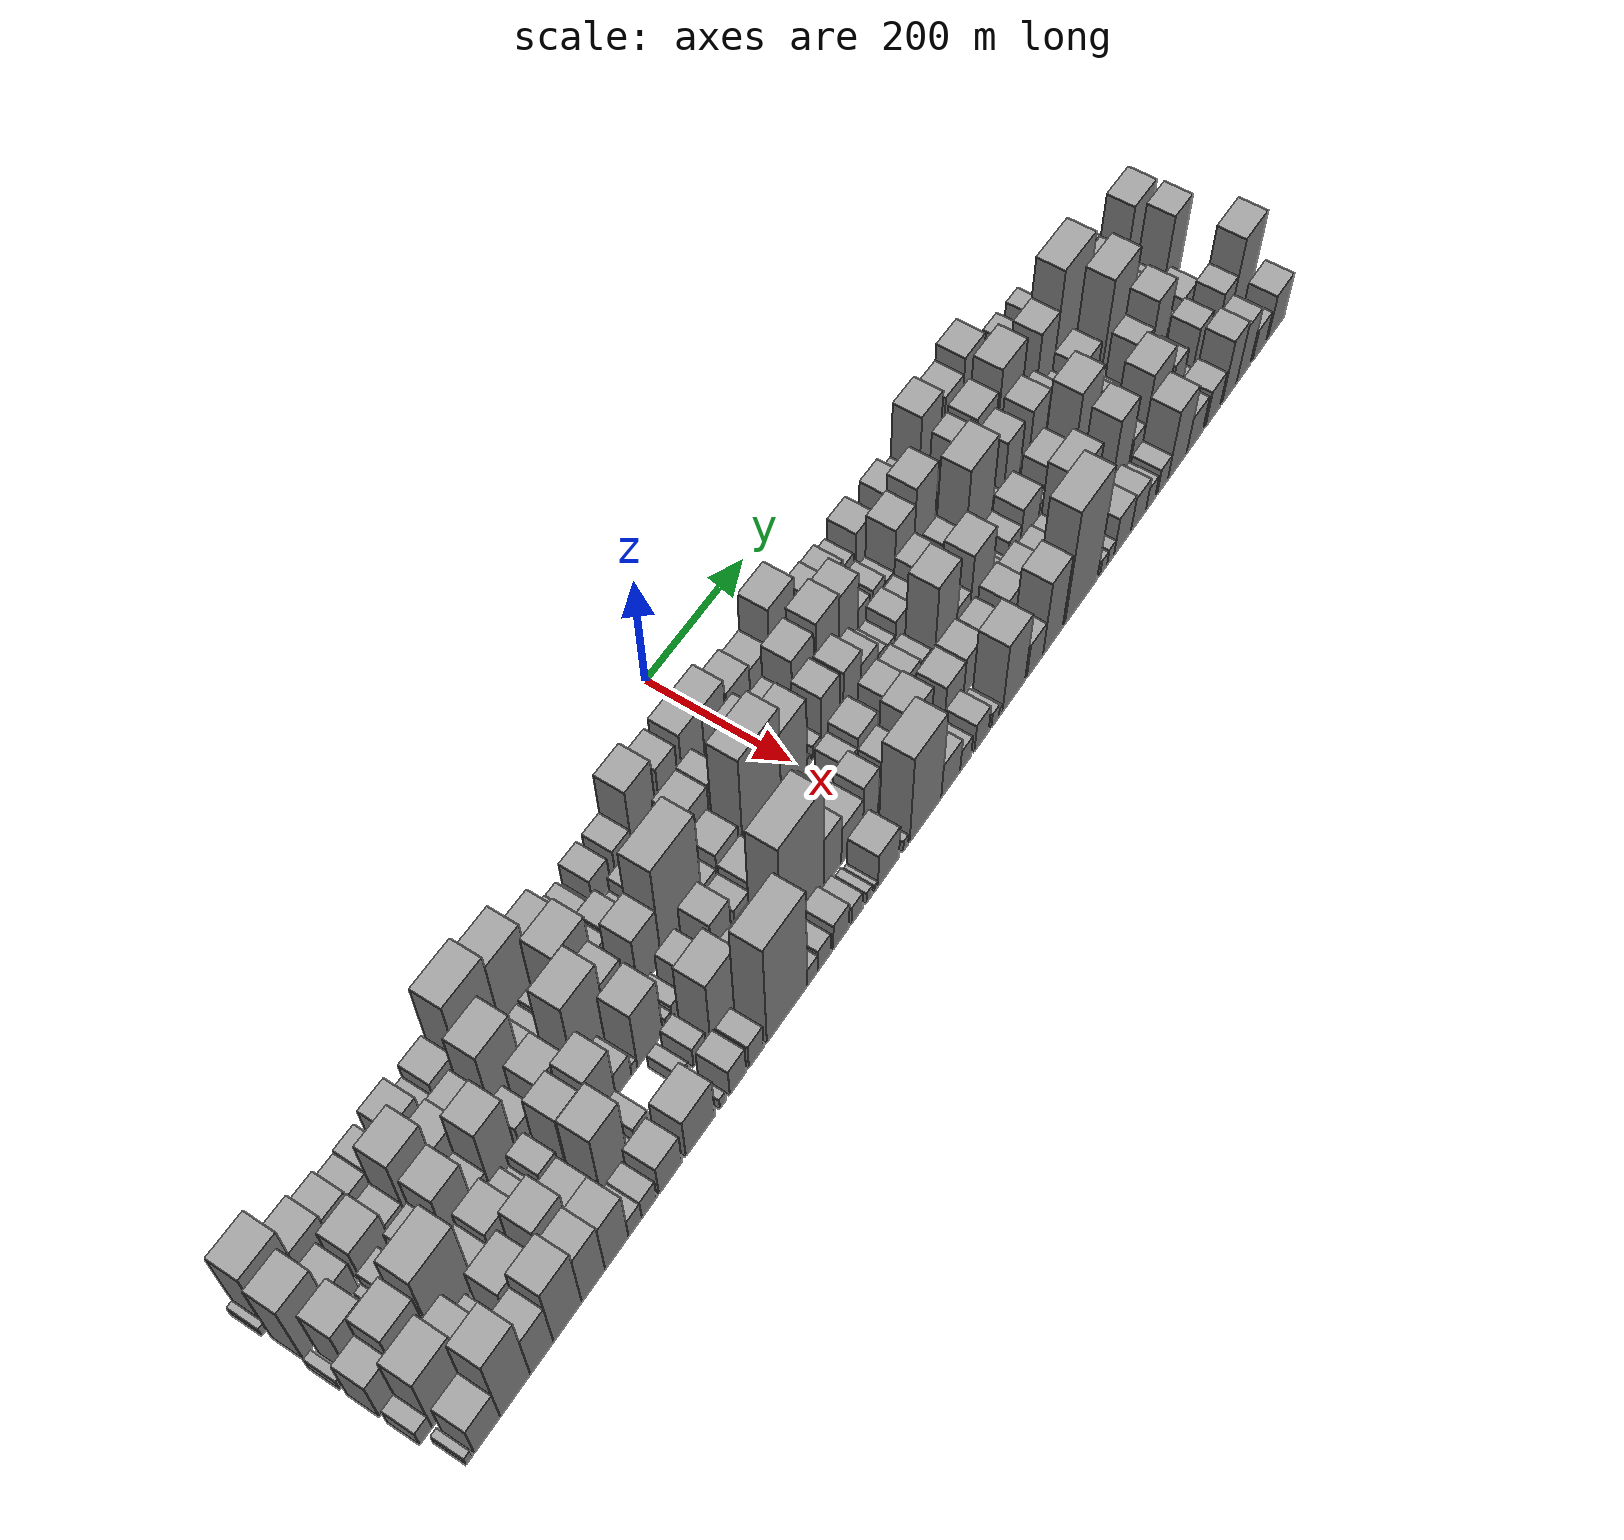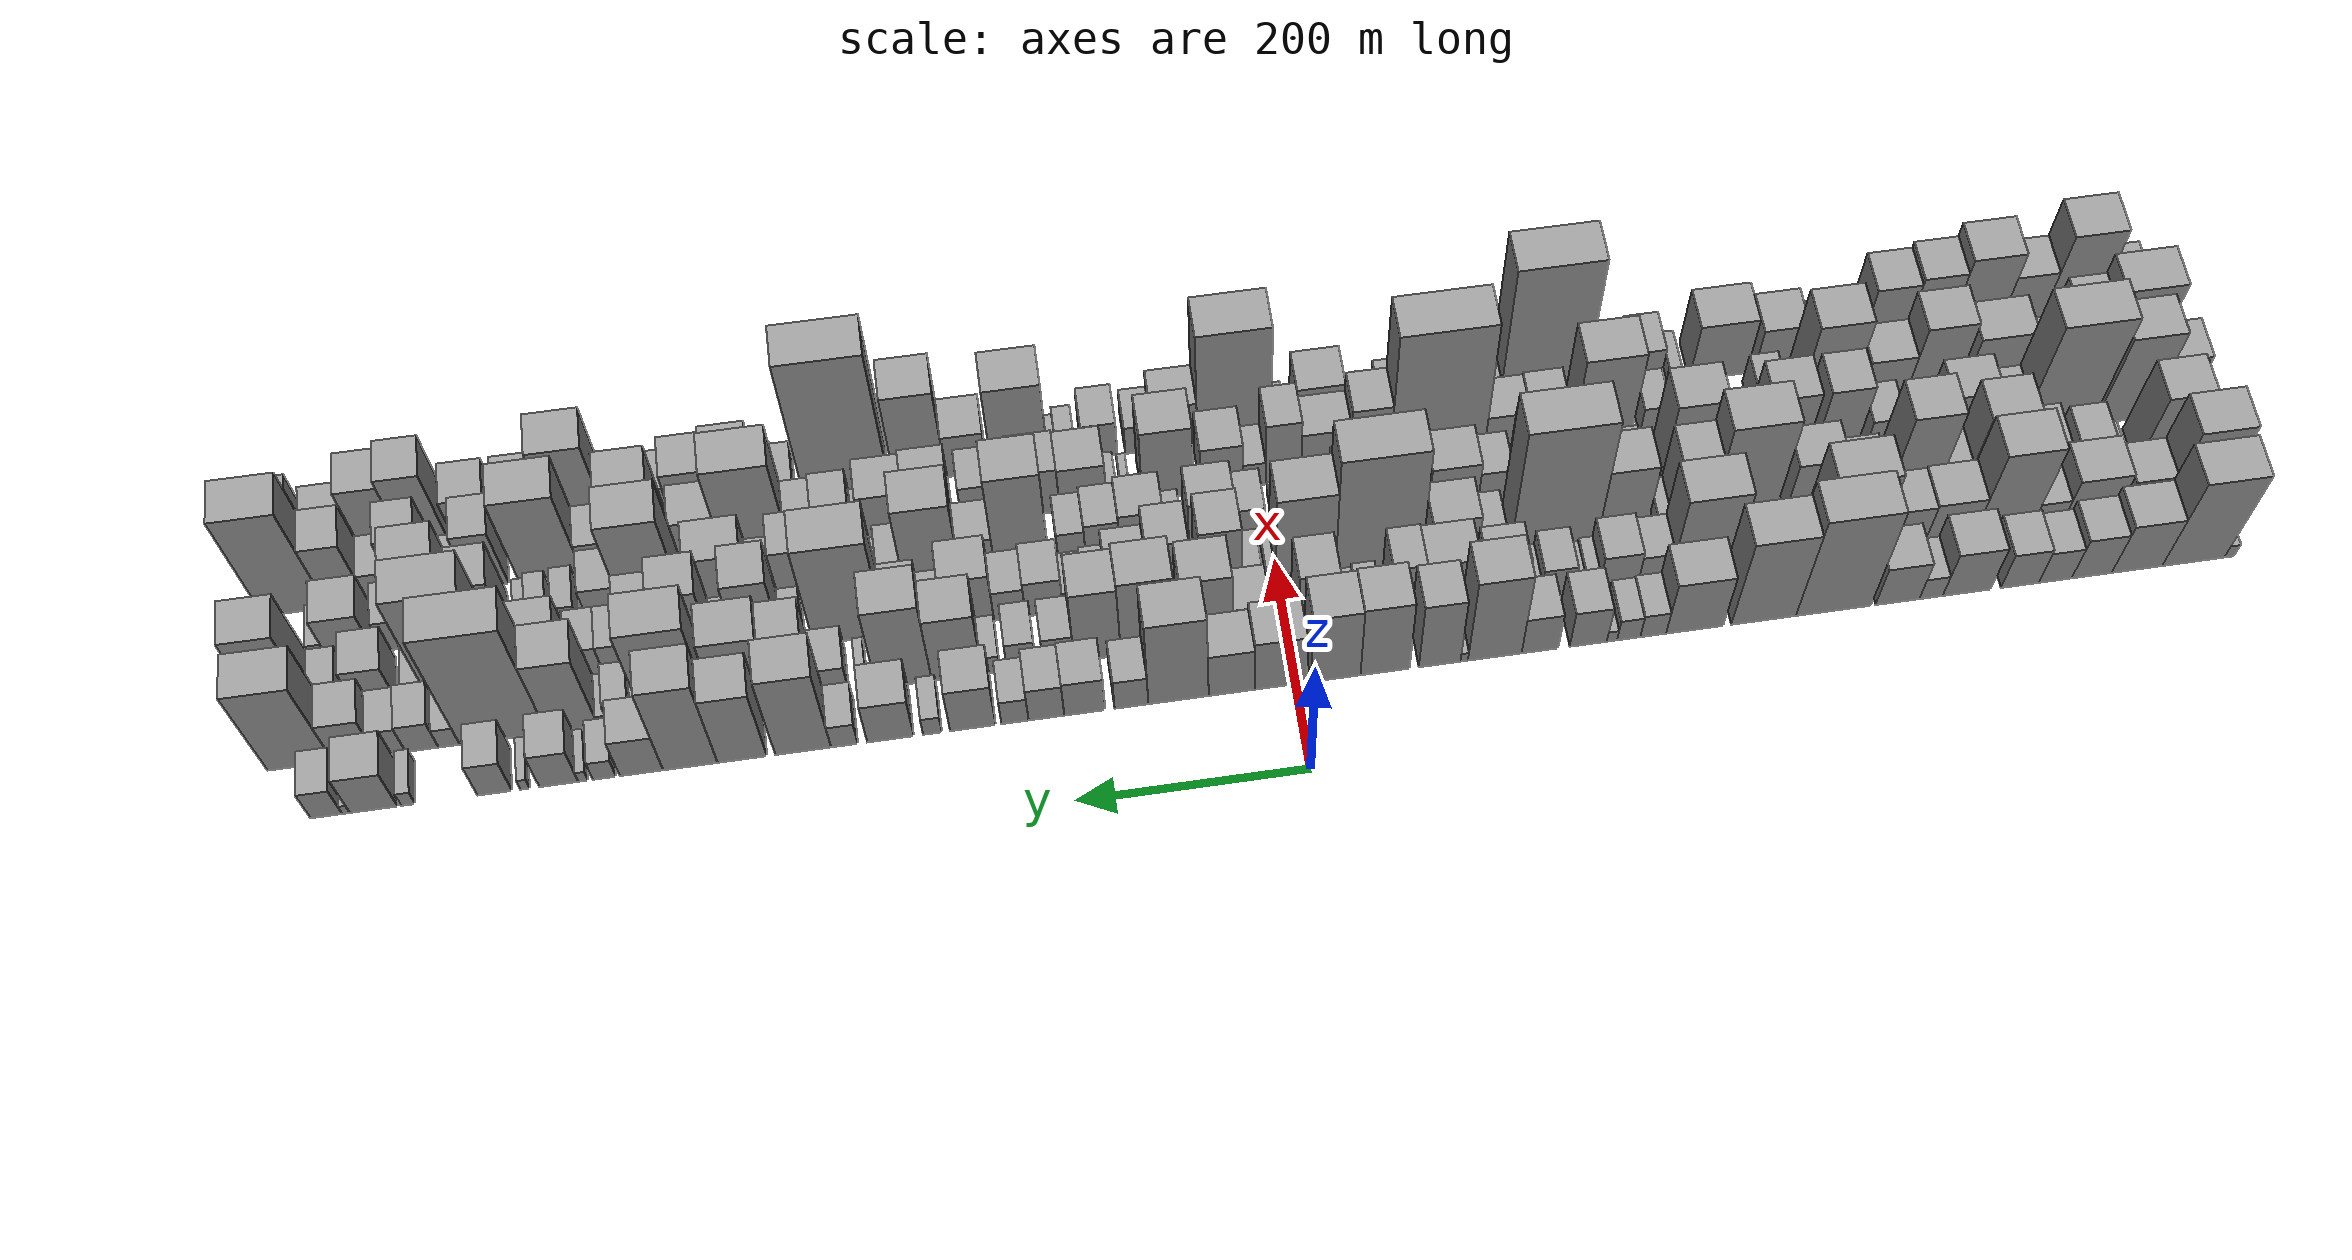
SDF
<sdf version="1.6">
 <world name="default">
  <scene>
   <sky><clouds><speed>12</speed></clouds></sky>
   <ambient>0.4 0.4 0.4 1</ambient>
   <background>0.7 0.7 0.7 1</background>
   <shadows>1</shadows>
  </scene>
  <gravity>0 0 -9.8066</gravity>
  <magnetic_field>6e-06 2.3e-05 -4.2e-05</magnetic_field>
  <physics default="0" name="default_physics" type="ode">
   <ode>
    <solver>
     <type>quick</type>
     <iters>10</iters>
     <sor>1.0</sor>
     <use_dynamic_moi_rescaling>0</use_dynamic_moi_rescaling>
    </solver>
    <constraints>
     <cfm>0</cfm>
     <erp>0.2</erp>
     <contact_max_correcting_vel>100</contact_max_correcting_vel>
     <contact_surface_layer>0.001</contact_surface_layer>
    </constraints>
   </ode>
   <max_step_size>0.004</max_step_size>
   <real_time_factor>1</real_time_factor>
   <real_time_update_rate>250</real_time_update_rate>
  </physics>
  <light name="sun" type="directional">
   <pose>0 0 10 0 0 0</pose>
   <diffuse>0.8 0.8 0.8 1</diffuse>
   <specular>0.2 0.2 0.2 1</specular>
   <attenuation>
    <range>1000</range>
    <constant>0.9</constant>
    <linear>0.01</linear>
    <quadratic>0.001</quadratic>
   </attenuation>
   <direction>-0.5 0.1 -0.9</direction>
  </light>
  <model name="building_1">
   <static>1</static>
   <pose>100.0000 -825.5281 0 0.000000 0.000000 0.000000</pose>
   <link name="link">
    <pose>0 0 10.50 0 0 0</pose>
    <collision name="collision"><geometry><box><size>40.0000 8.9437 21.0000</size></box></geometry></collision>
    <visual name="visual">
     <cast_shadows>0</cast_shadows>
     <geometry><box><size>40.0000 8.9437 21.0000</size></box></geometry>
     <material>
      <script>
       <uri>model://grey_wall/materials/scripts</uri>
       <uri>model://grey_wall/materials/textures</uri>
       <name>vrc/grey_wall</name>
      </script>
     </material>
    </visual>
   </link>
  </model>
  <model name="building_2">
   <static>1</static>
   <pose>100.0000 -792.9867 0 0.000000 0.000000 0.000000</pose>
   <link name="link">
    <pose>0 0 73.50 0 0 0</pose>
    <collision name="collision"><geometry><box><size>40.0000 56.1392 147.0000</size></box></geometry></collision>
    <visual name="visual">
     <cast_shadows>0</cast_shadows>
     <geometry><box><size>40.0000 56.1392 147.0000</size></box></geometry>
     <material>
      <script>
       <uri>model://grey_wall/materials/scripts</uri>
       <uri>model://grey_wall/materials/textures</uri>
       <name>vrc/grey_wall</name>
      </script>
     </material>
    </visual>
   </link>
  </model>
  <model name="building_3">
   <static>1</static>
   <pose>100.0000 -742.1506 0 0.000000 0.000000 0.000000</pose>
   <link name="link">
    <pose>0 0 42.00 0 0 0</pose>
    <collision name="collision"><geometry><box><size>40.0000 45.5331 84.0000</size></box></geometry></collision>
    <visual name="visual">
     <cast_shadows>0</cast_shadows>
     <geometry><box><size>40.0000 45.5331 84.0000</size></box></geometry>
     <material>
      <script>
       <uri>model://grey_wall/materials/scripts</uri>
       <uri>model://grey_wall/materials/textures</uri>
       <name>vrc/grey_wall</name>
      </script>
     </material>
    </visual>
   </link>
  </model>
  <model name="building_4">
   <static>1</static>
   <pose>100.0000 -701.3906 0 0.000000 0.000000 0.000000</pose>
   <link name="link">
    <pose>0 0 34.50 0 0 0</pose>
    <collision name="collision"><geometry><box><size>40.0000 35.9868 69.0000</size></box></geometry></collision>
    <visual name="visual">
     <cast_shadows>0</cast_shadows>
     <geometry><box><size>40.0000 35.9868 69.0000</size></box></geometry>
     <material>
      <script>
       <uri>model://grey_wall/materials/scripts</uri>
       <uri>model://grey_wall/materials/textures</uri>
       <name>vrc/grey_wall</name>
      </script>
     </material>
    </visual>
   </link>
  </model>
  <model name="building_5">
   <static>1</static>
   <pose>100.0000 -668.6138 0 0.000000 0.000000 0.000000</pose>
   <link name="link">
    <pose>0 0 27.00 0 0 0</pose>
    <collision name="collision"><geometry><box><size>40.0000 29.5669 54.0000</size></box></geometry></collision>
    <visual name="visual">
     <cast_shadows>0</cast_shadows>
     <geometry><box><size>40.0000 29.5669 54.0000</size></box></geometry>
     <material>
      <script>
       <uri>model://grey_wall/materials/scripts</uri>
       <uri>model://grey_wall/materials/textures</uri>
       <name>vrc/grey_wall</name>
      </script>
     </material>
    </visual>
   </link>
  </model>
  <model name="building_6">
   <static>1</static>
   <pose>100.0000 -636.8411 0 0.000000 0.000000 0.000000</pose>
   <link name="link">
    <pose>0 0 30.00 0 0 0</pose>
    <collision name="collision"><geometry><box><size>40.0000 33.9786 60.0000</size></box></geometry></collision>
    <visual name="visual">
     <cast_shadows>0</cast_shadows>
     <geometry><box><size>40.0000 33.9786 60.0000</size></box></geometry>
     <material>
      <script>
       <uri>model://grey_wall/materials/scripts</uri>
       <uri>model://grey_wall/materials/textures</uri>
       <name>vrc/grey_wall</name>
      </script>
     </material>
    </visual>
   </link>
  </model>
  <model name="building_7">
   <static>1</static>
   <pose>100.0000 -589.4353 0 0.000000 0.000000 0.000000</pose>
   <link name="link">
    <pose>0 0 37.50 0 0 0</pose>
    <collision name="collision"><geometry><box><size>40.0000 42.8330 75.0000</size></box></geometry></collision>
    <visual name="visual">
     <cast_shadows>0</cast_shadows>
     <geometry><box><size>40.0000 42.8330 75.0000</size></box></geometry>
     <material>
      <script>
       <uri>model://grey_wall/materials/scripts</uri>
       <uri>model://grey_wall/materials/textures</uri>
       <name>vrc/grey_wall</name>
      </script>
     </material>
    </visual>
   </link>
  </model>
  <model name="building_8">
   <static>1</static>
   <pose>100.0000 -557.5764 0 0.000000 0.000000 0.000000</pose>
   <link name="link">
    <pose>0 0 18.00 0 0 0</pose>
    <collision name="collision"><geometry><box><size>40.0000 20.8849 36.0000</size></box></geometry></collision>
    <visual name="visual">
     <cast_shadows>0</cast_shadows>
     <geometry><box><size>40.0000 20.8849 36.0000</size></box></geometry>
     <material>
      <script>
       <uri>model://grey_wall/materials/scripts</uri>
       <uri>model://grey_wall/materials/textures</uri>
       <name>vrc/grey_wall</name>
      </script>
     </material>
    </visual>
   </link>
  </model>
  <model name="building_9">
   <static>1</static>
   <pose>100.0000 -527.5872 0 0.000000 0.000000 0.000000</pose>
   <link name="link">
    <pose>0 0 33.00 0 0 0</pose>
    <collision name="collision"><geometry><box><size>40.0000 39.0934 66.0000</size></box></geometry></collision>
    <visual name="visual">
     <cast_shadows>0</cast_shadows>
     <geometry><box><size>40.0000 39.0934 66.0000</size></box></geometry>
     <material>
      <script>
       <uri>model://grey_wall/materials/scripts</uri>
       <uri>model://grey_wall/materials/textures</uri>
       <name>vrc/grey_wall</name>
      </script>
     </material>
    </visual>
   </link>
  </model>
  <model name="building_10">
   <static>1</static>
   <pose>100.0000 -470.7364 0 0.000000 0.000000 0.000000</pose>
   <link name="link">
    <pose>0 0 85.50 0 0 0</pose>
    <collision name="collision"><geometry><box><size>40.0000 66.6082 171.0000</size></box></geometry></collision>
    <visual name="visual">
     <cast_shadows>0</cast_shadows>
     <geometry><box><size>40.0000 66.6082 171.0000</size></box></geometry>
     <material>
      <script>
       <uri>model://grey_wall/materials/scripts</uri>
       <uri>model://grey_wall/materials/textures</uri>
       <name>vrc/grey_wall</name>
      </script>
     </material>
    </visual>
   </link>
  </model>
  <model name="building_11">
   <static>1</static>
   <pose>100.0000 -408.8160 0 0.000000 0.000000 0.000000</pose>
   <link name="link">
    <pose>0 0 73.50 0 0 0</pose>
    <collision name="collision"><geometry><box><size>40.0000 57.2327 147.0000</size></box></geometry></collision>
    <visual name="visual">
     <cast_shadows>0</cast_shadows>
     <geometry><box><size>40.0000 57.2327 147.0000</size></box></geometry>
     <material>
      <script>
       <uri>model://grey_wall/materials/scripts</uri>
       <uri>model://grey_wall/materials/textures</uri>
       <name>vrc/grey_wall</name>
      </script>
     </material>
    </visual>
   </link>
  </model>
  <model name="building_12">
   <static>1</static>
   <pose>100.0000 -347.9721 0 0.000000 0.000000 0.000000</pose>
   <link name="link">
    <pose>0 0 45.00 0 0 0</pose>
    <collision name="collision"><geometry><box><size>40.0000 50.4550 90.0000</size></box></geometry></collision>
    <visual name="visual">
     <cast_shadows>0</cast_shadows>
     <geometry><box><size>40.0000 50.4550 90.0000</size></box></geometry>
     <material>
      <script>
       <uri>model://grey_wall/materials/scripts</uri>
       <uri>model://grey_wall/materials/textures</uri>
       <name>vrc/grey_wall</name>
      </script>
     </material>
    </visual>
   </link>
  </model>
  <model name="building_13">
   <static>1</static>
   <pose>100.0000 -311.3952 0 0.000000 0.000000 0.000000</pose>
   <link name="link">
    <pose>0 0 19.50 0 0 0</pose>
    <collision name="collision"><geometry><box><size>40.0000 22.6989 39.0000</size></box></geometry></collision>
    <visual name="visual">
     <cast_shadows>0</cast_shadows>
     <geometry><box><size>40.0000 22.6989 39.0000</size></box></geometry>
     <material>
      <script>
       <uri>model://grey_wall/materials/scripts</uri>
       <uri>model://grey_wall/materials/textures</uri>
       <name>vrc/grey_wall</name>
      </script>
     </material>
    </visual>
   </link>
  </model>
  <model name="building_14">
   <static>1</static>
   <pose>100.0000 -289.8084 0 0.000000 0.000000 0.000000</pose>
   <link name="link">
    <pose>0 0 18.00 0 0 0</pose>
    <collision name="collision"><geometry><box><size>40.0000 20.4746 36.0000</size></box></geometry></collision>
    <visual name="visual">
     <cast_shadows>0</cast_shadows>
     <geometry><box><size>40.0000 20.4746 36.0000</size></box></geometry>
     <material>
      <script>
       <uri>model://grey_wall/materials/scripts</uri>
       <uri>model://grey_wall/materials/textures</uri>
       <name>vrc/grey_wall</name>
      </script>
     </material>
    </visual>
   </link>
  </model>
  <model name="building_15">
   <static>1</static>
   <pose>100.0000 -275.0932 0 0.000000 0.000000 0.000000</pose>
   <link name="link">
    <pose>0 0 9.00 0 0 0</pose>
    <collision name="collision"><geometry><box><size>40.0000 8.9559 18.0000</size></box></geometry></collision>
    <visual name="visual">
     <cast_shadows>0</cast_shadows>
     <geometry><box><size>40.0000 8.9559 18.0000</size></box></geometry>
     <material>
      <script>
       <uri>model://grey_wall/materials/scripts</uri>
       <uri>model://grey_wall/materials/textures</uri>
       <name>vrc/grey_wall</name>
      </script>
     </material>
    </visual>
   </link>
  </model>
  <model name="building_16">
   <static>1</static>
   <pose>100.0000 -254.2984 0 0.000000 0.000000 0.000000</pose>
   <link name="link">
    <pose>0 0 31.50 0 0 0</pose>
    <collision name="collision"><geometry><box><size>40.0000 32.6336 63.0000</size></box></geometry></collision>
    <visual name="visual">
     <cast_shadows>0</cast_shadows>
     <geometry><box><size>40.0000 32.6336 63.0000</size></box></geometry>
     <material>
      <script>
       <uri>model://grey_wall/materials/scripts</uri>
       <uri>model://grey_wall/materials/textures</uri>
       <name>vrc/grey_wall</name>
      </script>
     </material>
    </visual>
   </link>
  </model>
  <model name="building_17">
   <static>1</static>
   <pose>100.0000 -211.9475 0 0.000000 0.000000 0.000000</pose>
   <link name="link">
    <pose>0 0 31.50 0 0 0</pose>
    <collision name="collision"><geometry><box><size>40.0000 32.0684 63.0000</size></box></geometry></collision>
    <visual name="visual">
     <cast_shadows>0</cast_shadows>
     <geometry><box><size>40.0000 32.0684 63.0000</size></box></geometry>
     <material>
      <script>
       <uri>model://grey_wall/materials/scripts</uri>
       <uri>model://grey_wall/materials/textures</uri>
       <name>vrc/grey_wall</name>
      </script>
     </material>
    </visual>
   </link>
  </model>
  <model name="building_18">
   <static>1</static>
   <pose>100.0000 -172.4650 0 0.000000 0.000000 0.000000</pose>
   <link name="link">
    <pose>0 0 72.00 0 0 0</pose>
    <collision name="collision"><geometry><box><size>40.0000 46.8966 144.0000</size></box></geometry></collision>
    <visual name="visual">
     <cast_shadows>0</cast_shadows>
     <geometry><box><size>40.0000 46.8966 144.0000</size></box></geometry>
     <material>
      <script>
       <uri>model://grey_wall/materials/scripts</uri>
       <uri>model://grey_wall/materials/textures</uri>
       <name>vrc/grey_wall</name>
      </script>
     </material>
    </visual>
   </link>
  </model>
  <model name="building_19">
   <static>1</static>
   <pose>100.0000 -145.7399 0 0.000000 0.000000 0.000000</pose>
   <link name="link">
    <pose>0 0 7.50 0 0 0</pose>
    <collision name="collision"><geometry><box><size>40.0000 6.5535 15.0000</size></box></geometry></collision>
    <visual name="visual">
     <cast_shadows>0</cast_shadows>
     <geometry><box><size>40.0000 6.5535 15.0000</size></box></geometry>
     <material>
      <script>
       <uri>model://grey_wall/materials/scripts</uri>
       <uri>model://grey_wall/materials/textures</uri>
       <name>vrc/grey_wall</name>
      </script>
     </material>
    </visual>
   </link>
  </model>
  <model name="building_20">
   <static>1</static>
   <pose>100.0000 -124.3125 0 0.000000 0.000000 0.000000</pose>
   <link name="link">
    <pose>0 0 57.00 0 0 0</pose>
    <collision name="collision"><geometry><box><size>40.0000 36.3013 114.0000</size></box></geometry></collision>
    <visual name="visual">
     <cast_shadows>0</cast_shadows>
     <geometry><box><size>40.0000 36.3013 114.0000</size></box></geometry>
     <material>
      <script>
       <uri>model://grey_wall/materials/scripts</uri>
       <uri>model://grey_wall/materials/textures</uri>
       <name>vrc/grey_wall</name>
      </script>
     </material>
    </visual>
   </link>
  </model>
  <model name="building_21">
   <static>1</static>
   <pose>100.0000 -76.8169 0 0.000000 0.000000 0.000000</pose>
   <link name="link">
    <pose>0 0 61.50 0 0 0</pose>
    <collision name="collision"><geometry><box><size>40.0000 42.6899 123.0000</size></box></geometry></collision>
    <visual name="visual">
     <cast_shadows>0</cast_shadows>
     <geometry><box><size>40.0000 42.6899 123.0000</size></box></geometry>
     <material>
      <script>
       <uri>model://grey_wall/materials/scripts</uri>
       <uri>model://grey_wall/materials/textures</uri>
       <name>vrc/grey_wall</name>
      </script>
     </material>
    </visual>
   </link>
  </model>
  <model name="building_22">
   <static>1</static>
   <pose>100.0000 -34.0870 0 0.000000 0.000000 0.000000</pose>
   <link name="link">
    <pose>0 0 60.00 0 0 0</pose>
    <collision name="collision"><geometry><box><size>40.0000 42.7698 120.0000</size></box></geometry></collision>
    <visual name="visual">
     <cast_shadows>0</cast_shadows>
     <geometry><box><size>40.0000 42.7698 120.0000</size></box></geometry>
     <material>
      <script>
       <uri>model://grey_wall/materials/scripts</uri>
       <uri>model://grey_wall/materials/textures</uri>
       <name>vrc/grey_wall</name>
      </script>
     </material>
    </visual>
   </link>
  </model>
  <model name="building_23">
   <static>1</static>
   <pose>100.0000 13.6109 0 0.000000 0.000000 0.000000</pose>
   <link name="link">
    <pose>0 0 43.50 0 0 0</pose>
    <collision name="collision"><geometry><box><size>40.0000 44.6261 87.0000</size></box></geometry></collision>
    <visual name="visual">
     <cast_shadows>0</cast_shadows>
     <geometry><box><size>40.0000 44.6261 87.0000</size></box></geometry>
     <material>
      <script>
       <uri>model://grey_wall/materials/scripts</uri>
       <uri>model://grey_wall/materials/textures</uri>
       <name>vrc/grey_wall</name>
      </script>
     </material>
    </visual>
   </link>
  </model>
  <model name="building_24">
   <static>1</static>
   <pose>100.0000 55.8594 0 0.000000 0.000000 0.000000</pose>
   <link name="link">
    <pose>0 0 37.50 0 0 0</pose>
    <collision name="collision"><geometry><box><size>40.0000 39.8710 75.0000</size></box></geometry></collision>
    <visual name="visual">
     <cast_shadows>0</cast_shadows>
     <geometry><box><size>40.0000 39.8710 75.0000</size></box></geometry>
     <material>
      <script>
       <uri>model://grey_wall/materials/scripts</uri>
       <uri>model://grey_wall/materials/textures</uri>
       <name>vrc/grey_wall</name>
      </script>
     </material>
    </visual>
   </link>
  </model>
  <model name="building_25">
   <static>1</static>
   <pose>100.0000 101.7549 0 0.000000 0.000000 0.000000</pose>
   <link name="link">
    <pose>0 0 73.50 0 0 0</pose>
    <collision name="collision"><geometry><box><size>40.0000 51.9200 147.0000</size></box></geometry></collision>
    <visual name="visual">
     <cast_shadows>0</cast_shadows>
     <geometry><box><size>40.0000 51.9200 147.0000</size></box></geometry>
     <material>
      <script>
       <uri>model://grey_wall/materials/scripts</uri>
       <uri>model://grey_wall/materials/textures</uri>
       <name>vrc/grey_wall</name>
      </script>
     </material>
    </visual>
   </link>
  </model>
  <model name="building_26">
   <static>1</static>
   <pose>100.0000 142.2153 0 0.000000 0.000000 0.000000</pose>
   <link name="link">
    <pose>0 0 25.50 0 0 0</pose>
    <collision name="collision"><geometry><box><size>40.0000 29.0008 51.0000</size></box></geometry></collision>
    <visual name="visual">
     <cast_shadows>0</cast_shadows>
     <geometry><box><size>40.0000 29.0008 51.0000</size></box></geometry>
     <material>
      <script>
       <uri>model://grey_wall/materials/scripts</uri>
       <uri>model://grey_wall/materials/textures</uri>
       <name>vrc/grey_wall</name>
      </script>
     </material>
    </visual>
   </link>
  </model>
  <model name="building_27">
   <static>1</static>
   <pose>100.0000 182.2322 0 0.000000 0.000000 0.000000</pose>
   <link name="link">
    <pose>0 0 30.00 0 0 0</pose>
    <collision name="collision"><geometry><box><size>40.0000 35.0331 60.0000</size></box></geometry></collision>
    <visual name="visual">
     <cast_shadows>0</cast_shadows>
     <geometry><box><size>40.0000 35.0331 60.0000</size></box></geometry>
     <material>
      <script>
       <uri>model://grey_wall/materials/scripts</uri>
       <uri>model://grey_wall/materials/textures</uri>
       <name>vrc/grey_wall</name>
      </script>
     </material>
    </visual>
   </link>
  </model>
  <model name="building_28">
   <static>1</static>
   <pose>100.0000 215.0473 0 0.000000 0.000000 0.000000</pose>
   <link name="link">
    <pose>0 0 28.50 0 0 0</pose>
    <collision name="collision"><geometry><box><size>40.0000 30.5970 57.0000</size></box></geometry></collision>
    <visual name="visual">
     <cast_shadows>0</cast_shadows>
     <geometry><box><size>40.0000 30.5970 57.0000</size></box></geometry>
     <material>
      <script>
       <uri>model://grey_wall/materials/scripts</uri>
       <uri>model://grey_wall/materials/textures</uri>
       <name>vrc/grey_wall</name>
      </script>
     </material>
    </visual>
   </link>
  </model>
  <model name="building_29">
   <static>1</static>
   <pose>100.0000 241.9303 0 0.000000 0.000000 0.000000</pose>
   <link name="link">
    <pose>0 0 21.00 0 0 0</pose>
    <collision name="collision"><geometry><box><size>40.0000 23.1691 42.0000</size></box></geometry></collision>
    <visual name="visual">
     <cast_shadows>0</cast_shadows>
     <geometry><box><size>40.0000 23.1691 42.0000</size></box></geometry>
     <material>
      <script>
       <uri>model://grey_wall/materials/scripts</uri>
       <uri>model://grey_wall/materials/textures</uri>
       <name>vrc/grey_wall</name>
      </script>
     </material>
    </visual>
   </link>
  </model>
  <model name="building_30">
   <static>1</static>
   <pose>100.0000 277.9306 0 0.000000 0.000000 0.000000</pose>
   <link name="link">
    <pose>0 0 37.50 0 0 0</pose>
    <collision name="collision"><geometry><box><size>40.0000 38.8315 75.0000</size></box></geometry></collision>
    <visual name="visual">
     <cast_shadows>0</cast_shadows>
     <geometry><box><size>40.0000 38.8315 75.0000</size></box></geometry>
     <material>
      <script>
       <uri>model://grey_wall/materials/scripts</uri>
       <uri>model://grey_wall/materials/textures</uri>
       <name>vrc/grey_wall</name>
      </script>
     </material>
    </visual>
   </link>
  </model>
  <model name="building_31">
   <static>1</static>
   <pose>100.0000 312.3126 0 0.000000 0.000000 0.000000</pose>
   <link name="link">
    <pose>0 0 15.00 0 0 0</pose>
    <collision name="collision"><geometry><box><size>40.0000 15.9323 30.0000</size></box></geometry></collision>
    <visual name="visual">
     <cast_shadows>0</cast_shadows>
     <geometry><box><size>40.0000 15.9323 30.0000</size></box></geometry>
     <material>
      <script>
       <uri>model://grey_wall/materials/scripts</uri>
       <uri>model://grey_wall/materials/textures</uri>
       <name>vrc/grey_wall</name>
      </script>
     </material>
    </visual>
   </link>
  </model>
  <model name="building_32">
   <static>1</static>
   <pose>100.0000 348.0190 0 0.000000 0.000000 0.000000</pose>
   <link name="link">
    <pose>0 0 34.50 0 0 0</pose>
    <collision name="collision"><geometry><box><size>40.0000 39.4806 69.0000</size></box></geometry></collision>
    <visual name="visual">
     <cast_shadows>0</cast_shadows>
     <geometry><box><size>40.0000 39.4806 69.0000</size></box></geometry>
     <material>
      <script>
       <uri>model://grey_wall/materials/scripts</uri>
       <uri>model://grey_wall/materials/textures</uri>
       <name>vrc/grey_wall</name>
      </script>
     </material>
    </visual>
   </link>
  </model>
  <model name="building_33">
   <static>1</static>
   <pose>100.0000 387.1134 0 0.000000 0.000000 0.000000</pose>
   <link name="link">
    <pose>0 0 19.50 0 0 0</pose>
    <collision name="collision"><geometry><box><size>40.0000 22.7083 39.0000</size></box></geometry></collision>
    <visual name="visual">
     <cast_shadows>0</cast_shadows>
     <geometry><box><size>40.0000 22.7083 39.0000</size></box></geometry>
     <material>
      <script>
       <uri>model://grey_wall/materials/scripts</uri>
       <uri>model://grey_wall/materials/textures</uri>
       <name>vrc/grey_wall</name>
      </script>
     </material>
    </visual>
   </link>
  </model>
  <model name="building_34">
   <static>1</static>
   <pose>100.0000 422.0582 0 0.000000 0.000000 0.000000</pose>
   <link name="link">
    <pose>0 0 70.50 0 0 0</pose>
    <collision name="collision"><geometry><box><size>40.0000 47.1813 141.0000</size></box></geometry></collision>
    <visual name="visual">
     <cast_shadows>0</cast_shadows>
     <geometry><box><size>40.0000 47.1813 141.0000</size></box></geometry>
     <material>
      <script>
       <uri>model://grey_wall/materials/scripts</uri>
       <uri>model://grey_wall/materials/textures</uri>
       <name>vrc/grey_wall</name>
      </script>
     </material>
    </visual>
   </link>
  </model>
  <model name="building_35">
   <static>1</static>
   <pose>100.0000 473.4539 0 0.000000 0.000000 0.000000</pose>
   <link name="link">
    <pose>0 0 60.00 0 0 0</pose>
    <collision name="collision"><geometry><box><size>40.0000 41.6100 120.0000</size></box></geometry></collision>
    <visual name="visual">
     <cast_shadows>0</cast_shadows>
     <geometry><box><size>40.0000 41.6100 120.0000</size></box></geometry>
     <material>
      <script>
       <uri>model://grey_wall/materials/scripts</uri>
       <uri>model://grey_wall/materials/textures</uri>
       <name>vrc/grey_wall</name>
      </script>
     </material>
    </visual>
   </link>
  </model>
  <model name="building_36">
   <static>1</static>
   <pose>100.0000 517.1920 0 0.000000 0.000000 0.000000</pose>
   <link name="link">
    <pose>0 0 75.00 0 0 0</pose>
    <collision name="collision"><geometry><box><size>40.0000 45.8663 150.0000</size></box></geometry></collision>
    <visual name="visual">
     <cast_shadows>0</cast_shadows>
     <geometry><box><size>40.0000 45.8663 150.0000</size></box></geometry>
     <material>
      <script>
       <uri>model://grey_wall/materials/scripts</uri>
       <uri>model://grey_wall/materials/textures</uri>
       <name>vrc/grey_wall</name>
      </script>
     </material>
    </visual>
   </link>
  </model>
  <model name="building_37">
   <static>1</static>
   <pose>100.0000 558.3332 0 0.000000 0.000000 0.000000</pose>
   <link name="link">
    <pose>0 0 33.00 0 0 0</pose>
    <collision name="collision"><geometry><box><size>40.0000 36.4160 66.0000</size></box></geometry></collision>
    <visual name="visual">
     <cast_shadows>0</cast_shadows>
     <geometry><box><size>40.0000 36.4160 66.0000</size></box></geometry>
     <material>
      <script>
       <uri>model://grey_wall/materials/scripts</uri>
       <uri>model://grey_wall/materials/textures</uri>
       <name>vrc/grey_wall</name>
      </script>
     </material>
    </visual>
   </link>
  </model>
  <model name="building_38">
   <static>1</static>
   <pose>100.0000 589.3370 0 0.000000 0.000000 0.000000</pose>
   <link name="link">
    <pose>0 0 16.50 0 0 0</pose>
    <collision name="collision"><geometry><box><size>40.0000 19.5915 33.0000</size></box></geometry></collision>
    <visual name="visual">
     <cast_shadows>0</cast_shadows>
     <geometry><box><size>40.0000 19.5915 33.0000</size></box></geometry>
     <material>
      <script>
       <uri>model://grey_wall/materials/scripts</uri>
       <uri>model://grey_wall/materials/textures</uri>
       <name>vrc/grey_wall</name>
      </script>
     </material>
    </visual>
   </link>
  </model>
  <model name="building_39">
   <static>1</static>
   <pose>100.0000 607.1895 0 0.000000 0.000000 0.000000</pose>
   <link name="link">
    <pose>0 0 9.00 0 0 0</pose>
    <collision name="collision"><geometry><box><size>40.0000 8.1136 18.0000</size></box></geometry></collision>
    <visual name="visual">
     <cast_shadows>0</cast_shadows>
     <geometry><box><size>40.0000 8.1136 18.0000</size></box></geometry>
     <material>
      <script>
       <uri>model://grey_wall/materials/scripts</uri>
       <uri>model://grey_wall/materials/textures</uri>
       <name>vrc/grey_wall</name>
      </script>
     </material>
    </visual>
   </link>
  </model>
  <model name="building_40">
   <static>1</static>
   <pose>100.0000 627.5852 0 0.000000 0.000000 0.000000</pose>
   <link name="link">
    <pose>0 0 30.00 0 0 0</pose>
    <collision name="collision"><geometry><box><size>40.0000 32.6779 60.0000</size></box></geometry></collision>
    <visual name="visual">
     <cast_shadows>0</cast_shadows>
     <geometry><box><size>40.0000 32.6779 60.0000</size></box></geometry>
     <material>
      <script>
       <uri>model://grey_wall/materials/scripts</uri>
       <uri>model://grey_wall/materials/textures</uri>
       <name>vrc/grey_wall</name>
      </script>
     </material>
    </visual>
   </link>
  </model>
  <model name="building_41">
   <static>1</static>
   <pose>100.0000 655.8321 0 0.000000 0.000000 0.000000</pose>
   <link name="link">
    <pose>0 0 9.00 0 0 0</pose>
    <collision name="collision"><geometry><box><size>40.0000 7.8159 18.0000</size></box></geometry></collision>
    <visual name="visual">
     <cast_shadows>0</cast_shadows>
     <geometry><box><size>40.0000 7.8159 18.0000</size></box></geometry>
     <material>
      <script>
       <uri>model://grey_wall/materials/scripts</uri>
       <uri>model://grey_wall/materials/textures</uri>
       <name>vrc/grey_wall</name>
      </script>
     </material>
    </visual>
   </link>
  </model>
  <model name="building_42">
   <static>1</static>
   <pose>100.0000 681.1262 0 0.000000 0.000000 0.000000</pose>
   <link name="link">
    <pose>0 0 28.50 0 0 0</pose>
    <collision name="collision"><geometry><box><size>40.0000 28.7722 57.0000</size></box></geometry></collision>
    <visual name="visual">
     <cast_shadows>0</cast_shadows>
     <geometry><box><size>40.0000 28.7722 57.0000</size></box></geometry>
     <material>
      <script>
       <uri>model://grey_wall/materials/scripts</uri>
       <uri>model://grey_wall/materials/textures</uri>
       <name>vrc/grey_wall</name>
      </script>
     </material>
    </visual>
   </link>
  </model>
  <model name="building_43">
   <static>1</static>
   <pose>100.0000 753.0866 0 0.000000 0.000000 0.000000</pose>
   <link name="link">
    <pose>0 0 12.00 0 0 0</pose>
    <collision name="collision"><geometry><box><size>40.0000 11.7162 24.0000</size></box></geometry></collision>
    <visual name="visual">
     <cast_shadows>0</cast_shadows>
     <geometry><box><size>40.0000 11.7162 24.0000</size></box></geometry>
     <material>
      <script>
       <uri>model://grey_wall/materials/scripts</uri>
       <uri>model://grey_wall/materials/textures</uri>
       <name>vrc/grey_wall</name>
      </script>
     </material>
    </visual>
   </link>
  </model>
  <model name="building_44">
   <static>1</static>
   <pose>100.0000 781.7232 0 0.000000 0.000000 0.000000</pose>
   <link name="link">
    <pose>0 0 33.00 0 0 0</pose>
    <collision name="collision"><geometry><box><size>40.0000 39.5569 66.0000</size></box></geometry></collision>
    <visual name="visual">
     <cast_shadows>0</cast_shadows>
     <geometry><box><size>40.0000 39.5569 66.0000</size></box></geometry>
     <material>
      <script>
       <uri>model://grey_wall/materials/scripts</uri>
       <uri>model://grey_wall/materials/textures</uri>
       <name>vrc/grey_wall</name>
      </script>
     </material>
    </visual>
   </link>
  </model>
  <model name="building_45">
   <static>1</static>
   <pose>100.0000 804.6538 0 0.000000 0.000000 0.000000</pose>
   <link name="link">
    <pose>0 0 7.50 0 0 0</pose>
    <collision name="collision"><geometry><box><size>40.0000 6.3044 15.0000</size></box></geometry></collision>
    <visual name="visual">
     <cast_shadows>0</cast_shadows>
     <geometry><box><size>40.0000 6.3044 15.0000</size></box></geometry>
     <material>
      <script>
       <uri>model://grey_wall/materials/scripts</uri>
       <uri>model://grey_wall/materials/textures</uri>
       <name>vrc/grey_wall</name>
      </script>
     </material>
    </visual>
   </link>
  </model>
  <model name="building_46">
   <static>1</static>
   <pose>100.0000 820.9701 0 0.000000 0.000000 0.000000</pose>
   <link name="link">
    <pose>0 0 24.00 0 0 0</pose>
    <collision name="collision"><geometry><box><size>40.0000 26.3282 48.0000</size></box></geometry></collision>
    <visual name="visual">
     <cast_shadows>0</cast_shadows>
     <geometry><box><size>40.0000 26.3282 48.0000</size></box></geometry>
     <material>
      <script>
       <uri>model://grey_wall/materials/scripts</uri>
       <uri>model://grey_wall/materials/textures</uri>
       <name>vrc/grey_wall</name>
      </script>
     </material>
    </visual>
   </link>
  </model>
  <model name="building_47">
   <static>1</static>
   <pose>149.0000 -801.1284 0 0.000000 0.000000 0.000000</pose>
   <link name="link">
    <pose>0 0 72.00 0 0 0</pose>
    <collision name="collision"><geometry><box><size>40.0000 49.7432 144.0000</size></box></geometry></collision>
    <visual name="visual">
     <cast_shadows>0</cast_shadows>
     <geometry><box><size>40.0000 49.7432 144.0000</size></box></geometry>
     <material>
      <script>
       <uri>model://grey_wall/materials/scripts</uri>
       <uri>model://grey_wall/materials/textures</uri>
       <name>vrc/grey_wall</name>
      </script>
     </material>
    </visual>
   </link>
  </model>
  <model name="building_48">
   <static>1</static>
   <pose>149.0000 -757.5594 0 0.000000 0.000000 0.000000</pose>
   <link name="link">
    <pose>0 0 34.50 0 0 0</pose>
    <collision name="collision"><geometry><box><size>40.0000 37.3949 69.0000</size></box></geometry></collision>
    <visual name="visual">
     <cast_shadows>0</cast_shadows>
     <geometry><box><size>40.0000 37.3949 69.0000</size></box></geometry>
     <material>
      <script>
       <uri>model://grey_wall/materials/scripts</uri>
       <uri>model://grey_wall/materials/textures</uri>
       <name>vrc/grey_wall</name>
      </script>
     </material>
    </visual>
   </link>
  </model>
  <model name="building_49">
   <static>1</static>
   <pose>149.0000 -710.0263 0 0.000000 0.000000 0.000000</pose>
   <link name="link">
    <pose>0 0 42.00 0 0 0</pose>
    <collision name="collision"><geometry><box><size>40.0000 47.6712 84.0000</size></box></geometry></collision>
    <visual name="visual">
     <cast_shadows>0</cast_shadows>
     <geometry><box><size>40.0000 47.6712 84.0000</size></box></geometry>
     <material>
      <script>
       <uri>model://grey_wall/materials/scripts</uri>
       <uri>model://grey_wall/materials/textures</uri>
       <name>vrc/grey_wall</name>
      </script>
     </material>
    </visual>
   </link>
  </model>
  <model name="building_50">
   <static>1</static>
   <pose>149.0000 -672.4441 0 0.000000 0.000000 0.000000</pose>
   <link name="link">
    <pose>0 0 25.50 0 0 0</pose>
    <collision name="collision"><geometry><box><size>40.0000 27.4933 51.0000</size></box></geometry></collision>
    <visual name="visual">
     <cast_shadows>0</cast_shadows>
     <geometry><box><size>40.0000 27.4933 51.0000</size></box></geometry>
     <material>
      <script>
       <uri>model://grey_wall/materials/scripts</uri>
       <uri>model://grey_wall/materials/textures</uri>
       <name>vrc/grey_wall</name>
      </script>
     </material>
    </visual>
   </link>
  </model>
  <model name="building_51">
   <static>1</static>
   <pose>149.0000 -632.8638 0 0.000000 0.000000 0.000000</pose>
   <link name="link">
    <pose>0 0 75.00 0 0 0</pose>
    <collision name="collision"><geometry><box><size>40.0000 51.6673 150.0000</size></box></geometry></collision>
    <visual name="visual">
     <cast_shadows>0</cast_shadows>
     <geometry><box><size>40.0000 51.6673 150.0000</size></box></geometry>
     <material>
      <script>
       <uri>model://grey_wall/materials/scripts</uri>
       <uri>model://grey_wall/materials/textures</uri>
       <name>vrc/grey_wall</name>
      </script>
     </material>
    </visual>
   </link>
  </model>
  <model name="building_52">
   <static>1</static>
   <pose>149.0000 -584.9630 0 0.000000 0.000000 0.000000</pose>
   <link name="link">
    <pose>0 0 37.50 0 0 0</pose>
    <collision name="collision"><geometry><box><size>40.0000 44.1342 75.0000</size></box></geometry></collision>
    <visual name="visual">
     <cast_shadows>0</cast_shadows>
     <geometry><box><size>40.0000 44.1342 75.0000</size></box></geometry>
     <material>
      <script>
       <uri>model://grey_wall/materials/scripts</uri>
       <uri>model://grey_wall/materials/textures</uri>
       <name>vrc/grey_wall</name>
      </script>
     </material>
    </visual>
   </link>
  </model>
  <model name="building_53">
   <static>1</static>
   <pose>149.0000 -543.5457 0 0.000000 0.000000 0.000000</pose>
   <link name="link">
    <pose>0 0 36.00 0 0 0</pose>
    <collision name="collision"><geometry><box><size>40.0000 38.7005 72.0000</size></box></geometry></collision>
    <visual name="visual">
     <cast_shadows>0</cast_shadows>
     <geometry><box><size>40.0000 38.7005 72.0000</size></box></geometry>
     <material>
      <script>
       <uri>model://grey_wall/materials/scripts</uri>
       <uri>model://grey_wall/materials/textures</uri>
       <name>vrc/grey_wall</name>
      </script>
     </material>
    </visual>
   </link>
  </model>
  <model name="building_54">
   <static>1</static>
   <pose>149.0000 -492.4049 0 0.000000 0.000000 0.000000</pose>
   <link name="link">
    <pose>0 0 70.50 0 0 0</pose>
    <collision name="collision"><geometry><box><size>40.0000 55.5810 141.0000</size></box></geometry></collision>
    <visual name="visual">
     <cast_shadows>0</cast_shadows>
     <geometry><box><size>40.0000 55.5810 141.0000</size></box></geometry>
     <material>
      <script>
       <uri>model://grey_wall/materials/scripts</uri>
       <uri>model://grey_wall/materials/textures</uri>
       <name>vrc/grey_wall</name>
      </script>
     </material>
    </visual>
   </link>
  </model>
  <model name="building_55">
   <static>1</static>
   <pose>149.0000 -451.6759 0 0.000000 0.000000 0.000000</pose>
   <link name="link">
    <pose>0 0 24.00 0 0 0</pose>
    <collision name="collision"><geometry><box><size>40.0000 25.8770 48.0000</size></box></geometry></collision>
    <visual name="visual">
     <cast_shadows>0</cast_shadows>
     <geometry><box><size>40.0000 25.8770 48.0000</size></box></geometry>
     <material>
      <script>
       <uri>model://grey_wall/materials/scripts</uri>
       <uri>model://grey_wall/materials/textures</uri>
       <name>vrc/grey_wall</name>
      </script>
     </material>
    </visual>
   </link>
  </model>
  <model name="building_56">
   <static>1</static>
   <pose>149.0000 -425.4327 0 0.000000 0.000000 0.000000</pose>
   <link name="link">
    <pose>0 0 16.50 0 0 0</pose>
    <collision name="collision"><geometry><box><size>40.0000 18.6094 33.0000</size></box></geometry></collision>
    <visual name="visual">
     <cast_shadows>0</cast_shadows>
     <geometry><box><size>40.0000 18.6094 33.0000</size></box></geometry>
     <material>
      <script>
       <uri>model://grey_wall/materials/scripts</uri>
       <uri>model://grey_wall/materials/textures</uri>
       <name>vrc/grey_wall</name>
      </script>
     </material>
    </visual>
   </link>
  </model>
  <model name="building_57">
   <static>1</static>
   <pose>149.0000 -402.5604 0 0.000000 0.000000 0.000000</pose>
   <link name="link">
    <pose>0 0 18.00 0 0 0</pose>
    <collision name="collision"><geometry><box><size>40.0000 21.1352 36.0000</size></box></geometry></collision>
    <visual name="visual">
     <cast_shadows>0</cast_shadows>
     <geometry><box><size>40.0000 21.1352 36.0000</size></box></geometry>
     <material>
      <script>
       <uri>model://grey_wall/materials/scripts</uri>
       <uri>model://grey_wall/materials/textures</uri>
       <name>vrc/grey_wall</name>
      </script>
     </material>
    </visual>
   </link>
  </model>
  <model name="building_58">
   <static>1</static>
   <pose>149.0000 -364.0391 0 0.000000 0.000000 0.000000</pose>
   <link name="link">
    <pose>0 0 72.00 0 0 0</pose>
    <collision name="collision"><geometry><box><size>40.0000 55.9074 144.0000</size></box></geometry></collision>
    <visual name="visual">
     <cast_shadows>0</cast_shadows>
     <geometry><box><size>40.0000 55.9074 144.0000</size></box></geometry>
     <material>
      <script>
       <uri>model://grey_wall/materials/scripts</uri>
       <uri>model://grey_wall/materials/textures</uri>
       <name>vrc/grey_wall</name>
      </script>
     </material>
    </visual>
   </link>
  </model>
  <model name="building_59">
   <static>1</static>
   <pose>149.0000 -321.9731 0 0.000000 0.000000 0.000000</pose>
   <link name="link">
    <pose>0 0 25.50 0 0 0</pose>
    <collision name="collision"><geometry><box><size>40.0000 28.2246 51.0000</size></box></geometry></collision>
    <visual name="visual">
     <cast_shadows>0</cast_shadows>
     <geometry><box><size>40.0000 28.2246 51.0000</size></box></geometry>
     <material>
      <script>
       <uri>model://grey_wall/materials/scripts</uri>
       <uri>model://grey_wall/materials/textures</uri>
       <name>vrc/grey_wall</name>
      </script>
     </material>
    </visual>
   </link>
  </model>
  <model name="building_60">
   <static>1</static>
   <pose>149.0000 -290.6808 0 0.000000 0.000000 0.000000</pose>
   <link name="link">
    <pose>0 0 30.00 0 0 0</pose>
    <collision name="collision"><geometry><box><size>40.0000 34.3600 60.0000</size></box></geometry></collision>
    <visual name="visual">
     <cast_shadows>0</cast_shadows>
     <geometry><box><size>40.0000 34.3600 60.0000</size></box></geometry>
     <material>
      <script>
       <uri>model://grey_wall/materials/scripts</uri>
       <uri>model://grey_wall/materials/textures</uri>
       <name>vrc/grey_wall</name>
      </script>
     </material>
    </visual>
   </link>
  </model>
  <model name="building_61">
   <static>1</static>
   <pose>149.0000 -267.4533 0 0.000000 0.000000 0.000000</pose>
   <link name="link">
    <pose>0 0 13.50 0 0 0</pose>
    <collision name="collision"><geometry><box><size>40.0000 12.0950 27.0000</size></box></geometry></collision>
    <visual name="visual">
     <cast_shadows>0</cast_shadows>
     <geometry><box><size>40.0000 12.0950 27.0000</size></box></geometry>
     <material>
      <script>
       <uri>model://grey_wall/materials/scripts</uri>
       <uri>model://grey_wall/materials/textures</uri>
       <name>vrc/grey_wall</name>
      </script>
     </material>
    </visual>
   </link>
  </model>
  <model name="building_62">
   <static>1</static>
   <pose>149.0000 -256.3342 0 0.000000 0.000000 0.000000</pose>
   <link name="link">
    <pose>0 0 10.50 0 0 0</pose>
    <collision name="collision"><geometry><box><size>40.0000 10.1433 21.0000</size></box></geometry></collision>
    <visual name="visual">
     <cast_shadows>0</cast_shadows>
     <geometry><box><size>40.0000 10.1433 21.0000</size></box></geometry>
     <material>
      <script>
       <uri>model://grey_wall/materials/scripts</uri>
       <uri>model://grey_wall/materials/textures</uri>
       <name>vrc/grey_wall</name>
      </script>
     </material>
    </visual>
   </link>
  </model>
  <model name="building_63">
   <static>1</static>
   <pose>149.0000 -236.6102 0 0.000000 0.000000 0.000000</pose>
   <link name="link">
    <pose>0 0 25.50 0 0 0</pose>
    <collision name="collision"><geometry><box><size>40.0000 29.3045 51.0000</size></box></geometry></collision>
    <visual name="visual">
     <cast_shadows>0</cast_shadows>
     <geometry><box><size>40.0000 29.3045 51.0000</size></box></geometry>
     <material>
      <script>
       <uri>model://grey_wall/materials/scripts</uri>
       <uri>model://grey_wall/materials/textures</uri>
       <name>vrc/grey_wall</name>
      </script>
     </material>
    </visual>
   </link>
  </model>
  <model name="building_64">
   <static>1</static>
   <pose>149.0000 -215.8485 0 0.000000 0.000000 0.000000</pose>
   <link name="link">
    <pose>0 0 13.50 0 0 0</pose>
    <collision name="collision"><geometry><box><size>40.0000 12.2190 27.0000</size></box></geometry></collision>
    <visual name="visual">
     <cast_shadows>0</cast_shadows>
     <geometry><box><size>40.0000 12.2190 27.0000</size></box></geometry>
     <material>
      <script>
       <uri>model://grey_wall/materials/scripts</uri>
       <uri>model://grey_wall/materials/textures</uri>
       <name>vrc/grey_wall</name>
      </script>
     </material>
    </visual>
   </link>
  </model>
  <model name="building_65">
   <static>1</static>
   <pose>149.0000 -190.5972 0 0.000000 0.000000 0.000000</pose>
   <link name="link">
    <pose>0 0 36.00 0 0 0</pose>
    <collision name="collision"><geometry><box><size>40.0000 38.2836 72.0000</size></box></geometry></collision>
    <visual name="visual">
     <cast_shadows>0</cast_shadows>
     <geometry><box><size>40.0000 38.2836 72.0000</size></box></geometry>
     <material>
      <script>
       <uri>model://grey_wall/materials/scripts</uri>
       <uri>model://grey_wall/materials/textures</uri>
       <name>vrc/grey_wall</name>
      </script>
     </material>
    </visual>
   </link>
  </model>
  <model name="building_66">
   <static>1</static>
   <pose>149.0000 -141.4421 0 0.000000 0.000000 0.000000</pose>
   <link name="link">
    <pose>0 0 45.00 0 0 0</pose>
    <collision name="collision"><geometry><box><size>40.0000 46.0265 90.0000</size></box></geometry></collision>
    <visual name="visual">
     <cast_shadows>0</cast_shadows>
     <geometry><box><size>40.0000 46.0265 90.0000</size></box></geometry>
     <material>
      <script>
       <uri>model://grey_wall/materials/scripts</uri>
       <uri>model://grey_wall/materials/textures</uri>
       <name>vrc/grey_wall</name>
      </script>
     </material>
    </visual>
   </link>
  </model>
  <model name="building_67">
   <static>1</static>
   <pose>149.0000 -103.8983 0 0.000000 0.000000 0.000000</pose>
   <link name="link">
    <pose>0 0 46.50 0 0 0</pose>
    <collision name="collision"><geometry><box><size>40.0000 29.0612 93.0000</size></box></geometry></collision>
    <visual name="visual">
     <cast_shadows>0</cast_shadows>
     <geometry><box><size>40.0000 29.0612 93.0000</size></box></geometry>
     <material>
      <script>
       <uri>model://grey_wall/materials/scripts</uri>
       <uri>model://grey_wall/materials/textures</uri>
       <name>vrc/grey_wall</name>
      </script>
     </material>
    </visual>
   </link>
  </model>
  <model name="building_68">
   <static>1</static>
   <pose>149.0000 -71.3239 0 0.000000 0.000000 0.000000</pose>
   <link name="link">
    <pose>0 0 18.00 0 0 0</pose>
    <collision name="collision"><geometry><box><size>40.0000 20.0875 36.0000</size></box></geometry></collision>
    <visual name="visual">
     <cast_shadows>0</cast_shadows>
     <geometry><box><size>40.0000 20.0875 36.0000</size></box></geometry>
     <material>
      <script>
       <uri>model://grey_wall/materials/scripts</uri>
       <uri>model://grey_wall/materials/textures</uri>
       <name>vrc/grey_wall</name>
      </script>
     </material>
    </visual>
   </link>
  </model>
  <model name="building_69">
   <static>1</static>
   <pose>149.0000 -52.8301 0 0.000000 0.000000 0.000000</pose>
   <link name="link">
    <pose>0 0 15.00 0 0 0</pose>
    <collision name="collision"><geometry><box><size>40.0000 16.9000 30.0000</size></box></geometry></collision>
    <visual name="visual">
     <cast_shadows>0</cast_shadows>
     <geometry><box><size>40.0000 16.9000 30.0000</size></box></geometry>
     <material>
      <script>
       <uri>model://grey_wall/materials/scripts</uri>
       <uri>model://grey_wall/materials/textures</uri>
       <name>vrc/grey_wall</name>
      </script>
     </material>
    </visual>
   </link>
  </model>
  <model name="building_70">
   <static>1</static>
   <pose>149.0000 -26.7910 0 0.000000 0.000000 0.000000</pose>
   <link name="link">
    <pose>0 0 49.50 0 0 0</pose>
    <collision name="collision"><geometry><box><size>40.0000 35.1782 99.0000</size></box></geometry></collision>
    <visual name="visual">
     <cast_shadows>0</cast_shadows>
     <geometry><box><size>40.0000 35.1782 99.0000</size></box></geometry>
     <material>
      <script>
       <uri>model://grey_wall/materials/scripts</uri>
       <uri>model://grey_wall/materials/textures</uri>
       <name>vrc/grey_wall</name>
      </script>
     </material>
    </visual>
   </link>
  </model>
  <model name="building_71">
   <static>1</static>
   <pose>149.0000 2.3673 0 0.000000 0.000000 0.000000</pose>
   <link name="link">
    <pose>0 0 16.50 0 0 0</pose>
    <collision name="collision"><geometry><box><size>40.0000 17.1384 33.0000</size></box></geometry></collision>
    <visual name="visual">
     <cast_shadows>0</cast_shadows>
     <geometry><box><size>40.0000 17.1384 33.0000</size></box></geometry>
     <material>
      <script>
       <uri>model://grey_wall/materials/scripts</uri>
       <uri>model://grey_wall/materials/textures</uri>
       <name>vrc/grey_wall</name>
      </script>
     </material>
    </visual>
   </link>
  </model>
  <model name="building_72">
   <static>1</static>
   <pose>149.0000 31.3032 0 0.000000 0.000000 0.000000</pose>
   <link name="link">
    <pose>0 0 28.50 0 0 0</pose>
    <collision name="collision"><geometry><box><size>40.0000 32.7333 57.0000</size></box></geometry></collision>
    <visual name="visual">
     <cast_shadows>0</cast_shadows>
     <geometry><box><size>40.0000 32.7333 57.0000</size></box></geometry>
     <material>
      <script>
       <uri>model://grey_wall/materials/scripts</uri>
       <uri>model://grey_wall/materials/textures</uri>
       <name>vrc/grey_wall</name>
      </script>
     </material>
    </visual>
   </link>
  </model>
  <model name="building_73">
   <static>1</static>
   <pose>149.0000 69.9368 0 0.000000 0.000000 0.000000</pose>
   <link name="link">
    <pose>0 0 60.00 0 0 0</pose>
    <collision name="collision"><geometry><box><size>40.0000 44.5337 120.0000</size></box></geometry></collision>
    <visual name="visual">
     <cast_shadows>0</cast_shadows>
     <geometry><box><size>40.0000 44.5337 120.0000</size></box></geometry>
     <material>
      <script>
       <uri>model://grey_wall/materials/scripts</uri>
       <uri>model://grey_wall/materials/textures</uri>
       <name>vrc/grey_wall</name>
      </script>
     </material>
    </visual>
   </link>
  </model>
  <model name="building_74">
   <static>1</static>
   <pose>149.0000 120.9621 0 0.000000 0.000000 0.000000</pose>
   <link name="link">
    <pose>0 0 66.00 0 0 0</pose>
    <collision name="collision"><geometry><box><size>40.0000 47.5169 132.0000</size></box></geometry></collision>
    <visual name="visual">
     <cast_shadows>0</cast_shadows>
     <geometry><box><size>40.0000 47.5169 132.0000</size></box></geometry>
     <material>
      <script>
       <uri>model://grey_wall/materials/scripts</uri>
       <uri>model://grey_wall/materials/textures</uri>
       <name>vrc/grey_wall</name>
      </script>
     </material>
    </visual>
   </link>
  </model>
  <model name="building_75">
   <static>1</static>
   <pose>149.0000 164.9609 0 0.000000 0.000000 0.000000</pose>
   <link name="link">
    <pose>0 0 61.50 0 0 0</pose>
    <collision name="collision"><geometry><box><size>40.0000 40.4808 123.0000</size></box></geometry></collision>
    <visual name="visual">
     <cast_shadows>0</cast_shadows>
     <geometry><box><size>40.0000 40.4808 123.0000</size></box></geometry>
     <material>
      <script>
       <uri>model://grey_wall/materials/scripts</uri>
       <uri>model://grey_wall/materials/textures</uri>
       <name>vrc/grey_wall</name>
      </script>
     </material>
    </visual>
   </link>
  </model>
  <model name="building_76">
   <static>1</static>
   <pose>149.0000 198.5655 0 0.000000 0.000000 0.000000</pose>
   <link name="link">
    <pose>0 0 24.00 0 0 0</pose>
    <collision name="collision"><geometry><box><size>40.0000 26.7283 48.0000</size></box></geometry></collision>
    <visual name="visual">
     <cast_shadows>0</cast_shadows>
     <geometry><box><size>40.0000 26.7283 48.0000</size></box></geometry>
     <material>
      <script>
       <uri>model://grey_wall/materials/scripts</uri>
       <uri>model://grey_wall/materials/textures</uri>
       <name>vrc/grey_wall</name>
      </script>
     </material>
    </visual>
   </link>
  </model>
  <model name="building_77">
   <static>1</static>
   <pose>149.0000 230.4856 0 0.000000 0.000000 0.000000</pose>
   <link name="link">
    <pose>0 0 24.00 0 0 0</pose>
    <collision name="collision"><geometry><box><size>40.0000 25.1119 48.0000</size></box></geometry></collision>
    <visual name="visual">
     <cast_shadows>0</cast_shadows>
     <geometry><box><size>40.0000 25.1119 48.0000</size></box></geometry>
     <material>
      <script>
       <uri>model://grey_wall/materials/scripts</uri>
       <uri>model://grey_wall/materials/textures</uri>
       <name>vrc/grey_wall</name>
      </script>
     </material>
    </visual>
   </link>
  </model>
  <model name="building_78">
   <static>1</static>
   <pose>149.0000 256.8370 0 0.000000 0.000000 0.000000</pose>
   <link name="link">
    <pose>0 0 15.00 0 0 0</pose>
    <collision name="collision"><geometry><box><size>40.0000 15.5911 30.0000</size></box></geometry></collision>
    <visual name="visual">
     <cast_shadows>0</cast_shadows>
     <geometry><box><size>40.0000 15.5911 30.0000</size></box></geometry>
     <material>
      <script>
       <uri>model://grey_wall/materials/scripts</uri>
       <uri>model://grey_wall/materials/textures</uri>
       <name>vrc/grey_wall</name>
      </script>
     </material>
    </visual>
   </link>
  </model>
  <model name="building_79">
   <static>1</static>
   <pose>149.0000 286.2394 0 0.000000 0.000000 0.000000</pose>
   <link name="link">
    <pose>0 0 55.50 0 0 0</pose>
    <collision name="collision"><geometry><box><size>40.0000 43.2137 111.0000</size></box></geometry></collision>
    <visual name="visual">
     <cast_shadows>0</cast_shadows>
     <geometry><box><size>40.0000 43.2137 111.0000</size></box></geometry>
     <material>
      <script>
       <uri>model://grey_wall/materials/scripts</uri>
       <uri>model://grey_wall/materials/textures</uri>
       <name>vrc/grey_wall</name>
      </script>
     </material>
    </visual>
   </link>
  </model>
  <model name="building_80">
   <static>1</static>
   <pose>149.0000 331.6374 0 0.000000 0.000000 0.000000</pose>
   <link name="link">
    <pose>0 0 70.50 0 0 0</pose>
    <collision name="collision"><geometry><box><size>40.0000 47.5822 141.0000</size></box></geometry></collision>
    <visual name="visual">
     <cast_shadows>0</cast_shadows>
     <geometry><box><size>40.0000 47.5822 141.0000</size></box></geometry>
     <material>
      <script>
       <uri>model://grey_wall/materials/scripts</uri>
       <uri>model://grey_wall/materials/textures</uri>
       <name>vrc/grey_wall</name>
      </script>
     </material>
    </visual>
   </link>
  </model>
  <model name="building_81">
   <static>1</static>
   <pose>149.0000 366.6778 0 0.000000 0.000000 0.000000</pose>
   <link name="link">
    <pose>0 0 10.50 0 0 0</pose>
    <collision name="collision"><geometry><box><size>40.0000 8.4986 21.0000</size></box></geometry></collision>
    <visual name="visual">
     <cast_shadows>0</cast_shadows>
     <geometry><box><size>40.0000 8.4986 21.0000</size></box></geometry>
     <material>
      <script>
       <uri>model://grey_wall/materials/scripts</uri>
       <uri>model://grey_wall/materials/textures</uri>
       <name>vrc/grey_wall</name>
      </script>
     </material>
    </visual>
   </link>
  </model>
  <model name="building_82">
   <static>1</static>
   <pose>149.0000 393.0731 0 0.000000 0.000000 0.000000</pose>
   <link name="link">
    <pose>0 0 24.00 0 0 0</pose>
    <collision name="collision"><geometry><box><size>40.0000 28.2919 48.0000</size></box></geometry></collision>
    <visual name="visual">
     <cast_shadows>0</cast_shadows>
     <geometry><box><size>40.0000 28.2919 48.0000</size></box></geometry>
     <material>
      <script>
       <uri>model://grey_wall/materials/scripts</uri>
       <uri>model://grey_wall/materials/textures</uri>
       <name>vrc/grey_wall</name>
      </script>
     </material>
    </visual>
   </link>
  </model>
  <model name="building_83">
   <static>1</static>
   <pose>149.0000 425.1117 0 0.000000 0.000000 0.000000</pose>
   <link name="link">
    <pose>0 0 55.50 0 0 0</pose>
    <collision name="collision"><geometry><box><size>40.0000 35.7853 111.0000</size></box></geometry></collision>
    <visual name="visual">
     <cast_shadows>0</cast_shadows>
     <geometry><box><size>40.0000 35.7853 111.0000</size></box></geometry>
     <material>
      <script>
       <uri>model://grey_wall/materials/scripts</uri>
       <uri>model://grey_wall/materials/textures</uri>
       <name>vrc/grey_wall</name>
      </script>
     </material>
    </visual>
   </link>
  </model>
  <model name="building_84">
   <static>1</static>
   <pose>149.0000 467.2995 0 0.000000 0.000000 0.000000</pose>
   <link name="link">
    <pose>0 0 61.50 0 0 0</pose>
    <collision name="collision"><geometry><box><size>40.0000 48.5904 123.0000</size></box></geometry></collision>
    <visual name="visual">
     <cast_shadows>0</cast_shadows>
     <geometry><box><size>40.0000 48.5904 123.0000</size></box></geometry>
     <material>
      <script>
       <uri>model://grey_wall/materials/scripts</uri>
       <uri>model://grey_wall/materials/textures</uri>
       <name>vrc/grey_wall</name>
      </script>
     </material>
    </visual>
   </link>
  </model>
  <model name="building_85">
   <static>1</static>
   <pose>149.0000 525.0045 0 0.000000 0.000000 0.000000</pose>
   <link name="link">
    <pose>0 0 79.50 0 0 0</pose>
    <collision name="collision"><geometry><box><size>40.0000 56.8196 159.0000</size></box></geometry></collision>
    <visual name="visual">
     <cast_shadows>0</cast_shadows>
     <geometry><box><size>40.0000 56.8196 159.0000</size></box></geometry>
     <material>
      <script>
       <uri>model://grey_wall/materials/scripts</uri>
       <uri>model://grey_wall/materials/textures</uri>
       <name>vrc/grey_wall</name>
      </script>
     </material>
    </visual>
   </link>
  </model>
  <model name="building_86">
   <static>1</static>
   <pose>149.0000 557.7616 0 0.000000 0.000000 0.000000</pose>
   <link name="link">
    <pose>0 0 10.50 0 0 0</pose>
    <collision name="collision"><geometry><box><size>40.0000 8.6946 21.0000</size></box></geometry></collision>
    <visual name="visual">
     <cast_shadows>0</cast_shadows>
     <geometry><box><size>40.0000 8.6946 21.0000</size></box></geometry>
     <material>
      <script>
       <uri>model://grey_wall/materials/scripts</uri>
       <uri>model://grey_wall/materials/textures</uri>
       <name>vrc/grey_wall</name>
      </script>
     </material>
    </visual>
   </link>
  </model>
  <model name="building_87">
   <static>1</static>
   <pose>149.0000 572.8496 0 0.000000 0.000000 0.000000</pose>
   <link name="link">
    <pose>0 0 18.00 0 0 0</pose>
    <collision name="collision"><geometry><box><size>40.0000 21.4815 36.0000</size></box></geometry></collision>
    <visual name="visual">
     <cast_shadows>0</cast_shadows>
     <geometry><box><size>40.0000 21.4815 36.0000</size></box></geometry>
     <material>
      <script>
       <uri>model://grey_wall/materials/scripts</uri>
       <uri>model://grey_wall/materials/textures</uri>
       <name>vrc/grey_wall</name>
      </script>
     </material>
    </visual>
   </link>
  </model>
  <model name="building_88">
   <static>1</static>
   <pose>149.0000 587.8732 0 0.000000 0.000000 0.000000</pose>
   <link name="link">
    <pose>0 0 9.00 0 0 0</pose>
    <collision name="collision"><geometry><box><size>40.0000 8.5657 18.0000</size></box></geometry></collision>
    <visual name="visual">
     <cast_shadows>0</cast_shadows>
     <geometry><box><size>40.0000 8.5657 18.0000</size></box></geometry>
     <material>
      <script>
       <uri>model://grey_wall/materials/scripts</uri>
       <uri>model://grey_wall/materials/textures</uri>
       <name>vrc/grey_wall</name>
      </script>
     </material>
    </visual>
   </link>
  </model>
  <model name="building_89">
   <static>1</static>
   <pose>149.0000 613.6674 0 0.000000 0.000000 0.000000</pose>
   <link name="link">
    <pose>0 0 63.00 0 0 0</pose>
    <collision name="collision"><geometry><box><size>40.0000 43.0227 126.0000</size></box></geometry></collision>
    <visual name="visual">
     <cast_shadows>0</cast_shadows>
     <geometry><box><size>40.0000 43.0227 126.0000</size></box></geometry>
     <material>
      <script>
       <uri>model://grey_wall/materials/scripts</uri>
       <uri>model://grey_wall/materials/textures</uri>
       <name>vrc/grey_wall</name>
      </script>
     </material>
    </visual>
   </link>
  </model>
  <model name="building_90">
   <static>1</static>
   <pose>149.0000 671.9954 0 0.000000 0.000000 0.000000</pose>
   <link name="link">
    <pose>0 0 99.00 0 0 0</pose>
    <collision name="collision"><geometry><box><size>40.0000 73.6332 198.0000</size></box></geometry></collision>
    <visual name="visual">
     <cast_shadows>0</cast_shadows>
     <geometry><box><size>40.0000 73.6332 198.0000</size></box></geometry>
     <material>
      <script>
       <uri>model://grey_wall/materials/scripts</uri>
       <uri>model://grey_wall/materials/textures</uri>
       <name>vrc/grey_wall</name>
      </script>
     </material>
    </visual>
   </link>
  </model>
  <model name="building_91">
   <static>1</static>
   <pose>149.0000 717.7191 0 0.000000 0.000000 0.000000</pose>
   <link name="link">
    <pose>0 0 16.50 0 0 0</pose>
    <collision name="collision"><geometry><box><size>40.0000 17.8144 33.0000</size></box></geometry></collision>
    <visual name="visual">
     <cast_shadows>0</cast_shadows>
     <geometry><box><size>40.0000 17.8144 33.0000</size></box></geometry>
     <material>
      <script>
       <uri>model://grey_wall/materials/scripts</uri>
       <uri>model://grey_wall/materials/textures</uri>
       <name>vrc/grey_wall</name>
      </script>
     </material>
    </visual>
   </link>
  </model>
  <model name="building_92">
   <static>1</static>
   <pose>149.0000 740.4591 0 0.000000 0.000000 0.000000</pose>
   <link name="link">
    <pose>0 0 24.00 0 0 0</pose>
    <collision name="collision"><geometry><box><size>40.0000 27.6656 48.0000</size></box></geometry></collision>
    <visual name="visual">
     <cast_shadows>0</cast_shadows>
     <geometry><box><size>40.0000 27.6656 48.0000</size></box></geometry>
     <material>
      <script>
       <uri>model://grey_wall/materials/scripts</uri>
       <uri>model://grey_wall/materials/textures</uri>
       <name>vrc/grey_wall</name>
      </script>
     </material>
    </visual>
   </link>
  </model>
  <model name="building_93">
   <static>1</static>
   <pose>149.0000 766.5676 0 0.000000 0.000000 0.000000</pose>
   <link name="link">
    <pose>0 0 22.50 0 0 0</pose>
    <collision name="collision"><geometry><box><size>40.0000 24.5512 45.0000</size></box></geometry></collision>
    <visual name="visual">
     <cast_shadows>0</cast_shadows>
     <geometry><box><size>40.0000 24.5512 45.0000</size></box></geometry>
     <material>
      <script>
       <uri>model://grey_wall/materials/scripts</uri>
       <uri>model://grey_wall/materials/textures</uri>
       <name>vrc/grey_wall</name>
      </script>
     </material>
    </visual>
   </link>
  </model>
  <model name="building_94">
   <static>1</static>
   <pose>149.0000 796.7717 0 0.000000 0.000000 0.000000</pose>
   <link name="link">
    <pose>0 0 34.50 0 0 0</pose>
    <collision name="collision"><geometry><box><size>40.0000 35.8570 69.0000</size></box></geometry></collision>
    <visual name="visual">
     <cast_shadows>0</cast_shadows>
     <geometry><box><size>40.0000 35.8570 69.0000</size></box></geometry>
     <material>
      <script>
       <uri>model://grey_wall/materials/scripts</uri>
       <uri>model://grey_wall/materials/textures</uri>
       <name>vrc/grey_wall</name>
      </script>
     </material>
    </visual>
   </link>
  </model>
  <model name="building_95">
   <static>1</static>
   <pose>149.0000 842.2011 0 0.000000 0.000000 0.000000</pose>
   <link name="link">
    <pose>0 0 72.00 0 0 0</pose>
    <collision name="collision"><geometry><box><size>40.0000 55.0018 144.0000</size></box></geometry></collision>
    <visual name="visual">
     <cast_shadows>0</cast_shadows>
     <geometry><box><size>40.0000 55.0018 144.0000</size></box></geometry>
     <material>
      <script>
       <uri>model://grey_wall/materials/scripts</uri>
       <uri>model://grey_wall/materials/textures</uri>
       <name>vrc/grey_wall</name>
      </script>
     </material>
    </visual>
   </link>
  </model>
  <model name="building_96">
   <static>1</static>
   <pose>198.0000 -824.0716 0 0.000000 0.000000 0.000000</pose>
   <link name="link">
    <pose>0 0 13.50 0 0 0</pose>
    <collision name="collision"><geometry><box><size>40.0000 11.8567 27.0000</size></box></geometry></collision>
    <visual name="visual">
     <cast_shadows>0</cast_shadows>
     <geometry><box><size>40.0000 11.8567 27.0000</size></box></geometry>
     <material>
      <script>
       <uri>model://grey_wall/materials/scripts</uri>
       <uri>model://grey_wall/materials/textures</uri>
       <name>vrc/grey_wall</name>
      </script>
     </material>
    </visual>
   </link>
  </model>
  <model name="building_97">
   <static>1</static>
   <pose>198.0000 -791.1762 0 0.000000 0.000000 0.000000</pose>
   <link name="link">
    <pose>0 0 60.00 0 0 0</pose>
    <collision name="collision"><geometry><box><size>40.0000 43.9342 120.0000</size></box></geometry></collision>
    <visual name="visual">
     <cast_shadows>0</cast_shadows>
     <geometry><box><size>40.0000 43.9342 120.0000</size></box></geometry>
     <material>
      <script>
       <uri>model://grey_wall/materials/scripts</uri>
       <uri>model://grey_wall/materials/textures</uri>
       <name>vrc/grey_wall</name>
      </script>
     </material>
    </visual>
   </link>
  </model>
  <model name="building_98">
   <static>1</static>
   <pose>198.0000 -755.4946 0 0.000000 0.000000 0.000000</pose>
   <link name="link">
    <pose>0 0 9.00 0 0 0</pose>
    <collision name="collision"><geometry><box><size>40.0000 7.4290 18.0000</size></box></geometry></collision>
    <visual name="visual">
     <cast_shadows>0</cast_shadows>
     <geometry><box><size>40.0000 7.4290 18.0000</size></box></geometry>
     <material>
      <script>
       <uri>model://grey_wall/materials/scripts</uri>
       <uri>model://grey_wall/materials/textures</uri>
       <name>vrc/grey_wall</name>
      </script>
     </material>
    </visual>
   </link>
  </model>
  <model name="building_99">
   <static>1</static>
   <pose>198.0000 -745.9419 0 0.000000 0.000000 0.000000</pose>
   <link name="link">
    <pose>0 0 13.50 0 0 0</pose>
    <collision name="collision"><geometry><box><size>40.0000 11.6764 27.0000</size></box></geometry></collision>
    <visual name="visual">
     <cast_shadows>0</cast_shadows>
     <geometry><box><size>40.0000 11.6764 27.0000</size></box></geometry>
     <material>
      <script>
       <uri>model://grey_wall/materials/scripts</uri>
       <uri>model://grey_wall/materials/textures</uri>
       <name>vrc/grey_wall</name>
      </script>
     </material>
    </visual>
   </link>
  </model>
  <model name="building_100">
   <static>1</static>
   <pose>198.0000 -723.5810 0 0.000000 0.000000 0.000000</pose>
   <link name="link">
    <pose>0 0 28.50 0 0 0</pose>
    <collision name="collision"><geometry><box><size>40.0000 33.0454 57.0000</size></box></geometry></collision>
    <visual name="visual">
     <cast_shadows>0</cast_shadows>
     <geometry><box><size>40.0000 33.0454 57.0000</size></box></geometry>
     <material>
      <script>
       <uri>model://grey_wall/materials/scripts</uri>
       <uri>model://grey_wall/materials/textures</uri>
       <name>vrc/grey_wall</name>
      </script>
     </material>
    </visual>
   </link>
  </model>
  <model name="building_101">
   <static>1</static>
   <pose>198.0000 -701.5438 0 0.000000 0.000000 0.000000</pose>
   <link name="link">
    <pose>0 0 13.50 0 0 0</pose>
    <collision name="collision"><geometry><box><size>40.0000 11.0291 27.0000</size></box></geometry></collision>
    <visual name="visual">
     <cast_shadows>0</cast_shadows>
     <geometry><box><size>40.0000 11.0291 27.0000</size></box></geometry>
     <material>
      <script>
       <uri>model://grey_wall/materials/scripts</uri>
       <uri>model://grey_wall/materials/textures</uri>
       <name>vrc/grey_wall</name>
      </script>
     </material>
    </visual>
   </link>
  </model>
  <model name="building_102">
   <static>1</static>
   <pose>198.0000 -676.7778 0 0.000000 0.000000 0.000000</pose>
   <link name="link">
    <pose>0 0 33.00 0 0 0</pose>
    <collision name="collision"><geometry><box><size>40.0000 38.5028 66.0000</size></box></geometry></collision>
    <visual name="visual">
     <cast_shadows>0</cast_shadows>
     <geometry><box><size>40.0000 38.5028 66.0000</size></box></geometry>
     <material>
      <script>
       <uri>model://grey_wall/materials/scripts</uri>
       <uri>model://grey_wall/materials/textures</uri>
       <name>vrc/grey_wall</name>
      </script>
     </material>
    </visual>
   </link>
  </model>
  <model name="building_103">
   <static>1</static>
   <pose>198.0000 -634.9142 0 0.000000 0.000000 0.000000</pose>
   <link name="link">
    <pose>0 0 63.00 0 0 0</pose>
    <collision name="collision"><geometry><box><size>40.0000 45.2245 126.0000</size></box></geometry></collision>
    <visual name="visual">
     <cast_shadows>0</cast_shadows>
     <geometry><box><size>40.0000 45.2245 126.0000</size></box></geometry>
     <material>
      <script>
       <uri>model://grey_wall/materials/scripts</uri>
       <uri>model://grey_wall/materials/textures</uri>
       <name>vrc/grey_wall</name>
      </script>
     </material>
    </visual>
   </link>
  </model>
  <model name="building_104">
   <static>1</static>
   <pose>198.0000 -599.4129 0 0.000000 0.000000 0.000000</pose>
   <link name="link">
    <pose>0 0 24.00 0 0 0</pose>
    <collision name="collision"><geometry><box><size>40.0000 25.7780 48.0000</size></box></geometry></collision>
    <visual name="visual">
     <cast_shadows>0</cast_shadows>
     <geometry><box><size>40.0000 25.7780 48.0000</size></box></geometry>
     <material>
      <script>
       <uri>model://grey_wall/materials/scripts</uri>
       <uri>model://grey_wall/materials/textures</uri>
       <name>vrc/grey_wall</name>
      </script>
     </material>
    </visual>
   </link>
  </model>
  <model name="building_105">
   <static>1</static>
   <pose>198.0000 -564.0211 0 0.000000 0.000000 0.000000</pose>
   <link name="link">
    <pose>0 0 72.00 0 0 0</pose>
    <collision name="collision"><geometry><box><size>40.0000 45.0058 144.0000</size></box></geometry></collision>
    <visual name="visual">
     <cast_shadows>0</cast_shadows>
     <geometry><box><size>40.0000 45.0058 144.0000</size></box></geometry>
     <material>
      <script>
       <uri>model://grey_wall/materials/scripts</uri>
       <uri>model://grey_wall/materials/textures</uri>
       <name>vrc/grey_wall</name>
      </script>
     </material>
    </visual>
   </link>
  </model>
  <model name="building_106">
   <static>1</static>
   <pose>198.0000 -519.6504 0 0.000000 0.000000 0.000000</pose>
   <link name="link">
    <pose>0 0 27.00 0 0 0</pose>
    <collision name="collision"><geometry><box><size>40.0000 31.7355 54.0000</size></box></geometry></collision>
    <visual name="visual">
     <cast_shadows>0</cast_shadows>
     <geometry><box><size>40.0000 31.7355 54.0000</size></box></geometry>
     <material>
      <script>
       <uri>model://grey_wall/materials/scripts</uri>
       <uri>model://grey_wall/materials/textures</uri>
       <name>vrc/grey_wall</name>
      </script>
     </material>
    </visual>
   </link>
  </model>
  <model name="building_107">
   <static>1</static>
   <pose>198.0000 -473.3103 0 0.000000 0.000000 0.000000</pose>
   <link name="link">
    <pose>0 0 43.50 0 0 0</pose>
    <collision name="collision"><geometry><box><size>40.0000 44.9447 87.0000</size></box></geometry></collision>
    <visual name="visual">
     <cast_shadows>0</cast_shadows>
     <geometry><box><size>40.0000 44.9447 87.0000</size></box></geometry>
     <material>
      <script>
       <uri>model://grey_wall/materials/scripts</uri>
       <uri>model://grey_wall/materials/textures</uri>
       <name>vrc/grey_wall</name>
      </script>
     </material>
    </visual>
   </link>
  </model>
  <model name="building_108">
   <static>1</static>
   <pose>198.0000 -411.2551 0 0.000000 0.000000 0.000000</pose>
   <link name="link">
    <pose>0 0 84.00 0 0 0</pose>
    <collision name="collision"><geometry><box><size>40.0000 59.1658 168.0000</size></box></geometry></collision>
    <visual name="visual">
     <cast_shadows>0</cast_shadows>
     <geometry><box><size>40.0000 59.1658 168.0000</size></box></geometry>
     <material>
      <script>
       <uri>model://grey_wall/materials/scripts</uri>
       <uri>model://grey_wall/materials/textures</uri>
       <name>vrc/grey_wall</name>
      </script>
     </material>
    </visual>
   </link>
  </model>
  <model name="building_109">
   <static>1</static>
   <pose>198.0000 -363.7732 0 0.000000 0.000000 0.000000</pose>
   <link name="link">
    <pose>0 0 58.50 0 0 0</pose>
    <collision name="collision"><geometry><box><size>40.0000 35.7981 117.0000</size></box></geometry></collision>
    <visual name="visual">
     <cast_shadows>0</cast_shadows>
     <geometry><box><size>40.0000 35.7981 117.0000</size></box></geometry>
     <material>
      <script>
       <uri>model://grey_wall/materials/scripts</uri>
       <uri>model://grey_wall/materials/textures</uri>
       <name>vrc/grey_wall</name>
      </script>
     </material>
    </visual>
   </link>
  </model>
  <model name="building_110">
   <static>1</static>
   <pose>198.0000 -340.1006 0 0.000000 0.000000 0.000000</pose>
   <link name="link">
    <pose>0 0 13.50 0 0 0</pose>
    <collision name="collision"><geometry><box><size>40.0000 11.5471 27.0000</size></box></geometry></collision>
    <visual name="visual">
     <cast_shadows>0</cast_shadows>
     <geometry><box><size>40.0000 11.5471 27.0000</size></box></geometry>
     <material>
      <script>
       <uri>model://grey_wall/materials/scripts</uri>
       <uri>model://grey_wall/materials/textures</uri>
       <name>vrc/grey_wall</name>
      </script>
     </material>
    </visual>
   </link>
  </model>
  <model name="building_111">
   <static>1</static>
   <pose>198.0000 -303.9084 0 0.000000 0.000000 0.000000</pose>
   <link name="link">
    <pose>0 0 60.00 0 0 0</pose>
    <collision name="collision"><geometry><box><size>40.0000 42.8373 120.0000</size></box></geometry></collision>
    <visual name="visual">
     <cast_shadows>0</cast_shadows>
     <geometry><box><size>40.0000 42.8373 120.0000</size></box></geometry>
     <material>
      <script>
       <uri>model://grey_wall/materials/scripts</uri>
       <uri>model://grey_wall/materials/textures</uri>
       <name>vrc/grey_wall</name>
      </script>
     </material>
    </visual>
   </link>
  </model>
  <model name="building_112">
   <static>1</static>
   <pose>198.0000 -243.5126 0 0.000000 0.000000 0.000000</pose>
   <link name="link">
    <pose>0 0 103.50 0 0 0</pose>
    <collision name="collision"><geometry><box><size>40.0000 77.9543 207.0000</size></box></geometry></collision>
    <visual name="visual">
     <cast_shadows>0</cast_shadows>
     <geometry><box><size>40.0000 77.9543 207.0000</size></box></geometry>
     <material>
      <script>
       <uri>model://grey_wall/materials/scripts</uri>
       <uri>model://grey_wall/materials/textures</uri>
       <name>vrc/grey_wall</name>
      </script>
     </material>
    </visual>
   </link>
  </model>
  <model name="building_113">
   <static>1</static>
   <pose>198.0000 -187.6084 0 0.000000 0.000000 0.000000</pose>
   <link name="link">
    <pose>0 0 21.00 0 0 0</pose>
    <collision name="collision"><geometry><box><size>40.0000 23.8540 42.0000</size></box></geometry></collision>
    <visual name="visual">
     <cast_shadows>0</cast_shadows>
     <geometry><box><size>40.0000 23.8540 42.0000</size></box></geometry>
     <material>
      <script>
       <uri>model://grey_wall/materials/scripts</uri>
       <uri>model://grey_wall/materials/textures</uri>
       <name>vrc/grey_wall</name>
      </script>
     </material>
    </visual>
   </link>
  </model>
  <model name="building_114">
   <static>1</static>
   <pose>198.0000 -154.2900 0 0.000000 0.000000 0.000000</pose>
   <link name="link">
    <pose>0 0 36.00 0 0 0</pose>
    <collision name="collision"><geometry><box><size>40.0000 42.7830 72.0000</size></box></geometry></collision>
    <visual name="visual">
     <cast_shadows>0</cast_shadows>
     <geometry><box><size>40.0000 42.7830 72.0000</size></box></geometry>
     <material>
      <script>
       <uri>model://grey_wall/materials/scripts</uri>
       <uri>model://grey_wall/materials/textures</uri>
       <name>vrc/grey_wall</name>
      </script>
     </material>
    </visual>
   </link>
  </model>
  <model name="building_115">
   <static>1</static>
   <pose>198.0000 -87.7830 0 0.000000 0.000000 0.000000</pose>
   <link name="link">
    <pose>0 0 100.50 0 0 0</pose>
    <collision name="collision"><geometry><box><size>40.0000 76.2309 201.0000</size></box></geometry></collision>
    <visual name="visual">
     <cast_shadows>0</cast_shadows>
     <geometry><box><size>40.0000 76.2309 201.0000</size></box></geometry>
     <material>
      <script>
       <uri>model://grey_wall/materials/scripts</uri>
       <uri>model://grey_wall/materials/textures</uri>
       <name>vrc/grey_wall</name>
      </script>
     </material>
    </visual>
   </link>
  </model>
  <model name="building_116">
   <static>1</static>
   <pose>198.0000 -23.4473 0 0.000000 0.000000 0.000000</pose>
   <link name="link">
    <pose>0 0 73.50 0 0 0</pose>
    <collision name="collision"><geometry><box><size>40.0000 52.4405 147.0000</size></box></geometry></collision>
    <visual name="visual">
     <cast_shadows>0</cast_shadows>
     <geometry><box><size>40.0000 52.4405 147.0000</size></box></geometry>
     <material>
      <script>
       <uri>model://grey_wall/materials/scripts</uri>
       <uri>model://grey_wall/materials/textures</uri>
       <name>vrc/grey_wall</name>
      </script>
     </material>
    </visual>
   </link>
  </model>
  <model name="building_117">
   <static>1</static>
   <pose>198.0000 6.7192 0 0.000000 0.000000 0.000000</pose>
   <link name="link">
    <pose>0 0 9.00 0 0 0</pose>
    <collision name="collision"><geometry><box><size>40.0000 7.8926 18.0000</size></box></geometry></collision>
    <visual name="visual">
     <cast_shadows>0</cast_shadows>
     <geometry><box><size>40.0000 7.8926 18.0000</size></box></geometry>
     <material>
      <script>
       <uri>model://grey_wall/materials/scripts</uri>
       <uri>model://grey_wall/materials/textures</uri>
       <name>vrc/grey_wall</name>
      </script>
     </material>
    </visual>
   </link>
  </model>
  <model name="building_118">
   <static>1</static>
   <pose>198.0000 23.5668 0 0.000000 0.000000 0.000000</pose>
   <link name="link">
    <pose>0 0 15.00 0 0 0</pose>
    <collision name="collision"><geometry><box><size>40.0000 17.8024 30.0000</size></box></geometry></collision>
    <visual name="visual">
     <cast_shadows>0</cast_shadows>
     <geometry><box><size>40.0000 17.8024 30.0000</size></box></geometry>
     <material>
      <script>
       <uri>model://grey_wall/materials/scripts</uri>
       <uri>model://grey_wall/materials/textures</uri>
       <name>vrc/grey_wall</name>
      </script>
     </material>
    </visual>
   </link>
  </model>
  <model name="building_119">
   <static>1</static>
   <pose>198.0000 51.1562 0 0.000000 0.000000 0.000000</pose>
   <link name="link">
    <pose>0 0 54.00 0 0 0</pose>
    <collision name="collision"><geometry><box><size>40.0000 37.3764 108.0000</size></box></geometry></collision>
    <visual name="visual">
     <cast_shadows>0</cast_shadows>
     <geometry><box><size>40.0000 37.3764 108.0000</size></box></geometry>
     <material>
      <script>
       <uri>model://grey_wall/materials/scripts</uri>
       <uri>model://grey_wall/materials/textures</uri>
       <name>vrc/grey_wall</name>
      </script>
     </material>
    </visual>
   </link>
  </model>
  <model name="building_120">
   <static>1</static>
   <pose>198.0000 96.2099 0 0.000000 0.000000 0.000000</pose>
   <link name="link">
    <pose>0 0 49.50 0 0 0</pose>
    <collision name="collision"><geometry><box><size>40.0000 36.7310 99.0000</size></box></geometry></collision>
    <visual name="visual">
     <cast_shadows>0</cast_shadows>
     <geometry><box><size>40.0000 36.7310 99.0000</size></box></geometry>
     <material>
      <script>
       <uri>model://grey_wall/materials/scripts</uri>
       <uri>model://grey_wall/materials/textures</uri>
       <name>vrc/grey_wall</name>
      </script>
     </material>
    </visual>
   </link>
  </model>
  <model name="building_121">
   <static>1</static>
   <pose>198.0000 132.2191 0 0.000000 0.000000 0.000000</pose>
   <link name="link">
    <pose>0 0 33.00 0 0 0</pose>
    <collision name="collision"><geometry><box><size>40.0000 35.2875 66.0000</size></box></geometry></collision>
    <visual name="visual">
     <cast_shadows>0</cast_shadows>
     <geometry><box><size>40.0000 35.2875 66.0000</size></box></geometry>
     <material>
      <script>
       <uri>model://grey_wall/materials/scripts</uri>
       <uri>model://grey_wall/materials/textures</uri>
       <name>vrc/grey_wall</name>
      </script>
     </material>
    </visual>
   </link>
  </model>
  <model name="building_122">
   <static>1</static>
   <pose>198.0000 159.7177 0 0.000000 0.000000 0.000000</pose>
   <link name="link">
    <pose>0 0 19.50 0 0 0</pose>
    <collision name="collision"><geometry><box><size>40.0000 19.7096 39.0000</size></box></geometry></collision>
    <visual name="visual">
     <cast_shadows>0</cast_shadows>
     <geometry><box><size>40.0000 19.7096 39.0000</size></box></geometry>
     <material>
      <script>
       <uri>model://grey_wall/materials/scripts</uri>
       <uri>model://grey_wall/materials/textures</uri>
       <name>vrc/grey_wall</name>
      </script>
     </material>
    </visual>
   </link>
  </model>
  <model name="building_123">
   <static>1</static>
   <pose>198.0000 179.0885 0 0.000000 0.000000 0.000000</pose>
   <link name="link">
    <pose>0 0 16.50 0 0 0</pose>
    <collision name="collision"><geometry><box><size>40.0000 19.0320 33.0000</size></box></geometry></collision>
    <visual name="visual">
     <cast_shadows>0</cast_shadows>
     <geometry><box><size>40.0000 19.0320 33.0000</size></box></geometry>
     <material>
      <script>
       <uri>model://grey_wall/materials/scripts</uri>
       <uri>model://grey_wall/materials/textures</uri>
       <name>vrc/grey_wall</name>
      </script>
     </material>
    </visual>
   </link>
  </model>
  <model name="building_124">
   <static>1</static>
   <pose>198.0000 205.0016 0 0.000000 0.000000 0.000000</pose>
   <link name="link">
    <pose>0 0 30.00 0 0 0</pose>
    <collision name="collision"><geometry><box><size>40.0000 32.7943 60.0000</size></box></geometry></collision>
    <visual name="visual">
     <cast_shadows>0</cast_shadows>
     <geometry><box><size>40.0000 32.7943 60.0000</size></box></geometry>
     <material>
      <script>
       <uri>model://grey_wall/materials/scripts</uri>
       <uri>model://grey_wall/materials/textures</uri>
       <name>vrc/grey_wall</name>
      </script>
     </material>
    </visual>
   </link>
  </model>
  <model name="building_125">
   <static>1</static>
   <pose>198.0000 235.1437 0 0.000000 0.000000 0.000000</pose>
   <link name="link">
    <pose>0 0 25.50 0 0 0</pose>
    <collision name="collision"><geometry><box><size>40.0000 27.4900 51.0000</size></box></geometry></collision>
    <visual name="visual">
     <cast_shadows>0</cast_shadows>
     <geometry><box><size>40.0000 27.4900 51.0000</size></box></geometry>
     <material>
      <script>
       <uri>model://grey_wall/materials/scripts</uri>
       <uri>model://grey_wall/materials/textures</uri>
       <name>vrc/grey_wall</name>
      </script>
     </material>
    </visual>
   </link>
  </model>
  <model name="building_126">
   <static>1</static>
   <pose>198.0000 270.3777 0 0.000000 0.000000 0.000000</pose>
   <link name="link">
    <pose>0 0 42.00 0 0 0</pose>
    <collision name="collision"><geometry><box><size>40.0000 42.9780 84.0000</size></box></geometry></collision>
    <visual name="visual">
     <cast_shadows>0</cast_shadows>
     <geometry><box><size>40.0000 42.9780 84.0000</size></box></geometry>
     <material>
      <script>
       <uri>model://grey_wall/materials/scripts</uri>
       <uri>model://grey_wall/materials/textures</uri>
       <name>vrc/grey_wall</name>
      </script>
     </material>
    </visual>
   </link>
  </model>
  <model name="building_127">
   <static>1</static>
   <pose>198.0000 301.6133 0 0.000000 0.000000 0.000000</pose>
   <link name="link">
    <pose>0 0 16.50 0 0 0</pose>
    <collision name="collision"><geometry><box><size>40.0000 19.4932 33.0000</size></box></geometry></collision>
    <visual name="visual">
     <cast_shadows>0</cast_shadows>
     <geometry><box><size>40.0000 19.4932 33.0000</size></box></geometry>
     <material>
      <script>
       <uri>model://grey_wall/materials/scripts</uri>
       <uri>model://grey_wall/materials/textures</uri>
       <name>vrc/grey_wall</name>
      </script>
     </material>
    </visual>
   </link>
  </model>
  <model name="building_128">
   <static>1</static>
   <pose>198.0000 327.1684 0 0.000000 0.000000 0.000000</pose>
   <link name="link">
    <pose>0 0 28.50 0 0 0</pose>
    <collision name="collision"><geometry><box><size>40.0000 31.6169 57.0000</size></box></geometry></collision>
    <visual name="visual">
     <cast_shadows>0</cast_shadows>
     <geometry><box><size>40.0000 31.6169 57.0000</size></box></geometry>
     <material>
      <script>
       <uri>model://grey_wall/materials/scripts</uri>
       <uri>model://grey_wall/materials/textures</uri>
       <name>vrc/grey_wall</name>
      </script>
     </material>
    </visual>
   </link>
  </model>
  <model name="building_129">
   <static>1</static>
   <pose>198.0000 373.9568 0 0.000000 0.000000 0.000000</pose>
   <link name="link">
    <pose>0 0 85.50 0 0 0</pose>
    <collision name="collision"><geometry><box><size>40.0000 61.9598 171.0000</size></box></geometry></collision>
    <visual name="visual">
     <cast_shadows>0</cast_shadows>
     <geometry><box><size>40.0000 61.9598 171.0000</size></box></geometry>
     <material>
      <script>
       <uri>model://grey_wall/materials/scripts</uri>
       <uri>model://grey_wall/materials/textures</uri>
       <name>vrc/grey_wall</name>
      </script>
     </material>
    </visual>
   </link>
  </model>
  <model name="building_130">
   <static>1</static>
   <pose>198.0000 421.1200 0 0.000000 0.000000 0.000000</pose>
   <link name="link">
    <pose>0 0 18.00 0 0 0</pose>
    <collision name="collision"><geometry><box><size>40.0000 18.3665 36.0000</size></box></geometry></collision>
    <visual name="visual">
     <cast_shadows>0</cast_shadows>
     <geometry><box><size>40.0000 18.3665 36.0000</size></box></geometry>
     <material>
      <script>
       <uri>model://grey_wall/materials/scripts</uri>
       <uri>model://grey_wall/materials/textures</uri>
       <name>vrc/grey_wall</name>
      </script>
     </material>
    </visual>
   </link>
  </model>
  <model name="building_131">
   <static>1</static>
   <pose>198.0000 449.3961 0 0.000000 0.000000 0.000000</pose>
   <link name="link">
    <pose>0 0 63.00 0 0 0</pose>
    <collision name="collision"><geometry><box><size>40.0000 38.1858 126.0000</size></box></geometry></collision>
    <visual name="visual">
     <cast_shadows>0</cast_shadows>
     <geometry><box><size>40.0000 38.1858 126.0000</size></box></geometry>
     <material>
      <script>
       <uri>model://grey_wall/materials/scripts</uri>
       <uri>model://grey_wall/materials/textures</uri>
       <name>vrc/grey_wall</name>
      </script>
     </material>
    </visual>
   </link>
  </model>
  <model name="building_132">
   <static>1</static>
   <pose>198.0000 478.7417 0 0.000000 0.000000 0.000000</pose>
   <link name="link">
    <pose>0 0 18.00 0 0 0</pose>
    <collision name="collision"><geometry><box><size>40.0000 20.5054 36.0000</size></box></geometry></collision>
    <visual name="visual">
     <cast_shadows>0</cast_shadows>
     <geometry><box><size>40.0000 20.5054 36.0000</size></box></geometry>
     <material>
      <script>
       <uri>model://grey_wall/materials/scripts</uri>
       <uri>model://grey_wall/materials/textures</uri>
       <name>vrc/grey_wall</name>
      </script>
     </material>
    </visual>
   </link>
  </model>
  <model name="building_133">
   <static>1</static>
   <pose>198.0000 509.2271 0 0.000000 0.000000 0.000000</pose>
   <link name="link">
    <pose>0 0 61.50 0 0 0</pose>
    <collision name="collision"><geometry><box><size>40.0000 40.4656 123.0000</size></box></geometry></collision>
    <visual name="visual">
     <cast_shadows>0</cast_shadows>
     <geometry><box><size>40.0000 40.4656 123.0000</size></box></geometry>
     <material>
      <script>
       <uri>model://grey_wall/materials/scripts</uri>
       <uri>model://grey_wall/materials/textures</uri>
       <name>vrc/grey_wall</name>
      </script>
     </material>
    </visual>
   </link>
  </model>
  <model name="building_134">
   <static>1</static>
   <pose>198.0000 545.0137 0 0.000000 0.000000 0.000000</pose>
   <link name="link">
    <pose>0 0 49.50 0 0 0</pose>
    <collision name="collision"><geometry><box><size>40.0000 31.1075 99.0000</size></box></geometry></collision>
    <visual name="visual">
     <cast_shadows>0</cast_shadows>
     <geometry><box><size>40.0000 31.1075 99.0000</size></box></geometry>
     <material>
      <script>
       <uri>model://grey_wall/materials/scripts</uri>
       <uri>model://grey_wall/materials/textures</uri>
       <name>vrc/grey_wall</name>
      </script>
     </material>
    </visual>
   </link>
  </model>
  <model name="building_135">
   <static>1</static>
   <pose>198.0000 572.8055 0 0.000000 0.000000 0.000000</pose>
   <link name="link">
    <pose>0 0 24.00 0 0 0</pose>
    <collision name="collision"><geometry><box><size>40.0000 24.4761 48.0000</size></box></geometry></collision>
    <visual name="visual">
     <cast_shadows>0</cast_shadows>
     <geometry><box><size>40.0000 24.4761 48.0000</size></box></geometry>
     <material>
      <script>
       <uri>model://grey_wall/materials/scripts</uri>
       <uri>model://grey_wall/materials/textures</uri>
       <name>vrc/grey_wall</name>
      </script>
     </material>
    </visual>
   </link>
  </model>
  <model name="building_136">
   <static>1</static>
   <pose>198.0000 598.0264 0 0.000000 0.000000 0.000000</pose>
   <link name="link">
    <pose>0 0 24.00 0 0 0</pose>
    <collision name="collision"><geometry><box><size>40.0000 25.9657 48.0000</size></box></geometry></collision>
    <visual name="visual">
     <cast_shadows>0</cast_shadows>
     <geometry><box><size>40.0000 25.9657 48.0000</size></box></geometry>
     <material>
      <script>
       <uri>model://grey_wall/materials/scripts</uri>
       <uri>model://grey_wall/materials/textures</uri>
       <name>vrc/grey_wall</name>
      </script>
     </material>
    </visual>
   </link>
  </model>
  <model name="building_137">
   <static>1</static>
   <pose>198.0000 636.6585 0 0.000000 0.000000 0.000000</pose>
   <link name="link">
    <pose>0 0 39.00 0 0 0</pose>
    <collision name="collision"><geometry><box><size>40.0000 45.2986 78.0000</size></box></geometry></collision>
    <visual name="visual">
     <cast_shadows>0</cast_shadows>
     <geometry><box><size>40.0000 45.2986 78.0000</size></box></geometry>
     <material>
      <script>
       <uri>model://grey_wall/materials/scripts</uri>
       <uri>model://grey_wall/materials/textures</uri>
       <name>vrc/grey_wall</name>
      </script>
     </material>
    </visual>
   </link>
  </model>
  <model name="building_138">
   <static>1</static>
   <pose>198.0000 665.2868 0 0.000000 0.000000 0.000000</pose>
   <link name="link">
    <pose>0 0 13.50 0 0 0</pose>
    <collision name="collision"><geometry><box><size>40.0000 11.9580 27.0000</size></box></geometry></collision>
    <visual name="visual">
     <cast_shadows>0</cast_shadows>
     <geometry><box><size>40.0000 11.9580 27.0000</size></box></geometry>
     <material>
      <script>
       <uri>model://grey_wall/materials/scripts</uri>
       <uri>model://grey_wall/materials/textures</uri>
       <name>vrc/grey_wall</name>
      </script>
     </material>
    </visual>
   </link>
  </model>
  <model name="building_139">
   <static>1</static>
   <pose>198.0000 703.0408 0 0.000000 0.000000 0.000000</pose>
   <link name="link">
    <pose>0 0 88.50 0 0 0</pose>
    <collision name="collision"><geometry><box><size>40.0000 63.5500 177.0000</size></box></geometry></collision>
    <visual name="visual">
     <cast_shadows>0</cast_shadows>
     <geometry><box><size>40.0000 63.5500 177.0000</size></box></geometry>
     <material>
      <script>
       <uri>model://grey_wall/materials/scripts</uri>
       <uri>model://grey_wall/materials/textures</uri>
       <name>vrc/grey_wall</name>
      </script>
     </material>
    </visual>
   </link>
  </model>
  <model name="building_140">
   <static>1</static>
   <pose>198.0000 743.2439 0 0.000000 0.000000 0.000000</pose>
   <link name="link">
    <pose>0 0 15.00 0 0 0</pose>
    <collision name="collision"><geometry><box><size>40.0000 16.8561 30.0000</size></box></geometry></collision>
    <visual name="visual">
     <cast_shadows>0</cast_shadows>
     <geometry><box><size>40.0000 16.8561 30.0000</size></box></geometry>
     <material>
      <script>
       <uri>model://grey_wall/materials/scripts</uri>
       <uri>model://grey_wall/materials/textures</uri>
       <name>vrc/grey_wall</name>
      </script>
     </material>
    </visual>
   </link>
  </model>
  <model name="building_141">
   <static>1</static>
   <pose>198.0000 778.1643 0 0.000000 0.000000 0.000000</pose>
   <link name="link">
    <pose>0 0 31.50 0 0 0</pose>
    <collision name="collision"><geometry><box><size>40.0000 34.9846 63.0000</size></box></geometry></collision>
    <visual name="visual">
     <cast_shadows>0</cast_shadows>
     <geometry><box><size>40.0000 34.9846 63.0000</size></box></geometry>
     <material>
      <script>
       <uri>model://grey_wall/materials/scripts</uri>
       <uri>model://grey_wall/materials/textures</uri>
       <name>vrc/grey_wall</name>
      </script>
     </material>
    </visual>
   </link>
  </model>
  <model name="building_142">
   <static>1</static>
   <pose>198.0000 816.1529 0 0.000000 0.000000 0.000000</pose>
   <link name="link">
    <pose>0 0 19.50 0 0 0</pose>
    <collision name="collision"><geometry><box><size>40.0000 22.9926 39.0000</size></box></geometry></collision>
    <visual name="visual">
     <cast_shadows>0</cast_shadows>
     <geometry><box><size>40.0000 22.9926 39.0000</size></box></geometry>
     <material>
      <script>
       <uri>model://grey_wall/materials/scripts</uri>
       <uri>model://grey_wall/materials/textures</uri>
       <name>vrc/grey_wall</name>
      </script>
     </material>
    </visual>
   </link>
  </model>
  <model name="building_143">
   <static>1</static>
   <pose>198.0000 849.9334 0 0.000000 0.000000 0.000000</pose>
   <link name="link">
    <pose>0 0 72.00 0 0 0</pose>
    <collision name="collision"><geometry><box><size>40.0000 44.5684 144.0000</size></box></geometry></collision>
    <visual name="visual">
     <cast_shadows>0</cast_shadows>
     <geometry><box><size>40.0000 44.5684 144.0000</size></box></geometry>
     <material>
      <script>
       <uri>model://grey_wall/materials/scripts</uri>
       <uri>model://grey_wall/materials/textures</uri>
       <name>vrc/grey_wall</name>
      </script>
     </material>
    </visual>
   </link>
  </model>
  <model name="building_144">
   <static>1</static>
   <pose>247.0000 -812.1263 0 0.000000 0.000000 0.000000</pose>
   <link name="link">
    <pose>0 0 48.00 0 0 0</pose>
    <collision name="collision"><geometry><box><size>40.0000 35.7474 96.0000</size></box></geometry></collision>
    <visual name="visual">
     <cast_shadows>0</cast_shadows>
     <geometry><box><size>40.0000 35.7474 96.0000</size></box></geometry>
     <material>
      <script>
       <uri>model://grey_wall/materials/scripts</uri>
       <uri>model://grey_wall/materials/textures</uri>
       <name>vrc/grey_wall</name>
      </script>
     </material>
    </visual>
   </link>
  </model>
  <model name="building_145">
   <static>1</static>
   <pose>247.0000 -769.9397 0 0.000000 0.000000 0.000000</pose>
   <link name="link">
    <pose>0 0 72.00 0 0 0</pose>
    <collision name="collision"><geometry><box><size>40.0000 48.6259 144.0000</size></box></geometry></collision>
    <visual name="visual">
     <cast_shadows>0</cast_shadows>
     <geometry><box><size>40.0000 48.6259 144.0000</size></box></geometry>
     <material>
      <script>
       <uri>model://grey_wall/materials/scripts</uri>
       <uri>model://grey_wall/materials/textures</uri>
       <name>vrc/grey_wall</name>
      </script>
     </material>
    </visual>
   </link>
  </model>
  <model name="building_146">
   <static>1</static>
   <pose>247.0000 -709.6107 0 0.000000 0.000000 0.000000</pose>
   <link name="link">
    <pose>0 0 90.00 0 0 0</pose>
    <collision name="collision"><geometry><box><size>40.0000 66.0320 180.0000</size></box></geometry></collision>
    <visual name="visual">
     <cast_shadows>0</cast_shadows>
     <geometry><box><size>40.0000 66.0320 180.0000</size></box></geometry>
     <material>
      <script>
       <uri>model://grey_wall/materials/scripts</uri>
       <uri>model://grey_wall/materials/textures</uri>
       <name>vrc/grey_wall</name>
      </script>
     </material>
    </visual>
   </link>
  </model>
  <model name="building_147">
   <static>1</static>
   <pose>247.0000 -661.4830 0 0.000000 0.000000 0.000000</pose>
   <link name="link">
    <pose>0 0 27.00 0 0 0</pose>
    <collision name="collision"><geometry><box><size>40.0000 30.2236 54.0000</size></box></geometry></collision>
    <visual name="visual">
     <cast_shadows>0</cast_shadows>
     <geometry><box><size>40.0000 30.2236 54.0000</size></box></geometry>
     <material>
      <script>
       <uri>model://grey_wall/materials/scripts</uri>
       <uri>model://grey_wall/materials/textures</uri>
       <name>vrc/grey_wall</name>
      </script>
     </material>
    </visual>
   </link>
  </model>
  <model name="building_148">
   <static>1</static>
   <pose>247.0000 -624.0657 0 0.000000 0.000000 0.000000</pose>
   <link name="link">
    <pose>0 0 40.50 0 0 0</pose>
    <collision name="collision"><geometry><box><size>40.0000 44.6110 81.0000</size></box></geometry></collision>
    <visual name="visual">
     <cast_shadows>0</cast_shadows>
     <geometry><box><size>40.0000 44.6110 81.0000</size></box></geometry>
     <material>
      <script>
       <uri>model://grey_wall/materials/scripts</uri>
       <uri>model://grey_wall/materials/textures</uri>
       <name>vrc/grey_wall</name>
      </script>
     </material>
    </visual>
   </link>
  </model>
  <model name="building_149">
   <static>1</static>
   <pose>247.0000 -587.6158 0 0.000000 0.000000 0.000000</pose>
   <link name="link">
    <pose>0 0 24.00 0 0 0</pose>
    <collision name="collision"><geometry><box><size>40.0000 28.2888 48.0000</size></box></geometry></collision>
    <visual name="visual">
     <cast_shadows>0</cast_shadows>
     <geometry><box><size>40.0000 28.2888 48.0000</size></box></geometry>
     <material>
      <script>
       <uri>model://grey_wall/materials/scripts</uri>
       <uri>model://grey_wall/materials/textures</uri>
       <name>vrc/grey_wall</name>
      </script>
     </material>
    </visual>
   </link>
  </model>
  <model name="building_150">
   <static>1</static>
   <pose>247.0000 -568.0713 0 0.000000 0.000000 0.000000</pose>
   <link name="link">
    <pose>0 0 13.50 0 0 0</pose>
    <collision name="collision"><geometry><box><size>40.0000 10.8002 27.0000</size></box></geometry></collision>
    <visual name="visual">
     <cast_shadows>0</cast_shadows>
     <geometry><box><size>40.0000 10.8002 27.0000</size></box></geometry>
     <material>
      <script>
       <uri>model://grey_wall/materials/scripts</uri>
       <uri>model://grey_wall/materials/textures</uri>
       <name>vrc/grey_wall</name>
      </script>
     </material>
    </visual>
   </link>
  </model>
  <model name="building_151">
   <static>1</static>
   <pose>247.0000 -548.1284 0 0.000000 0.000000 0.000000</pose>
   <link name="link">
    <pose>0 0 28.50 0 0 0</pose>
    <collision name="collision"><geometry><box><size>40.0000 29.0857 57.0000</size></box></geometry></collision>
    <visual name="visual">
     <cast_shadows>0</cast_shadows>
     <geometry><box><size>40.0000 29.0857 57.0000</size></box></geometry>
     <material>
      <script>
       <uri>model://grey_wall/materials/scripts</uri>
       <uri>model://grey_wall/materials/textures</uri>
       <name>vrc/grey_wall</name>
      </script>
     </material>
    </visual>
   </link>
  </model>
  <model name="building_152">
   <static>1</static>
   <pose>247.0000 -505.2057 0 0.000000 0.000000 0.000000</pose>
   <link name="link">
    <pose>0 0 60.00 0 0 0</pose>
    <collision name="collision"><geometry><box><size>40.0000 38.7596 120.0000</size></box></geometry></collision>
    <visual name="visual">
     <cast_shadows>0</cast_shadows>
     <geometry><box><size>40.0000 38.7596 120.0000</size></box></geometry>
     <material>
      <script>
       <uri>model://grey_wall/materials/scripts</uri>
       <uri>model://grey_wall/materials/textures</uri>
       <name>vrc/grey_wall</name>
      </script>
     </material>
    </visual>
   </link>
  </model>
  <model name="building_153">
   <static>1</static>
   <pose>247.0000 -456.5886 0 0.000000 0.000000 0.000000</pose>
   <link name="link">
    <pose>0 0 60.00 0 0 0</pose>
    <collision name="collision"><geometry><box><size>40.0000 42.4746 120.0000</size></box></geometry></collision>
    <visual name="visual">
     <cast_shadows>0</cast_shadows>
     <geometry><box><size>40.0000 42.4746 120.0000</size></box></geometry>
     <material>
      <script>
       <uri>model://grey_wall/materials/scripts</uri>
       <uri>model://grey_wall/materials/textures</uri>
       <name>vrc/grey_wall</name>
      </script>
     </material>
    </visual>
   </link>
  </model>
  <model name="building_154">
   <static>1</static>
   <pose>247.0000 -421.2764 0 0.000000 0.000000 0.000000</pose>
   <link name="link">
    <pose>0 0 27.00 0 0 0</pose>
    <collision name="collision"><geometry><box><size>40.0000 28.1497 54.0000</size></box></geometry></collision>
    <visual name="visual">
     <cast_shadows>0</cast_shadows>
     <geometry><box><size>40.0000 28.1497 54.0000</size></box></geometry>
     <material>
      <script>
       <uri>model://grey_wall/materials/scripts</uri>
       <uri>model://grey_wall/materials/textures</uri>
       <name>vrc/grey_wall</name>
      </script>
     </material>
    </visual>
   </link>
  </model>
  <model name="building_155">
   <static>1</static>
   <pose>247.0000 -401.9743 0 0.000000 0.000000 0.000000</pose>
   <link name="link">
    <pose>0 0 12.00 0 0 0</pose>
    <collision name="collision"><geometry><box><size>40.0000 10.4545 24.0000</size></box></geometry></collision>
    <visual name="visual">
     <cast_shadows>0</cast_shadows>
     <geometry><box><size>40.0000 10.4545 24.0000</size></box></geometry>
     <material>
      <script>
       <uri>model://grey_wall/materials/scripts</uri>
       <uri>model://grey_wall/materials/textures</uri>
       <name>vrc/grey_wall</name>
      </script>
     </material>
    </visual>
   </link>
  </model>
  <model name="building_156">
   <static>1</static>
   <pose>247.0000 -373.4769 0 0.000000 0.000000 0.000000</pose>
   <link name="link">
    <pose>0 0 64.50 0 0 0</pose>
    <collision name="collision"><geometry><box><size>40.0000 46.5403 129.0000</size></box></geometry></collision>
    <visual name="visual">
     <cast_shadows>0</cast_shadows>
     <geometry><box><size>40.0000 46.5403 129.0000</size></box></geometry>
     <material>
      <script>
       <uri>model://grey_wall/materials/scripts</uri>
       <uri>model://grey_wall/materials/textures</uri>
       <name>vrc/grey_wall</name>
      </script>
     </material>
    </visual>
   </link>
  </model>
  <model name="building_157">
   <static>1</static>
   <pose>247.0000 -338.6360 0 0.000000 0.000000 0.000000</pose>
   <link name="link">
    <pose>0 0 12.00 0 0 0</pose>
    <collision name="collision"><geometry><box><size>40.0000 11.1416 24.0000</size></box></geometry></collision>
    <visual name="visual">
     <cast_shadows>0</cast_shadows>
     <geometry><box><size>40.0000 11.1416 24.0000</size></box></geometry>
     <material>
      <script>
       <uri>model://grey_wall/materials/scripts</uri>
       <uri>model://grey_wall/materials/textures</uri>
       <name>vrc/grey_wall</name>
      </script>
     </material>
    </visual>
   </link>
  </model>
  <model name="building_158">
   <static>1</static>
   <pose>247.0000 -322.7401 0 0.000000 0.000000 0.000000</pose>
   <link name="link">
    <pose>0 0 18.00 0 0 0</pose>
    <collision name="collision"><geometry><box><size>40.0000 20.6501 36.0000</size></box></geometry></collision>
    <visual name="visual">
     <cast_shadows>0</cast_shadows>
     <geometry><box><size>40.0000 20.6501 36.0000</size></box></geometry>
     <material>
      <script>
       <uri>model://grey_wall/materials/scripts</uri>
       <uri>model://grey_wall/materials/textures</uri>
       <name>vrc/grey_wall</name>
      </script>
     </material>
    </visual>
   </link>
  </model>
  <model name="building_159">
   <static>1</static>
   <pose>247.0000 -284.2731 0 0.000000 0.000000 0.000000</pose>
   <link name="link">
    <pose>0 0 31.50 0 0 0</pose>
    <collision name="collision"><geometry><box><size>40.0000 36.2840 63.0000</size></box></geometry></collision>
    <visual name="visual">
     <cast_shadows>0</cast_shadows>
     <geometry><box><size>40.0000 36.2840 63.0000</size></box></geometry>
     <material>
      <script>
       <uri>model://grey_wall/materials/scripts</uri>
       <uri>model://grey_wall/materials/textures</uri>
       <name>vrc/grey_wall</name>
      </script>
     </material>
    </visual>
   </link>
  </model>
  <model name="building_160">
   <static>1</static>
   <pose>247.0000 -238.8391 0 0.000000 0.000000 0.000000</pose>
   <link name="link">
    <pose>0 0 48.00 0 0 0</pose>
    <collision name="collision"><geometry><box><size>40.0000 36.5839 96.0000</size></box></geometry></collision>
    <visual name="visual">
     <cast_shadows>0</cast_shadows>
     <geometry><box><size>40.0000 36.5839 96.0000</size></box></geometry>
     <material>
      <script>
       <uri>model://grey_wall/materials/scripts</uri>
       <uri>model://grey_wall/materials/textures</uri>
       <name>vrc/grey_wall</name>
      </script>
     </material>
    </visual>
   </link>
  </model>
  <model name="building_161">
   <static>1</static>
   <pose>247.0000 -199.1665 0 0.000000 0.000000 0.000000</pose>
   <link name="link">
    <pose>0 0 28.50 0 0 0</pose>
    <collision name="collision"><geometry><box><size>40.0000 28.7612 57.0000</size></box></geometry></collision>
    <visual name="visual">
     <cast_shadows>0</cast_shadows>
     <geometry><box><size>40.0000 28.7612 57.0000</size></box></geometry>
     <material>
      <script>
       <uri>model://grey_wall/materials/scripts</uri>
       <uri>model://grey_wall/materials/textures</uri>
       <name>vrc/grey_wall</name>
      </script>
     </material>
    </visual>
   </link>
  </model>
  <model name="building_162">
   <static>1</static>
   <pose>247.0000 -162.8243 0 0.000000 0.000000 0.000000</pose>
   <link name="link">
    <pose>0 0 37.50 0 0 0</pose>
    <collision name="collision"><geometry><box><size>40.0000 43.9233 75.0000</size></box></geometry></collision>
    <visual name="visual">
     <cast_shadows>0</cast_shadows>
     <geometry><box><size>40.0000 43.9233 75.0000</size></box></geometry>
     <material>
      <script>
       <uri>model://grey_wall/materials/scripts</uri>
       <uri>model://grey_wall/materials/textures</uri>
       <name>vrc/grey_wall</name>
      </script>
     </material>
    </visual>
   </link>
  </model>
  <model name="building_163">
   <static>1</static>
   <pose>247.0000 -132.6168 0 0.000000 0.000000 0.000000</pose>
   <link name="link">
    <pose>0 0 12.00 0 0 0</pose>
    <collision name="collision"><geometry><box><size>40.0000 10.4918 24.0000</size></box></geometry></collision>
    <visual name="visual">
     <cast_shadows>0</cast_shadows>
     <geometry><box><size>40.0000 10.4918 24.0000</size></box></geometry>
     <material>
      <script>
       <uri>model://grey_wall/materials/scripts</uri>
       <uri>model://grey_wall/materials/textures</uri>
       <name>vrc/grey_wall</name>
      </script>
     </material>
    </visual>
   </link>
  </model>
  <model name="building_164">
   <static>1</static>
   <pose>247.0000 -112.0146 0 0.000000 0.000000 0.000000</pose>
   <link name="link">
    <pose>0 0 30.00 0 0 0</pose>
    <collision name="collision"><geometry><box><size>40.0000 30.7127 60.0000</size></box></geometry></collision>
    <visual name="visual">
     <cast_shadows>0</cast_shadows>
     <geometry><box><size>40.0000 30.7127 60.0000</size></box></geometry>
     <material>
      <script>
       <uri>model://grey_wall/materials/scripts</uri>
       <uri>model://grey_wall/materials/textures</uri>
       <name>vrc/grey_wall</name>
      </script>
     </material>
    </visual>
   </link>
  </model>
  <model name="building_165">
   <static>1</static>
   <pose>247.0000 -77.4138 0 0.000000 0.000000 0.000000</pose>
   <link name="link">
    <pose>0 0 34.50 0 0 0</pose>
    <collision name="collision"><geometry><box><size>40.0000 38.4888 69.0000</size></box></geometry></collision>
    <visual name="visual">
     <cast_shadows>0</cast_shadows>
     <geometry><box><size>40.0000 38.4888 69.0000</size></box></geometry>
     <material>
      <script>
       <uri>model://grey_wall/materials/scripts</uri>
       <uri>model://grey_wall/materials/textures</uri>
       <name>vrc/grey_wall</name>
      </script>
     </material>
    </visual>
   </link>
  </model>
  <model name="building_166">
   <static>1</static>
   <pose>247.0000 -44.0517 0 0.000000 0.000000 0.000000</pose>
   <link name="link">
    <pose>0 0 25.50 0 0 0</pose>
    <collision name="collision"><geometry><box><size>40.0000 28.2353 51.0000</size></box></geometry></collision>
    <visual name="visual">
     <cast_shadows>0</cast_shadows>
     <geometry><box><size>40.0000 28.2353 51.0000</size></box></geometry>
     <material>
      <script>
       <uri>model://grey_wall/materials/scripts</uri>
       <uri>model://grey_wall/materials/textures</uri>
       <name>vrc/grey_wall</name>
      </script>
     </material>
    </visual>
   </link>
  </model>
  <model name="building_167">
   <static>1</static>
   <pose>247.0000 -21.7228 0 0.000000 0.000000 0.000000</pose>
   <link name="link">
    <pose>0 0 15.00 0 0 0</pose>
    <collision name="collision"><geometry><box><size>40.0000 16.4226 30.0000</size></box></geometry></collision>
    <visual name="visual">
     <cast_shadows>0</cast_shadows>
     <geometry><box><size>40.0000 16.4226 30.0000</size></box></geometry>
     <material>
      <script>
       <uri>model://grey_wall/materials/scripts</uri>
       <uri>model://grey_wall/materials/textures</uri>
       <name>vrc/grey_wall</name>
      </script>
     </material>
    </visual>
   </link>
  </model>
  <model name="building_168">
   <static>1</static>
   <pose>247.0000 -8.2928 0 0.000000 0.000000 0.000000</pose>
   <link name="link">
    <pose>0 0 10.50 0 0 0</pose>
    <collision name="collision"><geometry><box><size>40.0000 10.4375 21.0000</size></box></geometry></collision>
    <visual name="visual">
     <cast_shadows>0</cast_shadows>
     <geometry><box><size>40.0000 10.4375 21.0000</size></box></geometry>
     <material>
      <script>
       <uri>model://grey_wall/materials/scripts</uri>
       <uri>model://grey_wall/materials/textures</uri>
       <name>vrc/grey_wall</name>
      </script>
     </material>
    </visual>
   </link>
  </model>
  <model name="building_169">
   <static>1</static>
   <pose>247.0000 17.9973 0 0.000000 0.000000 0.000000</pose>
   <link name="link">
    <pose>0 0 24.00 0 0 0</pose>
    <collision name="collision"><geometry><box><size>40.0000 26.1427 48.0000</size></box></geometry></collision>
    <visual name="visual">
     <cast_shadows>0</cast_shadows>
     <geometry><box><size>40.0000 26.1427 48.0000</size></box></geometry>
     <material>
      <script>
       <uri>model://grey_wall/materials/scripts</uri>
       <uri>model://grey_wall/materials/textures</uri>
       <name>vrc/grey_wall</name>
      </script>
     </material>
    </visual>
   </link>
  </model>
  <model name="building_170">
   <static>1</static>
   <pose>247.0000 51.5885 0 0.000000 0.000000 0.000000</pose>
   <link name="link">
    <pose>0 0 34.50 0 0 0</pose>
    <collision name="collision"><geometry><box><size>40.0000 41.0396 69.0000</size></box></geometry></collision>
    <visual name="visual">
     <cast_shadows>0</cast_shadows>
     <geometry><box><size>40.0000 41.0396 69.0000</size></box></geometry>
     <material>
      <script>
       <uri>model://grey_wall/materials/scripts</uri>
       <uri>model://grey_wall/materials/textures</uri>
       <name>vrc/grey_wall</name>
      </script>
     </material>
    </visual>
   </link>
  </model>
  <model name="building_171">
   <static>1</static>
   <pose>247.0000 85.2710 0 0.000000 0.000000 0.000000</pose>
   <link name="link">
    <pose>0 0 15.00 0 0 0</pose>
    <collision name="collision"><geometry><box><size>40.0000 16.3256 30.0000</size></box></geometry></collision>
    <visual name="visual">
     <cast_shadows>0</cast_shadows>
     <geometry><box><size>40.0000 16.3256 30.0000</size></box></geometry>
     <material>
      <script>
       <uri>model://grey_wall/materials/scripts</uri>
       <uri>model://grey_wall/materials/textures</uri>
       <name>vrc/grey_wall</name>
      </script>
     </material>
    </visual>
   </link>
  </model>
  <model name="building_172">
   <static>1</static>
   <pose>247.0000 113.0697 0 0.000000 0.000000 0.000000</pose>
   <link name="link">
    <pose>0 0 33.00 0 0 0</pose>
    <collision name="collision"><geometry><box><size>40.0000 39.2717 66.0000</size></box></geometry></collision>
    <visual name="visual">
     <cast_shadows>0</cast_shadows>
     <geometry><box><size>40.0000 39.2717 66.0000</size></box></geometry>
     <material>
      <script>
       <uri>model://grey_wall/materials/scripts</uri>
       <uri>model://grey_wall/materials/textures</uri>
       <name>vrc/grey_wall</name>
      </script>
     </material>
    </visual>
   </link>
  </model>
  <model name="building_173">
   <static>1</static>
   <pose>247.0000 147.7959 0 0.000000 0.000000 0.000000</pose>
   <link name="link">
    <pose>0 0 28.50 0 0 0</pose>
    <collision name="collision"><geometry><box><size>40.0000 30.1808 57.0000</size></box></geometry></collision>
    <visual name="visual">
     <cast_shadows>0</cast_shadows>
     <geometry><box><size>40.0000 30.1808 57.0000</size></box></geometry>
     <material>
      <script>
       <uri>model://grey_wall/materials/scripts</uri>
       <uri>model://grey_wall/materials/textures</uri>
       <name>vrc/grey_wall</name>
      </script>
     </material>
    </visual>
   </link>
  </model>
  <model name="building_174">
   <static>1</static>
   <pose>247.0000 174.9336 0 0.000000 0.000000 0.000000</pose>
   <link name="link">
    <pose>0 0 24.00 0 0 0</pose>
    <collision name="collision"><geometry><box><size>40.0000 24.0946 48.0000</size></box></geometry></collision>
    <visual name="visual">
     <cast_shadows>0</cast_shadows>
     <geometry><box><size>40.0000 24.0946 48.0000</size></box></geometry>
     <material>
      <script>
       <uri>model://grey_wall/materials/scripts</uri>
       <uri>model://grey_wall/materials/textures</uri>
       <name>vrc/grey_wall</name>
      </script>
     </material>
    </visual>
   </link>
  </model>
  <model name="building_175">
   <static>1</static>
   <pose>247.0000 218.8377 0 0.000000 0.000000 0.000000</pose>
   <link name="link">
    <pose>0 0 79.50 0 0 0</pose>
    <collision name="collision"><geometry><box><size>40.0000 47.7136 159.0000</size></box></geometry></collision>
    <visual name="visual">
     <cast_shadows>0</cast_shadows>
     <geometry><box><size>40.0000 47.7136 159.0000</size></box></geometry>
     <material>
      <script>
       <uri>model://grey_wall/materials/scripts</uri>
       <uri>model://grey_wall/materials/textures</uri>
       <name>vrc/grey_wall</name>
      </script>
     </material>
    </visual>
   </link>
  </model>
  <model name="building_176">
   <static>1</static>
   <pose>247.0000 258.1075 0 0.000000 0.000000 0.000000</pose>
   <link name="link">
    <pose>0 0 28.50 0 0 0</pose>
    <collision name="collision"><geometry><box><size>40.0000 30.8260 57.0000</size></box></geometry></collision>
    <visual name="visual">
     <cast_shadows>0</cast_shadows>
     <geometry><box><size>40.0000 30.8260 57.0000</size></box></geometry>
     <material>
      <script>
       <uri>model://grey_wall/materials/scripts</uri>
       <uri>model://grey_wall/materials/textures</uri>
       <name>vrc/grey_wall</name>
      </script>
     </material>
    </visual>
   </link>
  </model>
  <model name="building_177">
   <static>1</static>
   <pose>247.0000 298.2908 0 0.000000 0.000000 0.000000</pose>
   <link name="link">
    <pose>0 0 63.00 0 0 0</pose>
    <collision name="collision"><geometry><box><size>40.0000 49.5405 126.0000</size></box></geometry></collision>
    <visual name="visual">
     <cast_shadows>0</cast_shadows>
     <geometry><box><size>40.0000 49.5405 126.0000</size></box></geometry>
     <material>
      <script>
       <uri>model://grey_wall/materials/scripts</uri>
       <uri>model://grey_wall/materials/textures</uri>
       <name>vrc/grey_wall</name>
      </script>
     </material>
    </visual>
   </link>
  </model>
  <model name="building_178">
   <static>1</static>
   <pose>247.0000 333.3416 0 0.000000 0.000000 0.000000</pose>
   <link name="link">
    <pose>0 0 18.00 0 0 0</pose>
    <collision name="collision"><geometry><box><size>40.0000 20.5611 36.0000</size></box></geometry></collision>
    <visual name="visual">
     <cast_shadows>0</cast_shadows>
     <geometry><box><size>40.0000 20.5611 36.0000</size></box></geometry>
     <material>
      <script>
       <uri>model://grey_wall/materials/scripts</uri>
       <uri>model://grey_wall/materials/textures</uri>
       <name>vrc/grey_wall</name>
      </script>
     </material>
    </visual>
   </link>
  </model>
  <model name="building_179">
   <static>1</static>
   <pose>247.0000 347.3207 0 0.000000 0.000000 0.000000</pose>
   <link name="link">
    <pose>0 0 7.50 0 0 0</pose>
    <collision name="collision"><geometry><box><size>40.0000 7.3970 15.0000</size></box></geometry></collision>
    <visual name="visual">
     <cast_shadows>0</cast_shadows>
     <geometry><box><size>40.0000 7.3970 15.0000</size></box></geometry>
     <material>
      <script>
       <uri>model://grey_wall/materials/scripts</uri>
       <uri>model://grey_wall/materials/textures</uri>
       <name>vrc/grey_wall</name>
      </script>
     </material>
    </visual>
   </link>
  </model>
  <model name="building_180">
   <static>1</static>
   <pose>247.0000 355.2941 0 0.000000 0.000000 0.000000</pose>
   <link name="link">
    <pose>0 0 10.50 0 0 0</pose>
    <collision name="collision"><geometry><box><size>40.0000 8.5499 21.0000</size></box></geometry></collision>
    <visual name="visual">
     <cast_shadows>0</cast_shadows>
     <geometry><box><size>40.0000 8.5499 21.0000</size></box></geometry>
     <material>
      <script>
       <uri>model://grey_wall/materials/scripts</uri>
       <uri>model://grey_wall/materials/textures</uri>
       <name>vrc/grey_wall</name>
      </script>
     </material>
    </visual>
   </link>
  </model>
  <model name="building_181">
   <static>1</static>
   <pose>247.0000 374.0423 0 0.000000 0.000000 0.000000</pose>
   <link name="link">
    <pose>0 0 25.50 0 0 0</pose>
    <collision name="collision"><geometry><box><size>40.0000 28.9466 51.0000</size></box></geometry></collision>
    <visual name="visual">
     <cast_shadows>0</cast_shadows>
     <geometry><box><size>40.0000 28.9466 51.0000</size></box></geometry>
     <material>
      <script>
       <uri>model://grey_wall/materials/scripts</uri>
       <uri>model://grey_wall/materials/textures</uri>
       <name>vrc/grey_wall</name>
      </script>
     </material>
    </visual>
   </link>
  </model>
  <model name="building_182">
   <static>1</static>
   <pose>247.0000 409.9334 0 0.000000 0.000000 0.000000</pose>
   <link name="link">
    <pose>0 0 40.50 0 0 0</pose>
    <collision name="collision"><geometry><box><size>40.0000 42.8357 81.0000</size></box></geometry></collision>
    <visual name="visual">
     <cast_shadows>0</cast_shadows>
     <geometry><box><size>40.0000 42.8357 81.0000</size></box></geometry>
     <material>
      <script>
       <uri>model://grey_wall/materials/scripts</uri>
       <uri>model://grey_wall/materials/textures</uri>
       <name>vrc/grey_wall</name>
      </script>
     </material>
    </visual>
   </link>
  </model>
  <model name="building_183">
   <static>1</static>
   <pose>247.0000 442.4437 0 0.000000 0.000000 0.000000</pose>
   <link name="link">
    <pose>0 0 21.00 0 0 0</pose>
    <collision name="collision"><geometry><box><size>40.0000 22.1850 42.0000</size></box></geometry></collision>
    <visual name="visual">
     <cast_shadows>0</cast_shadows>
     <geometry><box><size>40.0000 22.1850 42.0000</size></box></geometry>
     <material>
      <script>
       <uri>model://grey_wall/materials/scripts</uri>
       <uri>model://grey_wall/materials/textures</uri>
       <name>vrc/grey_wall</name>
      </script>
     </material>
    </visual>
   </link>
  </model>
  <model name="building_184">
   <static>1</static>
   <pose>247.0000 477.7658 0 0.000000 0.000000 0.000000</pose>
   <link name="link">
    <pose>0 0 43.50 0 0 0</pose>
    <collision name="collision"><geometry><box><size>40.0000 48.4591 87.0000</size></box></geometry></collision>
    <visual name="visual">
     <cast_shadows>0</cast_shadows>
     <geometry><box><size>40.0000 48.4591 87.0000</size></box></geometry>
     <material>
      <script>
       <uri>model://grey_wall/materials/scripts</uri>
       <uri>model://grey_wall/materials/textures</uri>
       <name>vrc/grey_wall</name>
      </script>
     </material>
    </visual>
   </link>
  </model>
  <model name="building_185">
   <static>1</static>
   <pose>247.0000 536.9927 0 0.000000 0.000000 0.000000</pose>
   <link name="link">
    <pose>0 0 82.50 0 0 0</pose>
    <collision name="collision"><geometry><box><size>40.0000 51.9947 165.0000</size></box></geometry></collision>
    <visual name="visual">
     <cast_shadows>0</cast_shadows>
     <geometry><box><size>40.0000 51.9947 165.0000</size></box></geometry>
     <material>
      <script>
       <uri>model://grey_wall/materials/scripts</uri>
       <uri>model://grey_wall/materials/textures</uri>
       <name>vrc/grey_wall</name>
      </script>
     </material>
    </visual>
   </link>
  </model>
  <model name="building_186">
   <static>1</static>
   <pose>247.0000 579.1735 0 0.000000 0.000000 0.000000</pose>
   <link name="link">
    <pose>0 0 30.00 0 0 0</pose>
    <collision name="collision"><geometry><box><size>40.0000 32.3670 60.0000</size></box></geometry></collision>
    <visual name="visual">
     <cast_shadows>0</cast_shadows>
     <geometry><box><size>40.0000 32.3670 60.0000</size></box></geometry>
     <material>
      <script>
       <uri>model://grey_wall/materials/scripts</uri>
       <uri>model://grey_wall/materials/textures</uri>
       <name>vrc/grey_wall</name>
      </script>
     </material>
    </visual>
   </link>
  </model>
  <model name="building_187">
   <static>1</static>
   <pose>247.0000 612.7153 0 0.000000 0.000000 0.000000</pose>
   <link name="link">
    <pose>0 0 18.00 0 0 0</pose>
    <collision name="collision"><geometry><box><size>40.0000 18.7165 36.0000</size></box></geometry></collision>
    <visual name="visual">
     <cast_shadows>0</cast_shadows>
     <geometry><box><size>40.0000 18.7165 36.0000</size></box></geometry>
     <material>
      <script>
       <uri>model://grey_wall/materials/scripts</uri>
       <uri>model://grey_wall/materials/textures</uri>
       <name>vrc/grey_wall</name>
      </script>
     </material>
    </visual>
   </link>
  </model>
  <model name="building_188">
   <static>1</static>
   <pose>247.0000 635.9235 0 0.000000 0.000000 0.000000</pose>
   <link name="link">
    <pose>0 0 16.50 0 0 0</pose>
    <collision name="collision"><geometry><box><size>40.0000 17.7000 33.0000</size></box></geometry></collision>
    <visual name="visual">
     <cast_shadows>0</cast_shadows>
     <geometry><box><size>40.0000 17.7000 33.0000</size></box></geometry>
     <material>
      <script>
       <uri>model://grey_wall/materials/scripts</uri>
       <uri>model://grey_wall/materials/textures</uri>
       <name>vrc/grey_wall</name>
      </script>
     </material>
    </visual>
   </link>
  </model>
  <model name="building_189">
   <static>1</static>
   <pose>247.0000 650.4575 0 0.000000 0.000000 0.000000</pose>
   <link name="link">
    <pose>0 0 12.00 0 0 0</pose>
    <collision name="collision"><geometry><box><size>40.0000 11.3680 24.0000</size></box></geometry></collision>
    <visual name="visual">
     <cast_shadows>0</cast_shadows>
     <geometry><box><size>40.0000 11.3680 24.0000</size></box></geometry>
     <material>
      <script>
       <uri>model://grey_wall/materials/scripts</uri>
       <uri>model://grey_wall/materials/textures</uri>
       <name>vrc/grey_wall</name>
      </script>
     </material>
    </visual>
   </link>
  </model>
  <model name="building_190">
   <static>1</static>
   <pose>247.0000 681.1887 0 0.000000 0.000000 0.000000</pose>
   <link name="link">
    <pose>0 0 48.00 0 0 0</pose>
    <collision name="collision"><geometry><box><size>40.0000 34.0944 96.0000</size></box></geometry></collision>
    <visual name="visual">
     <cast_shadows>0</cast_shadows>
     <geometry><box><size>40.0000 34.0944 96.0000</size></box></geometry>
     <material>
      <script>
       <uri>model://grey_wall/materials/scripts</uri>
       <uri>model://grey_wall/materials/textures</uri>
       <name>vrc/grey_wall</name>
      </script>
     </material>
    </visual>
   </link>
  </model>
  <model name="building_191">
   <static>1</static>
   <pose>247.0000 720.3317 0 0.000000 0.000000 0.000000</pose>
   <link name="link">
    <pose>0 0 72.00 0 0 0</pose>
    <collision name="collision"><geometry><box><size>40.0000 44.1915 144.0000</size></box></geometry></collision>
    <visual name="visual">
     <cast_shadows>0</cast_shadows>
     <geometry><box><size>40.0000 44.1915 144.0000</size></box></geometry>
     <material>
      <script>
       <uri>model://grey_wall/materials/scripts</uri>
       <uri>model://grey_wall/materials/textures</uri>
       <name>vrc/grey_wall</name>
      </script>
     </material>
    </visual>
   </link>
  </model>
  <model name="building_192">
   <static>1</static>
   <pose>247.0000 756.8738 0 0.000000 0.000000 0.000000</pose>
   <link name="link">
    <pose>0 0 25.50 0 0 0</pose>
    <collision name="collision"><geometry><box><size>40.0000 28.8927 51.0000</size></box></geometry></collision>
    <visual name="visual">
     <cast_shadows>0</cast_shadows>
     <geometry><box><size>40.0000 28.8927 51.0000</size></box></geometry>
     <material>
      <script>
       <uri>model://grey_wall/materials/scripts</uri>
       <uri>model://grey_wall/materials/textures</uri>
       <name>vrc/grey_wall</name>
      </script>
     </material>
    </visual>
   </link>
  </model>
  <model name="building_193">
   <static>1</static>
   <pose>247.0000 775.0537 0 0.000000 0.000000 0.000000</pose>
   <link name="link">
    <pose>0 0 9.00 0 0 0</pose>
    <collision name="collision"><geometry><box><size>40.0000 7.4670 18.0000</size></box></geometry></collision>
    <visual name="visual">
     <cast_shadows>0</cast_shadows>
     <geometry><box><size>40.0000 7.4670 18.0000</size></box></geometry>
     <material>
      <script>
       <uri>model://grey_wall/materials/scripts</uri>
       <uri>model://grey_wall/materials/textures</uri>
       <name>vrc/grey_wall</name>
      </script>
     </material>
    </visual>
   </link>
  </model>
  <model name="building_194">
   <static>1</static>
   <pose>247.0000 798.5951 0 0.000000 0.000000 0.000000</pose>
   <link name="link">
    <pose>0 0 34.50 0 0 0</pose>
    <collision name="collision"><geometry><box><size>40.0000 39.6158 69.0000</size></box></geometry></collision>
    <visual name="visual">
     <cast_shadows>0</cast_shadows>
     <geometry><box><size>40.0000 39.6158 69.0000</size></box></geometry>
     <material>
      <script>
       <uri>model://grey_wall/materials/scripts</uri>
       <uri>model://grey_wall/materials/textures</uri>
       <name>vrc/grey_wall</name>
      </script>
     </material>
    </visual>
   </link>
  </model>
  <model name="building_195">
   <static>1</static>
   <pose>247.0000 825.0973 0 0.000000 0.000000 0.000000</pose>
   <link name="link">
    <pose>0 0 13.50 0 0 0</pose>
    <collision name="collision"><geometry><box><size>40.0000 13.3885 27.0000</size></box></geometry></collision>
    <visual name="visual">
     <cast_shadows>0</cast_shadows>
     <geometry><box><size>40.0000 13.3885 27.0000</size></box></geometry>
     <material>
      <script>
       <uri>model://grey_wall/materials/scripts</uri>
       <uri>model://grey_wall/materials/textures</uri>
       <name>vrc/grey_wall</name>
      </script>
     </material>
    </visual>
   </link>
  </model>
  <model name="building_196">
   <static>1</static>
   <pose>296.0000 -820.2100 0 0.000000 0.000000 0.000000</pose>
   <link name="link">
    <pose>0 0 19.50 0 0 0</pose>
    <collision name="collision"><geometry><box><size>40.0000 19.5800 39.0000</size></box></geometry></collision>
    <visual name="visual">
     <cast_shadows>0</cast_shadows>
     <geometry><box><size>40.0000 19.5800 39.0000</size></box></geometry>
     <material>
      <script>
       <uri>model://grey_wall/materials/scripts</uri>
       <uri>model://grey_wall/materials/textures</uri>
       <name>vrc/grey_wall</name>
      </script>
     </material>
    </visual>
   </link>
  </model>
  <model name="building_197">
   <static>1</static>
   <pose>296.0000 -782.8086 0 0.000000 0.000000 0.000000</pose>
   <link name="link">
    <pose>0 0 70.50 0 0 0</pose>
    <collision name="collision"><geometry><box><size>40.0000 55.2229 141.0000</size></box></geometry></collision>
    <visual name="visual">
     <cast_shadows>0</cast_shadows>
     <geometry><box><size>40.0000 55.2229 141.0000</size></box></geometry>
     <material>
      <script>
       <uri>model://grey_wall/materials/scripts</uri>
       <uri>model://grey_wall/materials/textures</uri>
       <name>vrc/grey_wall</name>
      </script>
     </material>
    </visual>
   </link>
  </model>
  <model name="building_198">
   <static>1</static>
   <pose>296.0000 -738.0283 0 0.000000 0.000000 0.000000</pose>
   <link name="link">
    <pose>0 0 55.50 0 0 0</pose>
    <collision name="collision"><geometry><box><size>40.0000 34.3377 111.0000</size></box></geometry></collision>
    <visual name="visual">
     <cast_shadows>0</cast_shadows>
     <geometry><box><size>40.0000 34.3377 111.0000</size></box></geometry>
     <material>
      <script>
       <uri>model://grey_wall/materials/scripts</uri>
       <uri>model://grey_wall/materials/textures</uri>
       <name>vrc/grey_wall</name>
      </script>
     </material>
    </visual>
   </link>
  </model>
  <model name="building_199">
   <static>1</static>
   <pose>296.0000 -708.4974 0 0.000000 0.000000 0.000000</pose>
   <link name="link">
    <pose>0 0 24.00 0 0 0</pose>
    <collision name="collision"><geometry><box><size>40.0000 24.7241 48.0000</size></box></geometry></collision>
    <visual name="visual">
     <cast_shadows>0</cast_shadows>
     <geometry><box><size>40.0000 24.7241 48.0000</size></box></geometry>
     <material>
      <script>
       <uri>model://grey_wall/materials/scripts</uri>
       <uri>model://grey_wall/materials/textures</uri>
       <name>vrc/grey_wall</name>
      </script>
     </material>
    </visual>
   </link>
  </model>
  <model name="building_200">
   <static>1</static>
   <pose>296.0000 -663.1108 0 0.000000 0.000000 0.000000</pose>
   <link name="link">
    <pose>0 0 45.00 0 0 0</pose>
    <collision name="collision"><geometry><box><size>40.0000 52.0492 90.0000</size></box></geometry></collision>
    <visual name="visual">
     <cast_shadows>0</cast_shadows>
     <geometry><box><size>40.0000 52.0492 90.0000</size></box></geometry>
     <material>
      <script>
       <uri>model://grey_wall/materials/scripts</uri>
       <uri>model://grey_wall/materials/textures</uri>
       <name>vrc/grey_wall</name>
      </script>
     </material>
    </visual>
   </link>
  </model>
  <model name="building_201">
   <static>1</static>
   <pose>296.0000 -606.1296 0 0.000000 0.000000 0.000000</pose>
   <link name="link">
    <pose>0 0 60.00 0 0 0</pose>
    <collision name="collision"><geometry><box><size>40.0000 45.9132 120.0000</size></box></geometry></collision>
    <visual name="visual">
     <cast_shadows>0</cast_shadows>
     <geometry><box><size>40.0000 45.9132 120.0000</size></box></geometry>
     <material>
      <script>
       <uri>model://grey_wall/materials/scripts</uri>
       <uri>model://grey_wall/materials/textures</uri>
       <name>vrc/grey_wall</name>
      </script>
     </material>
    </visual>
   </link>
  </model>
  <model name="building_202">
   <static>1</static>
   <pose>296.0000 -562.1209 0 0.000000 0.000000 0.000000</pose>
   <link name="link">
    <pose>0 0 37.50 0 0 0</pose>
    <collision name="collision"><geometry><box><size>40.0000 42.1042 75.0000</size></box></geometry></collision>
    <visual name="visual">
     <cast_shadows>0</cast_shadows>
     <geometry><box><size>40.0000 42.1042 75.0000</size></box></geometry>
     <material>
      <script>
       <uri>model://grey_wall/materials/scripts</uri>
       <uri>model://grey_wall/materials/textures</uri>
       <name>vrc/grey_wall</name>
      </script>
     </material>
    </visual>
   </link>
  </model>
  <model name="building_203">
   <static>1</static>
   <pose>296.0000 -507.0511 0 0.000000 0.000000 0.000000</pose>
   <link name="link">
    <pose>0 0 73.50 0 0 0</pose>
    <collision name="collision"><geometry><box><size>40.0000 48.0354 147.0000</size></box></geometry></collision>
    <visual name="visual">
     <cast_shadows>0</cast_shadows>
     <geometry><box><size>40.0000 48.0354 147.0000</size></box></geometry>
     <material>
      <script>
       <uri>model://grey_wall/materials/scripts</uri>
       <uri>model://grey_wall/materials/textures</uri>
       <name>vrc/grey_wall</name>
      </script>
     </material>
    </visual>
   </link>
  </model>
  <model name="building_204">
   <static>1</static>
   <pose>296.0000 -473.4166 0 0.000000 0.000000 0.000000</pose>
   <link name="link">
    <pose>0 0 9.00 0 0 0</pose>
    <collision name="collision"><geometry><box><size>40.0000 7.2337 18.0000</size></box></geometry></collision>
    <visual name="visual">
     <cast_shadows>0</cast_shadows>
     <geometry><box><size>40.0000 7.2337 18.0000</size></box></geometry>
     <material>
      <script>
       <uri>model://grey_wall/materials/scripts</uri>
       <uri>model://grey_wall/materials/textures</uri>
       <name>vrc/grey_wall</name>
      </script>
     </material>
    </visual>
   </link>
  </model>
  <model name="building_205">
   <static>1</static>
   <pose>296.0000 -456.9291 0 0.000000 0.000000 0.000000</pose>
   <link name="link">
    <pose>0 0 24.00 0 0 0</pose>
    <collision name="collision"><geometry><box><size>40.0000 25.7413 48.0000</size></box></geometry></collision>
    <visual name="visual">
     <cast_shadows>0</cast_shadows>
     <geometry><box><size>40.0000 25.7413 48.0000</size></box></geometry>
     <material>
      <script>
       <uri>model://grey_wall/materials/scripts</uri>
       <uri>model://grey_wall/materials/textures</uri>
       <name>vrc/grey_wall</name>
      </script>
     </material>
    </visual>
   </link>
  </model>
  <model name="building_206">
   <static>1</static>
   <pose>296.0000 -381.1365 0 0.000000 0.000000 0.000000</pose>
   <link name="link">
    <pose>0 0 15.00 0 0 0</pose>
    <collision name="collision"><geometry><box><size>40.0000 17.2813 30.0000</size></box></geometry></collision>
    <visual name="visual">
     <cast_shadows>0</cast_shadows>
     <geometry><box><size>40.0000 17.2813 30.0000</size></box></geometry>
     <material>
      <script>
       <uri>model://grey_wall/materials/scripts</uri>
       <uri>model://grey_wall/materials/textures</uri>
       <name>vrc/grey_wall</name>
      </script>
     </material>
    </visual>
   </link>
  </model>
  <model name="building_207">
   <static>1</static>
   <pose>296.0000 -352.7859 0 0.000000 0.000000 0.000000</pose>
   <link name="link">
    <pose>0 0 22.50 0 0 0</pose>
    <collision name="collision"><geometry><box><size>40.0000 23.4201 45.0000</size></box></geometry></collision>
    <visual name="visual">
     <cast_shadows>0</cast_shadows>
     <geometry><box><size>40.0000 23.4201 45.0000</size></box></geometry>
     <material>
      <script>
       <uri>model://grey_wall/materials/scripts</uri>
       <uri>model://grey_wall/materials/textures</uri>
       <name>vrc/grey_wall</name>
      </script>
     </material>
    </visual>
   </link>
  </model>
  <model name="building_208">
   <static>1</static>
   <pose>296.0000 -306.3498 0 0.000000 0.000000 0.000000</pose>
   <link name="link">
    <pose>0 0 70.50 0 0 0</pose>
    <collision name="collision"><geometry><box><size>40.0000 53.4521 141.0000</size></box></geometry></collision>
    <visual name="visual">
     <cast_shadows>0</cast_shadows>
     <geometry><box><size>40.0000 53.4521 141.0000</size></box></geometry>
     <material>
      <script>
       <uri>model://grey_wall/materials/scripts</uri>
       <uri>model://grey_wall/materials/textures</uri>
       <name>vrc/grey_wall</name>
      </script>
     </material>
    </visual>
   </link>
  </model>
  <model name="building_209">
   <static>1</static>
   <pose>296.0000 -254.9866 0 0.000000 0.000000 0.000000</pose>
   <link name="link">
    <pose>0 0 34.50 0 0 0</pose>
    <collision name="collision"><geometry><box><size>40.0000 35.2744 69.0000</size></box></geometry></collision>
    <visual name="visual">
     <cast_shadows>0</cast_shadows>
     <geometry><box><size>40.0000 35.2744 69.0000</size></box></geometry>
     <material>
      <script>
       <uri>model://grey_wall/materials/scripts</uri>
       <uri>model://grey_wall/materials/textures</uri>
       <name>vrc/grey_wall</name>
      </script>
     </material>
    </visual>
   </link>
  </model>
  <model name="building_210">
   <static>1</static>
   <pose>296.0000 -218.3289 0 0.000000 0.000000 0.000000</pose>
   <link name="link">
    <pose>0 0 33.00 0 0 0</pose>
    <collision name="collision"><geometry><box><size>40.0000 38.0408 66.0000</size></box></geometry></collision>
    <visual name="visual">
     <cast_shadows>0</cast_shadows>
     <geometry><box><size>40.0000 38.0408 66.0000</size></box></geometry>
     <material>
      <script>
       <uri>model://grey_wall/materials/scripts</uri>
       <uri>model://grey_wall/materials/textures</uri>
       <name>vrc/grey_wall</name>
      </script>
     </material>
    </visual>
   </link>
  </model>
  <model name="building_211">
   <static>1</static>
   <pose>296.0000 -156.8029 0 0.000000 0.000000 0.000000</pose>
   <link name="link">
    <pose>0 0 111.00 0 0 0</pose>
    <collision name="collision"><geometry><box><size>40.0000 85.0112 222.0000</size></box></geometry></collision>
    <visual name="visual">
     <cast_shadows>0</cast_shadows>
     <geometry><box><size>40.0000 85.0112 222.0000</size></box></geometry>
     <material>
      <script>
       <uri>model://grey_wall/materials/scripts</uri>
       <uri>model://grey_wall/materials/textures</uri>
       <name>vrc/grey_wall</name>
      </script>
     </material>
    </visual>
   </link>
  </model>
  <model name="building_212">
   <static>1</static>
   <pose>296.0000 -96.5369 0 0.000000 0.000000 0.000000</pose>
   <link name="link">
    <pose>0 0 54.00 0 0 0</pose>
    <collision name="collision"><geometry><box><size>40.0000 35.5207 108.0000</size></box></geometry></collision>
    <visual name="visual">
     <cast_shadows>0</cast_shadows>
     <geometry><box><size>40.0000 35.5207 108.0000</size></box></geometry>
     <material>
      <script>
       <uri>model://grey_wall/materials/scripts</uri>
       <uri>model://grey_wall/materials/textures</uri>
       <name>vrc/grey_wall</name>
      </script>
     </material>
    </visual>
   </link>
  </model>
  <model name="building_213">
   <static>1</static>
   <pose>296.0000 -56.7669 0 0.000000 0.000000 0.000000</pose>
   <link name="link">
    <pose>0 0 39.00 0 0 0</pose>
    <collision name="collision"><geometry><box><size>40.0000 44.0193 78.0000</size></box></geometry></collision>
    <visual name="visual">
     <cast_shadows>0</cast_shadows>
     <geometry><box><size>40.0000 44.0193 78.0000</size></box></geometry>
     <material>
      <script>
       <uri>model://grey_wall/materials/scripts</uri>
       <uri>model://grey_wall/materials/textures</uri>
       <name>vrc/grey_wall</name>
      </script>
     </material>
    </visual>
   </link>
  </model>
  <model name="building_214">
   <static>1</static>
   <pose>296.0000 -18.9847 0 0.000000 0.000000 0.000000</pose>
   <link name="link">
    <pose>0 0 51.00 0 0 0</pose>
    <collision name="collision"><geometry><box><size>40.0000 31.5451 102.0000</size></box></geometry></collision>
    <visual name="visual">
     <cast_shadows>0</cast_shadows>
     <geometry><box><size>40.0000 31.5451 102.0000</size></box></geometry>
     <material>
      <script>
       <uri>model://grey_wall/materials/scripts</uri>
       <uri>model://grey_wall/materials/textures</uri>
       <name>vrc/grey_wall</name>
      </script>
     </material>
    </visual>
   </link>
  </model>
  <model name="building_215">
   <static>1</static>
   <pose>296.0000 6.8191 0 0.000000 0.000000 0.000000</pose>
   <link name="link">
    <pose>0 0 19.50 0 0 0</pose>
    <collision name="collision"><geometry><box><size>40.0000 20.0625 39.0000</size></box></geometry></collision>
    <visual name="visual">
     <cast_shadows>0</cast_shadows>
     <geometry><box><size>40.0000 20.0625 39.0000</size></box></geometry>
     <material>
      <script>
       <uri>model://grey_wall/materials/scripts</uri>
       <uri>model://grey_wall/materials/textures</uri>
       <name>vrc/grey_wall</name>
      </script>
     </material>
    </visual>
   </link>
  </model>
  <model name="building_216">
   <static>1</static>
   <pose>296.0000 35.8066 0 0.000000 0.000000 0.000000</pose>
   <link name="link">
    <pose>0 0 37.50 0 0 0</pose>
    <collision name="collision"><geometry><box><size>40.0000 37.9123 75.0000</size></box></geometry></collision>
    <visual name="visual">
     <cast_shadows>0</cast_shadows>
     <geometry><box><size>40.0000 37.9123 75.0000</size></box></geometry>
     <material>
      <script>
       <uri>model://grey_wall/materials/scripts</uri>
       <uri>model://grey_wall/materials/textures</uri>
       <name>vrc/grey_wall</name>
      </script>
     </material>
    </visual>
   </link>
  </model>
  <model name="building_217">
   <static>1</static>
   <pose>296.0000 83.7766 0 0.000000 0.000000 0.000000</pose>
   <link name="link">
    <pose>0 0 58.50 0 0 0</pose>
    <collision name="collision"><geometry><box><size>40.0000 46.0277 117.0000</size></box></geometry></collision>
    <visual name="visual">
     <cast_shadows>0</cast_shadows>
     <geometry><box><size>40.0000 46.0277 117.0000</size></box></geometry>
     <material>
      <script>
       <uri>model://grey_wall/materials/scripts</uri>
       <uri>model://grey_wall/materials/textures</uri>
       <name>vrc/grey_wall</name>
      </script>
     </material>
    </visual>
   </link>
  </model>
  <model name="building_218">
   <static>1</static>
   <pose>296.0000 120.5551 0 0.000000 0.000000 0.000000</pose>
   <link name="link">
    <pose>0 0 9.00 0 0 0</pose>
    <collision name="collision"><geometry><box><size>40.0000 7.5294 18.0000</size></box></geometry></collision>
    <visual name="visual">
     <cast_shadows>0</cast_shadows>
     <geometry><box><size>40.0000 7.5294 18.0000</size></box></geometry>
     <material>
      <script>
       <uri>model://grey_wall/materials/scripts</uri>
       <uri>model://grey_wall/materials/textures</uri>
       <name>vrc/grey_wall</name>
      </script>
     </material>
    </visual>
   </link>
  </model>
  <model name="building_219">
   <static>1</static>
   <pose>296.0000 133.1692 0 0.000000 0.000000 0.000000</pose>
   <link name="link">
    <pose>0 0 12.00 0 0 0</pose>
    <collision name="collision"><geometry><box><size>40.0000 9.6990 24.0000</size></box></geometry></collision>
    <visual name="visual">
     <cast_shadows>0</cast_shadows>
     <geometry><box><size>40.0000 9.6990 24.0000</size></box></geometry>
     <material>
      <script>
       <uri>model://grey_wall/materials/scripts</uri>
       <uri>model://grey_wall/materials/textures</uri>
       <name>vrc/grey_wall</name>
      </script>
     </material>
    </visual>
   </link>
  </model>
  <model name="building_220">
   <static>1</static>
   <pose>296.0000 158.8802 0 0.000000 0.000000 0.000000</pose>
   <link name="link">
    <pose>0 0 36.00 0 0 0</pose>
    <collision name="collision"><geometry><box><size>40.0000 41.7230 72.0000</size></box></geometry></collision>
    <visual name="visual">
     <cast_shadows>0</cast_shadows>
     <geometry><box><size>40.0000 41.7230 72.0000</size></box></geometry>
     <material>
      <script>
       <uri>model://grey_wall/materials/scripts</uri>
       <uri>model://grey_wall/materials/textures</uri>
       <name>vrc/grey_wall</name>
      </script>
     </material>
    </visual>
   </link>
  </model>
  <model name="building_221">
   <static>1</static>
   <pose>296.0000 200.4881 0 0.000000 0.000000 0.000000</pose>
   <link name="link">
    <pose>0 0 37.50 0 0 0</pose>
    <collision name="collision"><geometry><box><size>40.0000 41.4928 75.0000</size></box></geometry></collision>
    <visual name="visual">
     <cast_shadows>0</cast_shadows>
     <geometry><box><size>40.0000 41.4928 75.0000</size></box></geometry>
     <material>
      <script>
       <uri>model://grey_wall/materials/scripts</uri>
       <uri>model://grey_wall/materials/textures</uri>
       <name>vrc/grey_wall</name>
      </script>
     </material>
    </visual>
   </link>
  </model>
  <model name="building_222">
   <static>1</static>
   <pose>296.0000 225.1858 0 0.000000 0.000000 0.000000</pose>
   <link name="link">
    <pose>0 0 9.00 0 0 0</pose>
    <collision name="collision"><geometry><box><size>40.0000 7.9025 18.0000</size></box></geometry></collision>
    <visual name="visual">
     <cast_shadows>0</cast_shadows>
     <geometry><box><size>40.0000 7.9025 18.0000</size></box></geometry>
     <material>
      <script>
       <uri>model://grey_wall/materials/scripts</uri>
       <uri>model://grey_wall/materials/textures</uri>
       <name>vrc/grey_wall</name>
      </script>
     </material>
    </visual>
   </link>
  </model>
  <model name="building_223">
   <static>1</static>
   <pose>296.0000 247.5857 0 0.000000 0.000000 0.000000</pose>
   <link name="link">
    <pose>0 0 31.50 0 0 0</pose>
    <collision name="collision"><geometry><box><size>40.0000 36.8973 63.0000</size></box></geometry></collision>
    <visual name="visual">
     <cast_shadows>0</cast_shadows>
     <geometry><box><size>40.0000 36.8973 63.0000</size></box></geometry>
     <material>
      <script>
       <uri>model://grey_wall/materials/scripts</uri>
       <uri>model://grey_wall/materials/textures</uri>
       <name>vrc/grey_wall</name>
      </script>
     </material>
    </visual>
   </link>
  </model>
  <model name="building_224">
   <static>1</static>
   <pose>296.0000 293.7889 0 0.000000 0.000000 0.000000</pose>
   <link name="link">
    <pose>0 0 37.50 0 0 0</pose>
    <collision name="collision"><geometry><box><size>40.0000 39.5093 75.0000</size></box></geometry></collision>
    <visual name="visual">
     <cast_shadows>0</cast_shadows>
     <geometry><box><size>40.0000 39.5093 75.0000</size></box></geometry>
     <material>
      <script>
       <uri>model://grey_wall/materials/scripts</uri>
       <uri>model://grey_wall/materials/textures</uri>
       <name>vrc/grey_wall</name>
      </script>
     </material>
    </visual>
   </link>
  </model>
  <model name="building_225">
   <static>1</static>
   <pose>296.0000 333.9141 0 0.000000 0.000000 0.000000</pose>
   <link name="link">
    <pose>0 0 34.50 0 0 0</pose>
    <collision name="collision"><geometry><box><size>40.0000 40.7411 69.0000</size></box></geometry></collision>
    <visual name="visual">
     <cast_shadows>0</cast_shadows>
     <geometry><box><size>40.0000 40.7411 69.0000</size></box></geometry>
     <material>
      <script>
       <uri>model://grey_wall/materials/scripts</uri>
       <uri>model://grey_wall/materials/textures</uri>
       <name>vrc/grey_wall</name>
      </script>
     </material>
    </visual>
   </link>
  </model>
  <model name="building_226">
   <static>1</static>
   <pose>296.0000 357.9371 0 0.000000 0.000000 0.000000</pose>
   <link name="link">
    <pose>0 0 9.00 0 0 0</pose>
    <collision name="collision"><geometry><box><size>40.0000 7.3048 18.0000</size></box></geometry></collision>
    <visual name="visual">
     <cast_shadows>0</cast_shadows>
     <geometry><box><size>40.0000 7.3048 18.0000</size></box></geometry>
     <material>
      <script>
       <uri>model://grey_wall/materials/scripts</uri>
       <uri>model://grey_wall/materials/textures</uri>
       <name>vrc/grey_wall</name>
      </script>
     </material>
    </visual>
   </link>
  </model>
  <model name="building_227">
   <static>1</static>
   <pose>296.0000 377.7127 0 0.000000 0.000000 0.000000</pose>
   <link name="link">
    <pose>0 0 27.00 0 0 0</pose>
    <collision name="collision"><geometry><box><size>40.0000 32.2463 54.0000</size></box></geometry></collision>
    <visual name="visual">
     <cast_shadows>0</cast_shadows>
     <geometry><box><size>40.0000 32.2463 54.0000</size></box></geometry>
     <material>
      <script>
       <uri>model://grey_wall/materials/scripts</uri>
       <uri>model://grey_wall/materials/textures</uri>
       <name>vrc/grey_wall</name>
      </script>
     </material>
    </visual>
   </link>
  </model>
  <model name="building_228">
   <static>1</static>
   <pose>296.0000 406.0892 0 0.000000 0.000000 0.000000</pose>
   <link name="link">
    <pose>0 0 24.00 0 0 0</pose>
    <collision name="collision"><geometry><box><size>40.0000 24.5069 48.0000</size></box></geometry></collision>
    <visual name="visual">
     <cast_shadows>0</cast_shadows>
     <geometry><box><size>40.0000 24.5069 48.0000</size></box></geometry>
     <material>
      <script>
       <uri>model://grey_wall/materials/scripts</uri>
       <uri>model://grey_wall/materials/textures</uri>
       <name>vrc/grey_wall</name>
      </script>
     </material>
    </visual>
   </link>
  </model>
  <model name="building_229">
   <static>1</static>
   <pose>296.0000 447.2463 0 0.000000 0.000000 0.000000</pose>
   <link name="link">
    <pose>0 0 73.50 0 0 0</pose>
    <collision name="collision"><geometry><box><size>40.0000 57.8073 147.0000</size></box></geometry></collision>
    <visual name="visual">
     <cast_shadows>0</cast_shadows>
     <geometry><box><size>40.0000 57.8073 147.0000</size></box></geometry>
     <material>
      <script>
       <uri>model://grey_wall/materials/scripts</uri>
       <uri>model://grey_wall/materials/textures</uri>
       <name>vrc/grey_wall</name>
      </script>
     </material>
    </visual>
   </link>
  </model>
  <model name="building_230">
   <static>1</static>
   <pose>296.0000 495.5338 0 0.000000 0.000000 0.000000</pose>
   <link name="link">
    <pose>0 0 33.00 0 0 0</pose>
    <collision name="collision"><geometry><box><size>40.0000 38.7677 66.0000</size></box></geometry></collision>
    <visual name="visual">
     <cast_shadows>0</cast_shadows>
     <geometry><box><size>40.0000 38.7677 66.0000</size></box></geometry>
     <material>
      <script>
       <uri>model://grey_wall/materials/scripts</uri>
       <uri>model://grey_wall/materials/textures</uri>
       <name>vrc/grey_wall</name>
      </script>
     </material>
    </visual>
   </link>
  </model>
  <model name="building_231">
   <static>1</static>
   <pose>296.0000 542.9714 0 0.000000 0.000000 0.000000</pose>
   <link name="link">
    <pose>0 0 69.00 0 0 0</pose>
    <collision name="collision"><geometry><box><size>40.0000 44.1076 138.0000</size></box></geometry></collision>
    <visual name="visual">
     <cast_shadows>0</cast_shadows>
     <geometry><box><size>40.0000 44.1076 138.0000</size></box></geometry>
     <material>
      <script>
       <uri>model://grey_wall/materials/scripts</uri>
       <uri>model://grey_wall/materials/textures</uri>
       <name>vrc/grey_wall</name>
      </script>
     </material>
    </visual>
   </link>
  </model>
  <model name="building_232">
   <static>1</static>
   <pose>296.0000 583.7123 0 0.000000 0.000000 0.000000</pose>
   <link name="link">
    <pose>0 0 25.50 0 0 0</pose>
    <collision name="collision"><geometry><box><size>40.0000 29.3743 51.0000</size></box></geometry></collision>
    <visual name="visual">
     <cast_shadows>0</cast_shadows>
     <geometry><box><size>40.0000 29.3743 51.0000</size></box></geometry>
     <material>
      <script>
       <uri>model://grey_wall/materials/scripts</uri>
       <uri>model://grey_wall/materials/textures</uri>
       <name>vrc/grey_wall</name>
      </script>
     </material>
    </visual>
   </link>
  </model>
  <model name="building_233">
   <static>1</static>
   <pose>296.0000 625.8522 0 0.000000 0.000000 0.000000</pose>
   <link name="link">
    <pose>0 0 70.50 0 0 0</pose>
    <collision name="collision"><geometry><box><size>40.0000 54.9053 141.0000</size></box></geometry></collision>
    <visual name="visual">
     <cast_shadows>0</cast_shadows>
     <geometry><box><size>40.0000 54.9053 141.0000</size></box></geometry>
     <material>
      <script>
       <uri>model://grey_wall/materials/scripts</uri>
       <uri>model://grey_wall/materials/textures</uri>
       <name>vrc/grey_wall</name>
      </script>
     </material>
    </visual>
   </link>
  </model>
  <model name="building_234">
   <static>1</static>
   <pose>296.0000 678.5001 0 0.000000 0.000000 0.000000</pose>
   <link name="link">
    <pose>0 0 46.50 0 0 0</pose>
    <collision name="collision"><geometry><box><size>40.0000 32.3905 93.0000</size></box></geometry></collision>
    <visual name="visual">
     <cast_shadows>0</cast_shadows>
     <geometry><box><size>40.0000 32.3905 93.0000</size></box></geometry>
     <material>
      <script>
       <uri>model://grey_wall/materials/scripts</uri>
       <uri>model://grey_wall/materials/textures</uri>
       <name>vrc/grey_wall</name>
      </script>
     </material>
    </visual>
   </link>
  </model>
  <model name="building_235">
   <static>1</static>
   <pose>296.0000 713.2210 0 0.000000 0.000000 0.000000</pose>
   <link name="link">
    <pose>0 0 15.00 0 0 0</pose>
    <collision name="collision"><geometry><box><size>40.0000 17.0513 30.0000</size></box></geometry></collision>
    <visual name="visual">
     <cast_shadows>0</cast_shadows>
     <geometry><box><size>40.0000 17.0513 30.0000</size></box></geometry>
     <material>
      <script>
       <uri>model://grey_wall/materials/scripts</uri>
       <uri>model://grey_wall/materials/textures</uri>
       <name>vrc/grey_wall</name>
      </script>
     </material>
    </visual>
   </link>
  </model>
  <model name="building_236">
   <static>1</static>
   <pose>296.0000 738.9881 0 0.000000 0.000000 0.000000</pose>
   <link name="link">
    <pose>0 0 51.00 0 0 0</pose>
    <collision name="collision"><geometry><box><size>40.0000 34.4827 102.0000</size></box></geometry></collision>
    <visual name="visual">
     <cast_shadows>0</cast_shadows>
     <geometry><box><size>40.0000 34.4827 102.0000</size></box></geometry>
     <material>
      <script>
       <uri>model://grey_wall/materials/scripts</uri>
       <uri>model://grey_wall/materials/textures</uri>
       <name>vrc/grey_wall</name>
      </script>
     </material>
    </visual>
   </link>
  </model>
  <model name="building_237">
   <static>1</static>
   <pose>296.0000 769.9969 0 0.000000 0.000000 0.000000</pose>
   <link name="link">
    <pose>0 0 24.00 0 0 0</pose>
    <collision name="collision"><geometry><box><size>40.0000 27.5350 48.0000</size></box></geometry></collision>
    <visual name="visual">
     <cast_shadows>0</cast_shadows>
     <geometry><box><size>40.0000 27.5350 48.0000</size></box></geometry>
     <material>
      <script>
       <uri>model://grey_wall/materials/scripts</uri>
       <uri>model://grey_wall/materials/textures</uri>
       <name>vrc/grey_wall</name>
      </script>
     </material>
    </visual>
   </link>
  </model>
  <model name="building_238">
   <static>1</static>
   <pose>296.0000 800.9115 0 0.000000 0.000000 0.000000</pose>
   <link name="link">
    <pose>0 0 52.50 0 0 0</pose>
    <collision name="collision"><geometry><box><size>40.0000 34.2942 105.0000</size></box></geometry></collision>
    <visual name="visual">
     <cast_shadows>0</cast_shadows>
     <geometry><box><size>40.0000 34.2942 105.0000</size></box></geometry>
     <material>
      <script>
       <uri>model://grey_wall/materials/scripts</uri>
       <uri>model://grey_wall/materials/textures</uri>
       <name>vrc/grey_wall</name>
      </script>
     </material>
    </visual>
   </link>
  </model>
  <model name="building_239">
   <static>1</static>
   <pose>296.0000 845.8010 0 0.000000 0.000000 0.000000</pose>
   <link name="link">
    <pose>0 0 85.50 0 0 0</pose>
    <collision name="collision"><geometry><box><size>40.0000 55.4848 171.0000</size></box></geometry></collision>
    <visual name="visual">
     <cast_shadows>0</cast_shadows>
     <geometry><box><size>40.0000 55.4848 171.0000</size></box></geometry>
     <material>
      <script>
       <uri>model://grey_wall/materials/scripts</uri>
       <uri>model://grey_wall/materials/textures</uri>
       <name>vrc/grey_wall</name>
      </script>
     </material>
    </visual>
   </link>
  </model>
  <model name="building_240">
   <static>1</static>
   <pose>345.0000 -816.0049 0 0.000000 0.000000 0.000000</pose>
   <link name="link">
    <pose>0 0 10.50 0 0 0</pose>
    <collision name="collision"><geometry><box><size>40.0000 9.9902 21.0000</size></box></geometry></collision>
    <visual name="visual">
     <cast_shadows>0</cast_shadows>
     <geometry><box><size>40.0000 9.9902 21.0000</size></box></geometry>
     <material>
      <script>
       <uri>model://grey_wall/materials/scripts</uri>
       <uri>model://grey_wall/materials/textures</uri>
       <name>vrc/grey_wall</name>
      </script>
     </material>
    </visual>
   </link>
  </model>
  <model name="building_241">
   <static>1</static>
   <pose>345.0000 -787.2398 0 0.000000 0.000000 0.000000</pose>
   <link name="link">
    <pose>0 0 37.50 0 0 0</pose>
    <collision name="collision"><geometry><box><size>40.0000 41.5399 75.0000</size></box></geometry></collision>
    <visual name="visual">
     <cast_shadows>0</cast_shadows>
     <geometry><box><size>40.0000 41.5399 75.0000</size></box></geometry>
     <material>
      <script>
       <uri>model://grey_wall/materials/scripts</uri>
       <uri>model://grey_wall/materials/textures</uri>
       <name>vrc/grey_wall</name>
      </script>
     </material>
    </visual>
   </link>
  </model>
  <model name="building_242">
   <static>1</static>
   <pose>345.0000 -741.9914 0 0.000000 0.000000 0.000000</pose>
   <link name="link">
    <pose>0 0 81.00 0 0 0</pose>
    <collision name="collision"><geometry><box><size>40.0000 48.9569 162.0000</size></box></geometry></collision>
    <visual name="visual">
     <cast_shadows>0</cast_shadows>
     <geometry><box><size>40.0000 48.9569 162.0000</size></box></geometry>
     <material>
      <script>
       <uri>model://grey_wall/materials/scripts</uri>
       <uri>model://grey_wall/materials/textures</uri>
       <name>vrc/grey_wall</name>
      </script>
     </material>
    </visual>
   </link>
  </model>
  <model name="building_243">
   <static>1</static>
   <pose>345.0000 -698.3353 0 0.000000 0.000000 0.000000</pose>
   <link name="link">
    <pose>0 0 52.50 0 0 0</pose>
    <collision name="collision"><geometry><box><size>40.0000 38.3554 105.0000</size></box></geometry></collision>
    <visual name="visual">
     <cast_shadows>0</cast_shadows>
     <geometry><box><size>40.0000 38.3554 105.0000</size></box></geometry>
     <material>
      <script>
       <uri>model://grey_wall/materials/scripts</uri>
       <uri>model://grey_wall/materials/textures</uri>
       <name>vrc/grey_wall</name>
      </script>
     </material>
    </visual>
   </link>
  </model>
  <model name="building_244">
   <static>1</static>
   <pose>345.0000 -655.3644 0 0.000000 0.000000 0.000000</pose>
   <link name="link">
    <pose>0 0 72.00 0 0 0</pose>
    <collision name="collision"><geometry><box><size>40.0000 47.5863 144.0000</size></box></geometry></collision>
    <visual name="visual">
     <cast_shadows>0</cast_shadows>
     <geometry><box><size>40.0000 47.5863 144.0000</size></box></geometry>
     <material>
      <script>
       <uri>model://grey_wall/materials/scripts</uri>
       <uri>model://grey_wall/materials/textures</uri>
       <name>vrc/grey_wall</name>
      </script>
     </material>
    </visual>
   </link>
  </model>
  <model name="building_245">
   <static>1</static>
   <pose>345.0000 -611.7153 0 0.000000 0.000000 0.000000</pose>
   <link name="link">
    <pose>0 0 61.50 0 0 0</pose>
    <collision name="collision"><geometry><box><size>40.0000 39.7119 123.0000</size></box></geometry></collision>
    <visual name="visual">
     <cast_shadows>0</cast_shadows>
     <geometry><box><size>40.0000 39.7119 123.0000</size></box></geometry>
     <material>
      <script>
       <uri>model://grey_wall/materials/scripts</uri>
       <uri>model://grey_wall/materials/textures</uri>
       <name>vrc/grey_wall</name>
      </script>
     </material>
    </visual>
   </link>
  </model>
  <model name="building_246">
   <static>1</static>
   <pose>345.0000 -571.6766 0 0.000000 0.000000 0.000000</pose>
   <link name="link">
    <pose>0 0 57.00 0 0 0</pose>
    <collision name="collision"><geometry><box><size>40.0000 40.3655 114.0000</size></box></geometry></collision>
    <visual name="visual">
     <cast_shadows>0</cast_shadows>
     <geometry><box><size>40.0000 40.3655 114.0000</size></box></geometry>
     <material>
      <script>
       <uri>model://grey_wall/materials/scripts</uri>
       <uri>model://grey_wall/materials/textures</uri>
       <name>vrc/grey_wall</name>
      </script>
     </material>
    </visual>
   </link>
  </model>
  <model name="building_247">
   <static>1</static>
   <pose>345.0000 -539.8760 0 0.000000 0.000000 0.000000</pose>
   <link name="link">
    <pose>0 0 21.00 0 0 0</pose>
    <collision name="collision"><geometry><box><size>40.0000 23.2356 42.0000</size></box></geometry></collision>
    <visual name="visual">
     <cast_shadows>0</cast_shadows>
     <geometry><box><size>40.0000 23.2356 42.0000</size></box></geometry>
     <material>
      <script>
       <uri>model://grey_wall/materials/scripts</uri>
       <uri>model://grey_wall/materials/textures</uri>
       <name>vrc/grey_wall</name>
      </script>
     </material>
    </visual>
   </link>
  </model>
  <model name="building_248">
   <static>1</static>
   <pose>345.0000 -515.2051 0 0.000000 0.000000 0.000000</pose>
   <link name="link">
    <pose>0 0 22.50 0 0 0</pose>
    <collision name="collision"><geometry><box><size>40.0000 26.1063 45.0000</size></box></geometry></collision>
    <visual name="visual">
     <cast_shadows>0</cast_shadows>
     <geometry><box><size>40.0000 26.1063 45.0000</size></box></geometry>
     <material>
      <script>
       <uri>model://grey_wall/materials/scripts</uri>
       <uri>model://grey_wall/materials/textures</uri>
       <name>vrc/grey_wall</name>
      </script>
     </material>
    </visual>
   </link>
  </model>
  <model name="building_249">
   <static>1</static>
   <pose>345.0000 -477.6194 0 0.000000 0.000000 0.000000</pose>
   <link name="link">
    <pose>0 0 34.50 0 0 0</pose>
    <collision name="collision"><geometry><box><size>40.0000 41.0650 69.0000</size></box></geometry></collision>
    <visual name="visual">
     <cast_shadows>0</cast_shadows>
     <geometry><box><size>40.0000 41.0650 69.0000</size></box></geometry>
     <material>
      <script>
       <uri>model://grey_wall/materials/scripts</uri>
       <uri>model://grey_wall/materials/textures</uri>
       <name>vrc/grey_wall</name>
      </script>
     </material>
    </visual>
   </link>
  </model>
  <model name="building_250">
   <static>1</static>
   <pose>345.0000 -423.5269 0 0.000000 0.000000 0.000000</pose>
   <link name="link">
    <pose>0 0 45.00 0 0 0</pose>
    <collision name="collision"><geometry><box><size>40.0000 53.1202 90.0000</size></box></geometry></collision>
    <visual name="visual">
     <cast_shadows>0</cast_shadows>
     <geometry><box><size>40.0000 53.1202 90.0000</size></box></geometry>
     <material>
      <script>
       <uri>model://grey_wall/materials/scripts</uri>
       <uri>model://grey_wall/materials/textures</uri>
       <name>vrc/grey_wall</name>
      </script>
     </material>
    </visual>
   </link>
  </model>
  <model name="building_251">
   <static>1</static>
   <pose>345.0000 -382.3910 0 0.000000 0.000000 0.000000</pose>
   <link name="link">
    <pose>0 0 12.00 0 0 0</pose>
    <collision name="collision"><geometry><box><size>40.0000 11.1516 24.0000</size></box></geometry></collision>
    <visual name="visual">
     <cast_shadows>0</cast_shadows>
     <geometry><box><size>40.0000 11.1516 24.0000</size></box></geometry>
     <material>
      <script>
       <uri>model://grey_wall/materials/scripts</uri>
       <uri>model://grey_wall/materials/textures</uri>
       <name>vrc/grey_wall</name>
      </script>
     </material>
    </visual>
   </link>
  </model>
  <model name="building_252">
   <static>1</static>
   <pose>345.0000 -354.4753 0 0.000000 0.000000 0.000000</pose>
   <link name="link">
    <pose>0 0 30.00 0 0 0</pose>
    <collision name="collision"><geometry><box><size>40.0000 30.6799 60.0000</size></box></geometry></collision>
    <visual name="visual">
     <cast_shadows>0</cast_shadows>
     <geometry><box><size>40.0000 30.6799 60.0000</size></box></geometry>
     <material>
      <script>
       <uri>model://grey_wall/materials/scripts</uri>
       <uri>model://grey_wall/materials/textures</uri>
       <name>vrc/grey_wall</name>
      </script>
     </material>
    </visual>
   </link>
  </model>
  <model name="building_253">
   <static>1</static>
   <pose>345.0000 -320.1646 0 0.000000 0.000000 0.000000</pose>
   <link name="link">
    <pose>0 0 27.00 0 0 0</pose>
    <collision name="collision"><geometry><box><size>40.0000 27.9415 54.0000</size></box></geometry></collision>
    <visual name="visual">
     <cast_shadows>0</cast_shadows>
     <geometry><box><size>40.0000 27.9415 54.0000</size></box></geometry>
     <material>
      <script>
       <uri>model://grey_wall/materials/scripts</uri>
       <uri>model://grey_wall/materials/textures</uri>
       <name>vrc/grey_wall</name>
      </script>
     </material>
    </visual>
   </link>
  </model>
  <model name="building_254">
   <static>1</static>
   <pose>345.0000 -261.4726 0 0.000000 0.000000 0.000000</pose>
   <link name="link">
    <pose>0 0 111.00 0 0 0</pose>
    <collision name="collision"><geometry><box><size>40.0000 77.4424 222.0000</size></box></geometry></collision>
    <visual name="visual">
     <cast_shadows>0</cast_shadows>
     <geometry><box><size>40.0000 77.4424 222.0000</size></box></geometry>
     <material>
      <script>
       <uri>model://grey_wall/materials/scripts</uri>
       <uri>model://grey_wall/materials/textures</uri>
       <name>vrc/grey_wall</name>
      </script>
     </material>
    </visual>
   </link>
  </model>
  <model name="building_255">
   <static>1</static>
   <pose>345.0000 -211.9855 0 0.000000 0.000000 0.000000</pose>
   <link name="link">
    <pose>0 0 19.50 0 0 0</pose>
    <collision name="collision"><geometry><box><size>40.0000 21.5318 39.0000</size></box></geometry></collision>
    <visual name="visual">
     <cast_shadows>0</cast_shadows>
     <geometry><box><size>40.0000 21.5318 39.0000</size></box></geometry>
     <material>
      <script>
       <uri>model://grey_wall/materials/scripts</uri>
       <uri>model://grey_wall/materials/textures</uri>
       <name>vrc/grey_wall</name>
      </script>
     </material>
    </visual>
   </link>
  </model>
  <model name="building_256">
   <static>1</static>
   <pose>345.0000 -188.7005 0 0.000000 0.000000 0.000000</pose>
   <link name="link">
    <pose>0 0 24.00 0 0 0</pose>
    <collision name="collision"><geometry><box><size>40.0000 25.0380 48.0000</size></box></geometry></collision>
    <visual name="visual">
     <cast_shadows>0</cast_shadows>
     <geometry><box><size>40.0000 25.0380 48.0000</size></box></geometry>
     <material>
      <script>
       <uri>model://grey_wall/materials/scripts</uri>
       <uri>model://grey_wall/materials/textures</uri>
       <name>vrc/grey_wall</name>
      </script>
     </material>
    </visual>
   </link>
  </model>
  <model name="building_257">
   <static>1</static>
   <pose>345.0000 -155.4236 0 0.000000 0.000000 0.000000</pose>
   <link name="link">
    <pose>0 0 28.50 0 0 0</pose>
    <collision name="collision"><geometry><box><size>40.0000 31.5158 57.0000</size></box></geometry></collision>
    <visual name="visual">
     <cast_shadows>0</cast_shadows>
     <geometry><box><size>40.0000 31.5158 57.0000</size></box></geometry>
     <material>
      <script>
       <uri>model://grey_wall/materials/scripts</uri>
       <uri>model://grey_wall/materials/textures</uri>
       <name>vrc/grey_wall</name>
      </script>
     </material>
    </visual>
   </link>
  </model>
  <model name="building_258">
   <static>1</static>
   <pose>345.0000 -123.6828 0 0.000000 0.000000 0.000000</pose>
   <link name="link">
    <pose>0 0 19.50 0 0 0</pose>
    <collision name="collision"><geometry><box><size>40.0000 21.9659 39.0000</size></box></geometry></collision>
    <visual name="visual">
     <cast_shadows>0</cast_shadows>
     <geometry><box><size>40.0000 21.9659 39.0000</size></box></geometry>
     <material>
      <script>
       <uri>model://grey_wall/materials/scripts</uri>
       <uri>model://grey_wall/materials/textures</uri>
       <name>vrc/grey_wall</name>
      </script>
     </material>
    </visual>
   </link>
  </model>
  <model name="building_259">
   <static>1</static>
   <pose>345.0000 -98.7817 0 0.000000 0.000000 0.000000</pose>
   <link name="link">
    <pose>0 0 12.00 0 0 0</pose>
    <collision name="collision"><geometry><box><size>40.0000 11.8363 24.0000</size></box></geometry></collision>
    <visual name="visual">
     <cast_shadows>0</cast_shadows>
     <geometry><box><size>40.0000 11.8363 24.0000</size></box></geometry>
     <material>
      <script>
       <uri>model://grey_wall/materials/scripts</uri>
       <uri>model://grey_wall/materials/textures</uri>
       <name>vrc/grey_wall</name>
      </script>
     </material>
    </visual>
   </link>
  </model>
  <model name="building_260">
   <static>1</static>
   <pose>345.0000 -84.6397 0 0.000000 0.000000 0.000000</pose>
   <link name="link">
    <pose>0 0 7.50 0 0 0</pose>
    <collision name="collision"><geometry><box><size>40.0000 6.4476 15.0000</size></box></geometry></collision>
    <visual name="visual">
     <cast_shadows>0</cast_shadows>
     <geometry><box><size>40.0000 6.4476 15.0000</size></box></geometry>
     <material>
      <script>
       <uri>model://grey_wall/materials/scripts</uri>
       <uri>model://grey_wall/materials/textures</uri>
       <name>vrc/grey_wall</name>
      </script>
     </material>
    </visual>
   </link>
  </model>
  <model name="building_261">
   <static>1</static>
   <pose>345.0000 -59.8533 0 0.000000 0.000000 0.000000</pose>
   <link name="link">
    <pose>0 0 36.00 0 0 0</pose>
    <collision name="collision"><geometry><box><size>40.0000 43.1252 72.0000</size></box></geometry></collision>
    <visual name="visual">
     <cast_shadows>0</cast_shadows>
     <geometry><box><size>40.0000 43.1252 72.0000</size></box></geometry>
     <material>
      <script>
       <uri>model://grey_wall/materials/scripts</uri>
       <uri>model://grey_wall/materials/textures</uri>
       <name>vrc/grey_wall</name>
      </script>
     </material>
    </visual>
   </link>
  </model>
  <model name="building_262">
   <static>1</static>
   <pose>345.0000 -24.0917 0 0.000000 0.000000 0.000000</pose>
   <link name="link">
    <pose>0 0 12.00 0 0 0</pose>
    <collision name="collision"><geometry><box><size>40.0000 10.3980 24.0000</size></box></geometry></collision>
    <visual name="visual">
     <cast_shadows>0</cast_shadows>
     <geometry><box><size>40.0000 10.3980 24.0000</size></box></geometry>
     <material>
      <script>
       <uri>model://grey_wall/materials/scripts</uri>
       <uri>model://grey_wall/materials/textures</uri>
       <name>vrc/grey_wall</name>
      </script>
     </material>
    </visual>
   </link>
  </model>
  <model name="building_263">
   <static>1</static>
   <pose>345.0000 17.3564 0 0.000000 0.000000 0.000000</pose>
   <link name="link">
    <pose>0 0 91.50 0 0 0</pose>
    <collision name="collision"><geometry><box><size>40.0000 66.4984 183.0000</size></box></geometry></collision>
    <visual name="visual">
     <cast_shadows>0</cast_shadows>
     <geometry><box><size>40.0000 66.4984 183.0000</size></box></geometry>
     <material>
      <script>
       <uri>model://grey_wall/materials/scripts</uri>
       <uri>model://grey_wall/materials/textures</uri>
       <name>vrc/grey_wall</name>
      </script>
     </material>
    </visual>
   </link>
  </model>
  <model name="building_264">
   <static>1</static>
   <pose>345.0000 70.8892 0 0.000000 0.000000 0.000000</pose>
   <link name="link">
    <pose>0 0 36.00 0 0 0</pose>
    <collision name="collision"><geometry><box><size>40.0000 40.5670 72.0000</size></box></geometry></collision>
    <visual name="visual">
     <cast_shadows>0</cast_shadows>
     <geometry><box><size>40.0000 40.5670 72.0000</size></box></geometry>
     <material>
      <script>
       <uri>model://grey_wall/materials/scripts</uri>
       <uri>model://grey_wall/materials/textures</uri>
       <name>vrc/grey_wall</name>
      </script>
     </material>
    </visual>
   </link>
  </model>
  <model name="building_265">
   <static>1</static>
   <pose>345.0000 103.2970 0 0.000000 0.000000 0.000000</pose>
   <link name="link">
    <pose>0 0 22.50 0 0 0</pose>
    <collision name="collision"><geometry><box><size>40.0000 24.2486 45.0000</size></box></geometry></collision>
    <visual name="visual">
     <cast_shadows>0</cast_shadows>
     <geometry><box><size>40.0000 24.2486 45.0000</size></box></geometry>
     <material>
      <script>
       <uri>model://grey_wall/materials/scripts</uri>
       <uri>model://grey_wall/materials/textures</uri>
       <name>vrc/grey_wall</name>
      </script>
     </material>
    </visual>
   </link>
  </model>
  <model name="building_266">
   <static>1</static>
   <pose>345.0000 137.8947 0 0.000000 0.000000 0.000000</pose>
   <link name="link">
    <pose>0 0 28.50 0 0 0</pose>
    <collision name="collision"><geometry><box><size>40.0000 30.9468 57.0000</size></box></geometry></collision>
    <visual name="visual">
     <cast_shadows>0</cast_shadows>
     <geometry><box><size>40.0000 30.9468 57.0000</size></box></geometry>
     <material>
      <script>
       <uri>model://grey_wall/materials/scripts</uri>
       <uri>model://grey_wall/materials/textures</uri>
       <name>vrc/grey_wall</name>
      </script>
     </material>
    </visual>
   </link>
  </model>
  <model name="building_267">
   <static>1</static>
   <pose>345.0000 167.7625 0 0.000000 0.000000 0.000000</pose>
   <link name="link">
    <pose>0 0 15.00 0 0 0</pose>
    <collision name="collision"><geometry><box><size>40.0000 16.7889 30.0000</size></box></geometry></collision>
    <visual name="visual">
     <cast_shadows>0</cast_shadows>
     <geometry><box><size>40.0000 16.7889 30.0000</size></box></geometry>
     <material>
      <script>
       <uri>model://grey_wall/materials/scripts</uri>
       <uri>model://grey_wall/materials/textures</uri>
       <name>vrc/grey_wall</name>
      </script>
     </material>
    </visual>
   </link>
  </model>
  <model name="building_268">
   <static>1</static>
   <pose>345.0000 180.0876 0 0.000000 0.000000 0.000000</pose>
   <link name="link">
    <pose>0 0 9.00 0 0 0</pose>
    <collision name="collision"><geometry><box><size>40.0000 7.8614 18.0000</size></box></geometry></collision>
    <visual name="visual">
     <cast_shadows>0</cast_shadows>
     <geometry><box><size>40.0000 7.8614 18.0000</size></box></geometry>
     <material>
      <script>
       <uri>model://grey_wall/materials/scripts</uri>
       <uri>model://grey_wall/materials/textures</uri>
       <name>vrc/grey_wall</name>
      </script>
     </material>
    </visual>
   </link>
  </model>
  <model name="building_269">
   <static>1</static>
   <pose>345.0000 209.3240 0 0.000000 0.000000 0.000000</pose>
   <link name="link">
    <pose>0 0 69.00 0 0 0</pose>
    <collision name="collision"><geometry><box><size>40.0000 50.6114 138.0000</size></box></geometry></collision>
    <visual name="visual">
     <cast_shadows>0</cast_shadows>
     <geometry><box><size>40.0000 50.6114 138.0000</size></box></geometry>
     <material>
      <script>
       <uri>model://grey_wall/materials/scripts</uri>
       <uri>model://grey_wall/materials/textures</uri>
       <name>vrc/grey_wall</name>
      </script>
     </material>
    </visual>
   </link>
  </model>
  <model name="building_270">
   <static>1</static>
   <pose>345.0000 257.0457 0 0.000000 0.000000 0.000000</pose>
   <link name="link">
    <pose>0 0 34.50 0 0 0</pose>
    <collision name="collision"><geometry><box><size>40.0000 36.8318 69.0000</size></box></geometry></collision>
    <visual name="visual">
     <cast_shadows>0</cast_shadows>
     <geometry><box><size>40.0000 36.8318 69.0000</size></box></geometry>
     <material>
      <script>
       <uri>model://grey_wall/materials/scripts</uri>
       <uri>model://grey_wall/materials/textures</uri>
       <name>vrc/grey_wall</name>
      </script>
     </material>
    </visual>
   </link>
  </model>
  <model name="building_271">
   <static>1</static>
   <pose>345.0000 298.1344 0 0.000000 0.000000 0.000000</pose>
   <link name="link">
    <pose>0 0 73.50 0 0 0</pose>
    <collision name="collision"><geometry><box><size>40.0000 45.3457 147.0000</size></box></geometry></collision>
    <visual name="visual">
     <cast_shadows>0</cast_shadows>
     <geometry><box><size>40.0000 45.3457 147.0000</size></box></geometry>
     <material>
      <script>
       <uri>model://grey_wall/materials/scripts</uri>
       <uri>model://grey_wall/materials/textures</uri>
       <name>vrc/grey_wall</name>
      </script>
     </material>
    </visual>
   </link>
  </model>
  <model name="building_272">
   <static>1</static>
   <pose>345.0000 363.7853 0 0.000000 0.000000 0.000000</pose>
   <link name="link">
    <pose>0 0 111.00 0 0 0</pose>
    <collision name="collision"><geometry><box><size>40.0000 75.9560 222.0000</size></box></geometry></collision>
    <visual name="visual">
     <cast_shadows>0</cast_shadows>
     <geometry><box><size>40.0000 75.9560 222.0000</size></box></geometry>
     <material>
      <script>
       <uri>model://grey_wall/materials/scripts</uri>
       <uri>model://grey_wall/materials/textures</uri>
       <name>vrc/grey_wall</name>
      </script>
     </material>
    </visual>
   </link>
  </model>
  <model name="building_273">
   <static>1</static>
   <pose>345.0000 417.0635 0 0.000000 0.000000 0.000000</pose>
   <link name="link">
    <pose>0 0 15.00 0 0 0</pose>
    <collision name="collision"><geometry><box><size>40.0000 16.6004 30.0000</size></box></geometry></collision>
    <visual name="visual">
     <cast_shadows>0</cast_shadows>
     <geometry><box><size>40.0000 16.6004 30.0000</size></box></geometry>
     <material>
      <script>
       <uri>model://grey_wall/materials/scripts</uri>
       <uri>model://grey_wall/materials/textures</uri>
       <name>vrc/grey_wall</name>
      </script>
     </material>
    </visual>
   </link>
  </model>
  <model name="building_274">
   <static>1</static>
   <pose>345.0000 433.7480 0 0.000000 0.000000 0.000000</pose>
   <link name="link">
    <pose>0 0 16.50 0 0 0</pose>
    <collision name="collision"><geometry><box><size>40.0000 16.7687 33.0000</size></box></geometry></collision>
    <visual name="visual">
     <cast_shadows>0</cast_shadows>
     <geometry><box><size>40.0000 16.7687 33.0000</size></box></geometry>
     <material>
      <script>
       <uri>model://grey_wall/materials/scripts</uri>
       <uri>model://grey_wall/materials/textures</uri>
       <name>vrc/grey_wall</name>
      </script>
     </material>
    </visual>
   </link>
  </model>
  <model name="building_275">
   <static>1</static>
   <pose>345.0000 462.5331 0 0.000000 0.000000 0.000000</pose>
   <link name="link">
    <pose>0 0 37.50 0 0 0</pose>
    <collision name="collision"><geometry><box><size>40.0000 40.8015 75.0000</size></box></geometry></collision>
    <visual name="visual">
     <cast_shadows>0</cast_shadows>
     <geometry><box><size>40.0000 40.8015 75.0000</size></box></geometry>
     <material>
      <script>
       <uri>model://grey_wall/materials/scripts</uri>
       <uri>model://grey_wall/materials/textures</uri>
       <name>vrc/grey_wall</name>
      </script>
     </material>
    </visual>
   </link>
  </model>
  <model name="building_276">
   <static>1</static>
   <pose>345.0000 501.3172 0 0.000000 0.000000 0.000000</pose>
   <link name="link">
    <pose>0 0 33.00 0 0 0</pose>
    <collision name="collision"><geometry><box><size>40.0000 36.7667 66.0000</size></box></geometry></collision>
    <visual name="visual">
     <cast_shadows>0</cast_shadows>
     <geometry><box><size>40.0000 36.7667 66.0000</size></box></geometry>
     <material>
      <script>
       <uri>model://grey_wall/materials/scripts</uri>
       <uri>model://grey_wall/materials/textures</uri>
       <name>vrc/grey_wall</name>
      </script>
     </material>
    </visual>
   </link>
  </model>
  <model name="building_277">
   <static>1</static>
   <pose>345.0000 531.1698 0 0.000000 0.000000 0.000000</pose>
   <link name="link">
    <pose>0 0 22.50 0 0 0</pose>
    <collision name="collision"><geometry><box><size>40.0000 22.9384 45.0000</size></box></geometry></collision>
    <visual name="visual">
     <cast_shadows>0</cast_shadows>
     <geometry><box><size>40.0000 22.9384 45.0000</size></box></geometry>
     <material>
      <script>
       <uri>model://grey_wall/materials/scripts</uri>
       <uri>model://grey_wall/materials/textures</uri>
       <name>vrc/grey_wall</name>
      </script>
     </material>
    </visual>
   </link>
  </model>
  <model name="building_278">
   <static>1</static>
   <pose>345.0000 560.9627 0 0.000000 0.000000 0.000000</pose>
   <link name="link">
    <pose>0 0 25.50 0 0 0</pose>
    <collision name="collision"><geometry><box><size>40.0000 26.6473 51.0000</size></box></geometry></collision>
    <visual name="visual">
     <cast_shadows>0</cast_shadows>
     <geometry><box><size>40.0000 26.6473 51.0000</size></box></geometry>
     <material>
      <script>
       <uri>model://grey_wall/materials/scripts</uri>
       <uri>model://grey_wall/materials/textures</uri>
       <name>vrc/grey_wall</name>
      </script>
     </material>
    </visual>
   </link>
  </model>
  <model name="building_279">
   <static>1</static>
   <pose>345.0000 597.9458 0 0.000000 0.000000 0.000000</pose>
   <link name="link">
    <pose>0 0 66.00 0 0 0</pose>
    <collision name="collision"><geometry><box><size>40.0000 47.3188 132.0000</size></box></geometry></collision>
    <visual name="visual">
     <cast_shadows>0</cast_shadows>
     <geometry><box><size>40.0000 47.3188 132.0000</size></box></geometry>
     <material>
      <script>
       <uri>model://grey_wall/materials/scripts</uri>
       <uri>model://grey_wall/materials/textures</uri>
       <name>vrc/grey_wall</name>
      </script>
     </material>
    </visual>
   </link>
  </model>
  <model name="building_280">
   <static>1</static>
   <pose>345.0000 642.2812 0 0.000000 0.000000 0.000000</pose>
   <link name="link">
    <pose>0 0 34.50 0 0 0</pose>
    <collision name="collision"><geometry><box><size>40.0000 41.3521 69.0000</size></box></geometry></collision>
    <visual name="visual">
     <cast_shadows>0</cast_shadows>
     <geometry><box><size>40.0000 41.3521 69.0000</size></box></geometry>
     <material>
      <script>
       <uri>model://grey_wall/materials/scripts</uri>
       <uri>model://grey_wall/materials/textures</uri>
       <name>vrc/grey_wall</name>
      </script>
     </material>
    </visual>
   </link>
  </model>
  <model name="building_281">
   <static>1</static>
   <pose>345.0000 688.6957 0 0.000000 0.000000 0.000000</pose>
   <link name="link">
    <pose>0 0 34.50 0 0 0</pose>
    <collision name="collision"><geometry><box><size>40.0000 37.4769 69.0000</size></box></geometry></collision>
    <visual name="visual">
     <cast_shadows>0</cast_shadows>
     <geometry><box><size>40.0000 37.4769 69.0000</size></box></geometry>
     <material>
      <script>
       <uri>model://grey_wall/materials/scripts</uri>
       <uri>model://grey_wall/materials/textures</uri>
       <name>vrc/grey_wall</name>
      </script>
     </material>
    </visual>
   </link>
  </model>
  <model name="building_282">
   <static>1</static>
   <pose>345.0000 731.4537 0 0.000000 0.000000 0.000000</pose>
   <link name="link">
    <pose>0 0 60.00 0 0 0</pose>
    <collision name="collision"><geometry><box><size>40.0000 38.0391 120.0000</size></box></geometry></collision>
    <visual name="visual">
     <cast_shadows>0</cast_shadows>
     <geometry><box><size>40.0000 38.0391 120.0000</size></box></geometry>
     <material>
      <script>
       <uri>model://grey_wall/materials/scripts</uri>
       <uri>model://grey_wall/materials/textures</uri>
       <name>vrc/grey_wall</name>
      </script>
     </material>
    </visual>
   </link>
  </model>
  <model name="building_283">
   <static>1</static>
   <pose>345.0000 768.7024 0 0.000000 0.000000 0.000000</pose>
   <link name="link">
    <pose>0 0 54.00 0 0 0</pose>
    <collision name="collision"><geometry><box><size>40.0000 36.4583 108.0000</size></box></geometry></collision>
    <visual name="visual">
     <cast_shadows>0</cast_shadows>
     <geometry><box><size>40.0000 36.4583 108.0000</size></box></geometry>
     <material>
      <script>
       <uri>model://grey_wall/materials/scripts</uri>
       <uri>model://grey_wall/materials/textures</uri>
       <name>vrc/grey_wall</name>
      </script>
     </material>
    </visual>
   </link>
  </model>
  <model name="building_284">
   <static>1</static>
   <pose>345.0000 810.9256 0 0.000000 0.000000 0.000000</pose>
   <link name="link">
    <pose>0 0 30.00 0 0 0</pose>
    <collision name="collision"><geometry><box><size>40.0000 35.9881 60.0000</size></box></geometry></collision>
    <visual name="visual">
     <cast_shadows>0</cast_shadows>
     <geometry><box><size>40.0000 35.9881 60.0000</size></box></geometry>
     <material>
      <script>
       <uri>model://grey_wall/materials/scripts</uri>
       <uri>model://grey_wall/materials/textures</uri>
       <name>vrc/grey_wall</name>
      </script>
     </material>
    </visual>
   </link>
  </model>
  <model name="building_285">
   <static>1</static>
   <pose>345.0000 856.3871 0 0.000000 0.000000 0.000000</pose>
   <link name="link">
    <pose>0 0 42.00 0 0 0</pose>
    <collision name="collision"><geometry><box><size>40.0000 44.9350 84.0000</size></box></geometry></collision>
    <visual name="visual">
     <cast_shadows>0</cast_shadows>
     <geometry><box><size>40.0000 44.9350 84.0000</size></box></geometry>
     <material>
      <script>
       <uri>model://grey_wall/materials/scripts</uri>
       <uri>model://grey_wall/materials/textures</uri>
       <name>vrc/grey_wall</name>
      </script>
     </material>
    </visual>
   </link>
  </model>
 </world>
</sdf>
